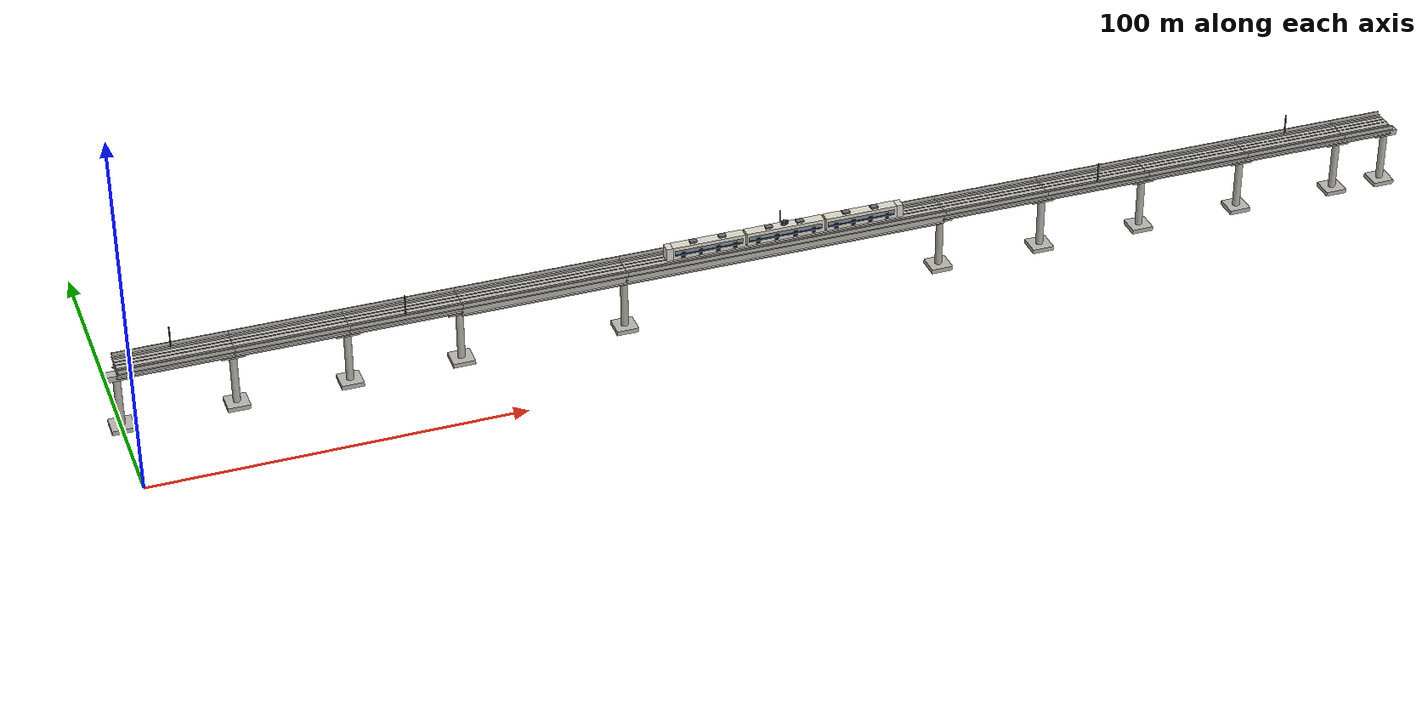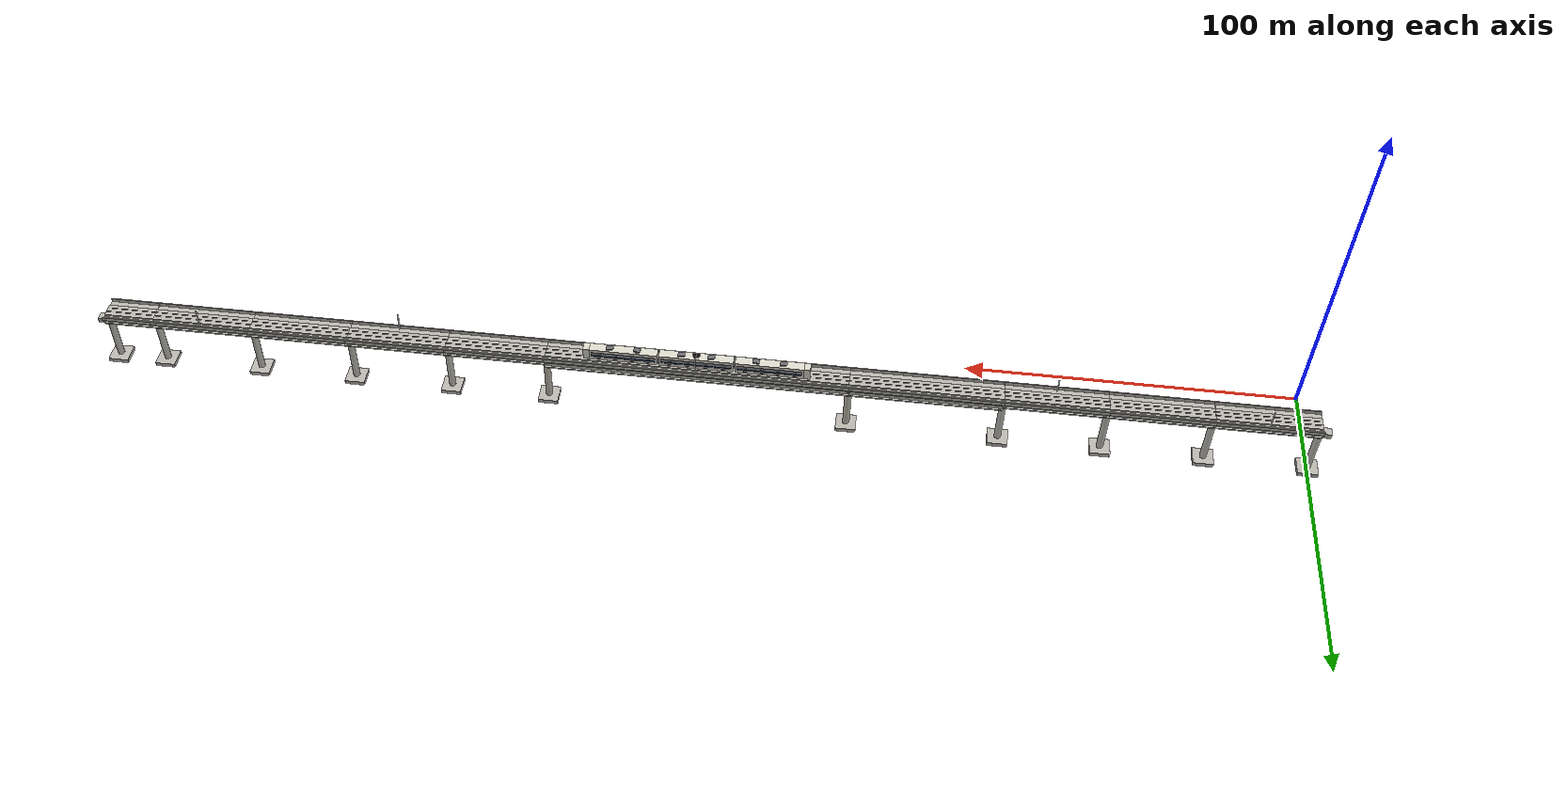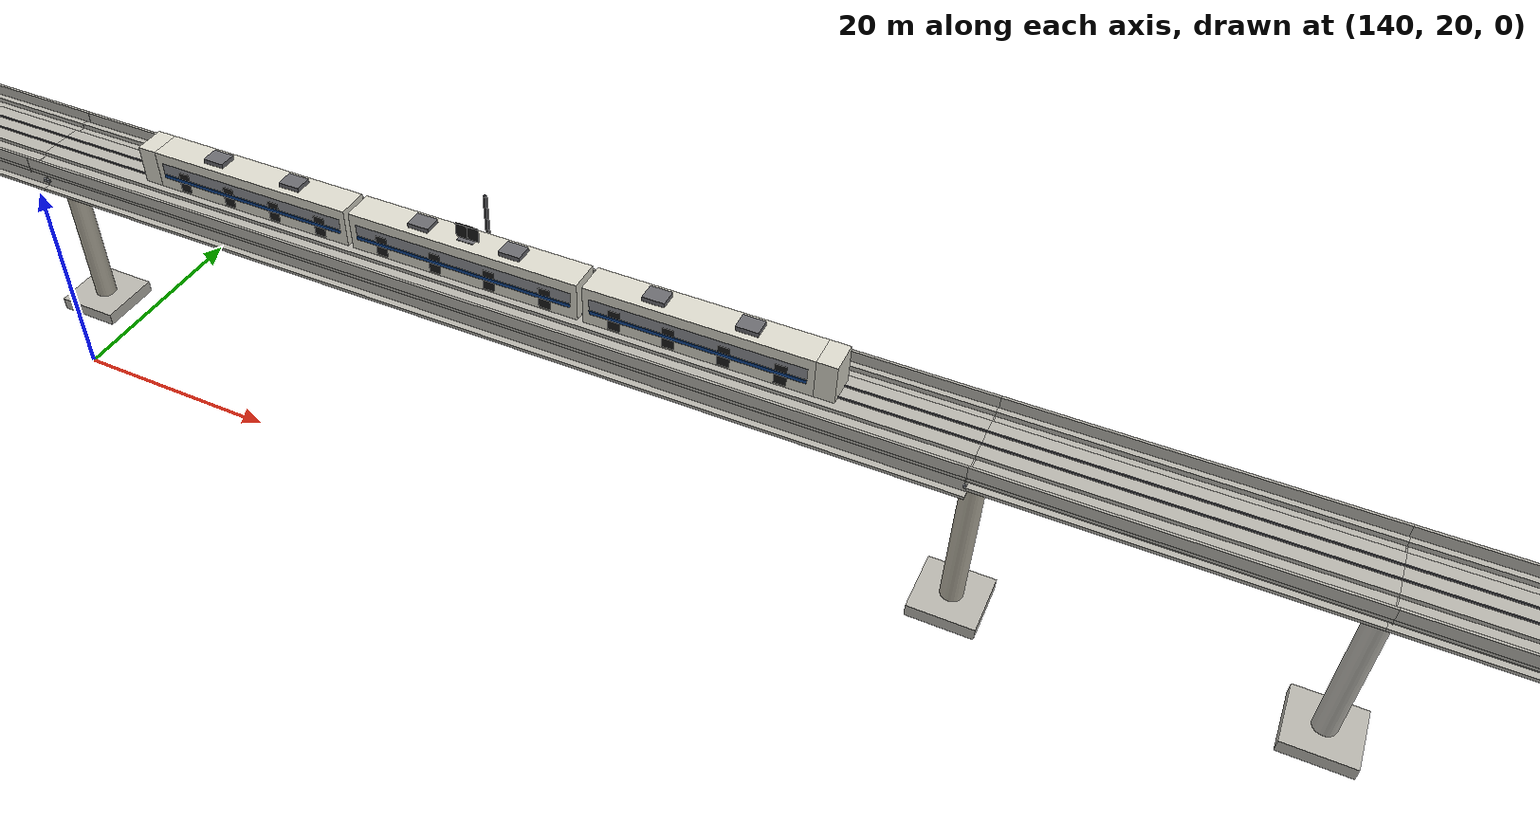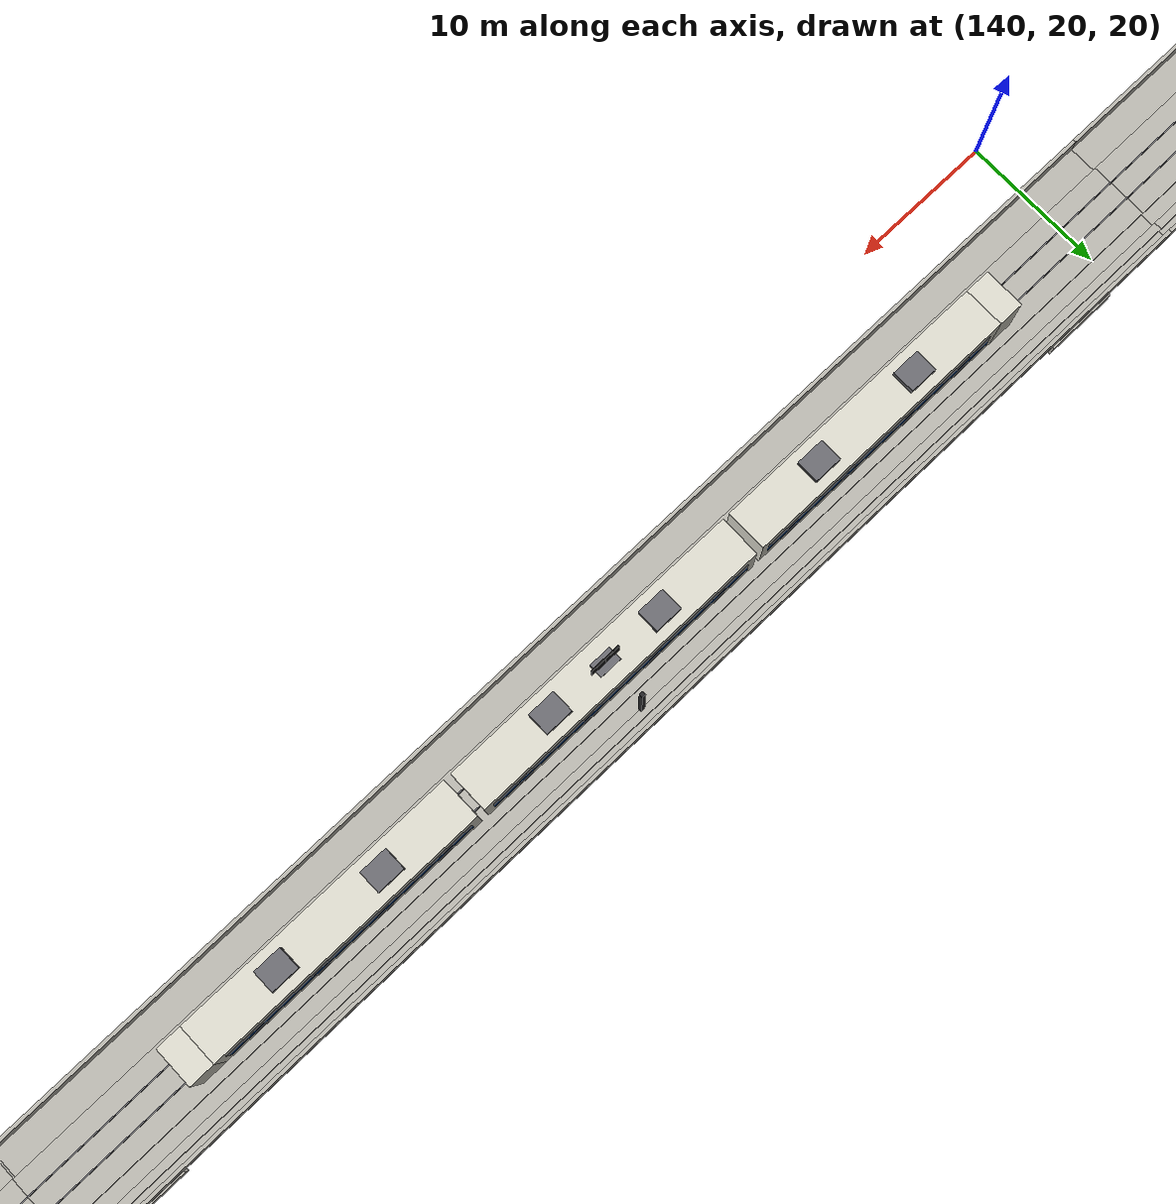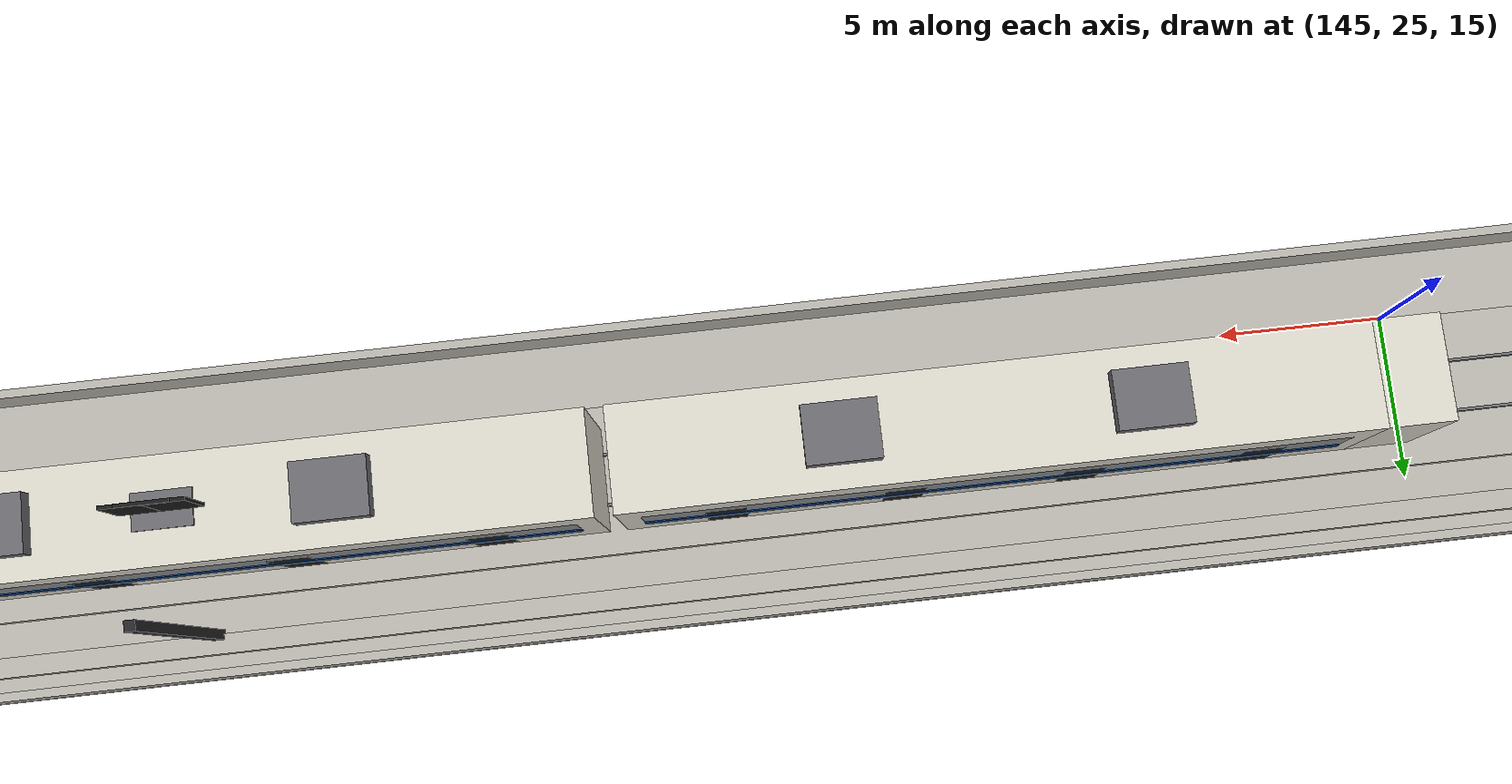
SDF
<?xml version="1.0" ?>
<sdf version="1.9">
  <model name="avian_final_metro">
    <static>true</static>
    <pose>0 0 0 0 0 0</pose>
    <link name="link">
      <collision name="MB_BEARING_001_B1_collision">
        <pose>0.000000 30.600000 16.675000 0 0 0.000000</pose>
        <geometry>
          <box>
            <size>0.700000 0.700000 0.250000</size>
          </box>
        </geometry>
      </collision>
      <visual name="MB_BEARING_001_B1_visual">
        <pose>0.000000 30.600000 16.675000 0 0 0.000000</pose>
        <geometry>
          <box>
            <size>0.700000 0.700000 0.250000</size>
          </box>
        </geometry>
        <material>
          <ambient>0.220 0.224 0.232 1</ambient>
          <diffuse>0.550 0.560 0.580 1</diffuse>
          <specular>0.1 0.1 0.1 1</specular>
        </material>
      </visual>
      <collision name="MB_BEARING_001_B2_collision">
        <pose>0.000000 25.400000 16.675000 0 0 0.000000</pose>
        <geometry>
          <box>
            <size>0.700000 0.700000 0.250000</size>
          </box>
        </geometry>
      </collision>
      <visual name="MB_BEARING_001_B2_visual">
        <pose>0.000000 25.400000 16.675000 0 0 0.000000</pose>
        <geometry>
          <box>
            <size>0.700000 0.700000 0.250000</size>
          </box>
        </geometry>
        <material>
          <ambient>0.220 0.224 0.232 1</ambient>
          <diffuse>0.550 0.560 0.580 1</diffuse>
          <specular>0.1 0.1 0.1 1</specular>
        </material>
      </visual>
      <collision name="MB_BEARING_002_B1_collision">
        <pose>30.000000 30.600000 16.675000 0 0 0.000000</pose>
        <geometry>
          <box>
            <size>0.700000 0.700000 0.250000</size>
          </box>
        </geometry>
      </collision>
      <visual name="MB_BEARING_002_B1_visual">
        <pose>30.000000 30.600000 16.675000 0 0 0.000000</pose>
        <geometry>
          <box>
            <size>0.700000 0.700000 0.250000</size>
          </box>
        </geometry>
        <material>
          <ambient>0.220 0.224 0.232 1</ambient>
          <diffuse>0.550 0.560 0.580 1</diffuse>
          <specular>0.1 0.1 0.1 1</specular>
        </material>
      </visual>
      <collision name="MB_BEARING_002_B2_collision">
        <pose>30.000000 25.400000 16.675000 0 0 0.000000</pose>
        <geometry>
          <box>
            <size>0.700000 0.700000 0.250000</size>
          </box>
        </geometry>
      </collision>
      <visual name="MB_BEARING_002_B2_visual">
        <pose>30.000000 25.400000 16.675000 0 0 0.000000</pose>
        <geometry>
          <box>
            <size>0.700000 0.700000 0.250000</size>
          </box>
        </geometry>
        <material>
          <ambient>0.220 0.224 0.232 1</ambient>
          <diffuse>0.550 0.560 0.580 1</diffuse>
          <specular>0.1 0.1 0.1 1</specular>
        </material>
      </visual>
      <collision name="MB_BEARING_003_B1_collision">
        <pose>60.000000 30.600000 16.675000 0 0 0.000000</pose>
        <geometry>
          <box>
            <size>0.700000 0.700000 0.250000</size>
          </box>
        </geometry>
      </collision>
      <visual name="MB_BEARING_003_B1_visual">
        <pose>60.000000 30.600000 16.675000 0 0 0.000000</pose>
        <geometry>
          <box>
            <size>0.700000 0.700000 0.250000</size>
          </box>
        </geometry>
        <material>
          <ambient>0.220 0.224 0.232 1</ambient>
          <diffuse>0.550 0.560 0.580 1</diffuse>
          <specular>0.1 0.1 0.1 1</specular>
        </material>
      </visual>
      <collision name="MB_BEARING_003_B2_collision">
        <pose>60.000000 25.400000 16.675000 0 0 0.000000</pose>
        <geometry>
          <box>
            <size>0.700000 0.700000 0.250000</size>
          </box>
        </geometry>
      </collision>
      <visual name="MB_BEARING_003_B2_visual">
        <pose>60.000000 25.400000 16.675000 0 0 0.000000</pose>
        <geometry>
          <box>
            <size>0.700000 0.700000 0.250000</size>
          </box>
        </geometry>
        <material>
          <ambient>0.220 0.224 0.232 1</ambient>
          <diffuse>0.550 0.560 0.580 1</diffuse>
          <specular>0.1 0.1 0.1 1</specular>
        </material>
      </visual>
      <collision name="MB_BEARING_004_B1_collision">
        <pose>90.000000 30.600000 16.675000 0 0 0.000000</pose>
        <geometry>
          <box>
            <size>0.700000 0.700000 0.250000</size>
          </box>
        </geometry>
      </collision>
      <visual name="MB_BEARING_004_B1_visual">
        <pose>90.000000 30.600000 16.675000 0 0 0.000000</pose>
        <geometry>
          <box>
            <size>0.700000 0.700000 0.250000</size>
          </box>
        </geometry>
        <material>
          <ambient>0.220 0.224 0.232 1</ambient>
          <diffuse>0.550 0.560 0.580 1</diffuse>
          <specular>0.1 0.1 0.1 1</specular>
        </material>
      </visual>
      <collision name="MB_BEARING_004_B2_collision">
        <pose>90.000000 25.400000 16.675000 0 0 0.000000</pose>
        <geometry>
          <box>
            <size>0.700000 0.700000 0.250000</size>
          </box>
        </geometry>
      </collision>
      <visual name="MB_BEARING_004_B2_visual">
        <pose>90.000000 25.400000 16.675000 0 0 0.000000</pose>
        <geometry>
          <box>
            <size>0.700000 0.700000 0.250000</size>
          </box>
        </geometry>
        <material>
          <ambient>0.220 0.224 0.232 1</ambient>
          <diffuse>0.550 0.560 0.580 1</diffuse>
          <specular>0.1 0.1 0.1 1</specular>
        </material>
      </visual>
      <collision name="MB_BEARING_005_B1_collision">
        <pose>135.000000 30.600000 16.675000 0 0 0.000000</pose>
        <geometry>
          <box>
            <size>0.700000 0.700000 0.250000</size>
          </box>
        </geometry>
      </collision>
      <visual name="MB_BEARING_005_B1_visual">
        <pose>135.000000 30.600000 16.675000 0 0 0.000000</pose>
        <geometry>
          <box>
            <size>0.700000 0.700000 0.250000</size>
          </box>
        </geometry>
        <material>
          <ambient>0.220 0.224 0.232 1</ambient>
          <diffuse>0.550 0.560 0.580 1</diffuse>
          <specular>0.1 0.1 0.1 1</specular>
        </material>
      </visual>
      <collision name="MB_BEARING_005_B2_collision">
        <pose>135.000000 25.400000 16.675000 0 0 0.000000</pose>
        <geometry>
          <box>
            <size>0.700000 0.700000 0.250000</size>
          </box>
        </geometry>
      </collision>
      <visual name="MB_BEARING_005_B2_visual">
        <pose>135.000000 25.400000 16.675000 0 0 0.000000</pose>
        <geometry>
          <box>
            <size>0.700000 0.700000 0.250000</size>
          </box>
        </geometry>
        <material>
          <ambient>0.220 0.224 0.232 1</ambient>
          <diffuse>0.550 0.560 0.580 1</diffuse>
          <specular>0.1 0.1 0.1 1</specular>
        </material>
      </visual>
      <collision name="MB_BEARING_006_B1_collision">
        <pose>225.000000 30.600000 16.675000 0 0 0.000000</pose>
        <geometry>
          <box>
            <size>0.700000 0.700000 0.250000</size>
          </box>
        </geometry>
      </collision>
      <visual name="MB_BEARING_006_B1_visual">
        <pose>225.000000 30.600000 16.675000 0 0 0.000000</pose>
        <geometry>
          <box>
            <size>0.700000 0.700000 0.250000</size>
          </box>
        </geometry>
        <material>
          <ambient>0.220 0.224 0.232 1</ambient>
          <diffuse>0.550 0.560 0.580 1</diffuse>
          <specular>0.1 0.1 0.1 1</specular>
        </material>
      </visual>
      <collision name="MB_BEARING_006_B2_collision">
        <pose>225.000000 25.400000 16.675000 0 0 0.000000</pose>
        <geometry>
          <box>
            <size>0.700000 0.700000 0.250000</size>
          </box>
        </geometry>
      </collision>
      <visual name="MB_BEARING_006_B2_visual">
        <pose>225.000000 25.400000 16.675000 0 0 0.000000</pose>
        <geometry>
          <box>
            <size>0.700000 0.700000 0.250000</size>
          </box>
        </geometry>
        <material>
          <ambient>0.220 0.224 0.232 1</ambient>
          <diffuse>0.550 0.560 0.580 1</diffuse>
          <specular>0.1 0.1 0.1 1</specular>
        </material>
      </visual>
      <collision name="MB_BEARING_007_B1_collision">
        <pose>255.000000 30.600000 16.675000 0 0 0.000000</pose>
        <geometry>
          <box>
            <size>0.700000 0.700000 0.250000</size>
          </box>
        </geometry>
      </collision>
      <visual name="MB_BEARING_007_B1_visual">
        <pose>255.000000 30.600000 16.675000 0 0 0.000000</pose>
        <geometry>
          <box>
            <size>0.700000 0.700000 0.250000</size>
          </box>
        </geometry>
        <material>
          <ambient>0.220 0.224 0.232 1</ambient>
          <diffuse>0.550 0.560 0.580 1</diffuse>
          <specular>0.1 0.1 0.1 1</specular>
        </material>
      </visual>
      <collision name="MB_BEARING_007_B2_collision">
        <pose>255.000000 25.400000 16.675000 0 0 0.000000</pose>
        <geometry>
          <box>
            <size>0.700000 0.700000 0.250000</size>
          </box>
        </geometry>
      </collision>
      <visual name="MB_BEARING_007_B2_visual">
        <pose>255.000000 25.400000 16.675000 0 0 0.000000</pose>
        <geometry>
          <box>
            <size>0.700000 0.700000 0.250000</size>
          </box>
        </geometry>
        <material>
          <ambient>0.220 0.224 0.232 1</ambient>
          <diffuse>0.550 0.560 0.580 1</diffuse>
          <specular>0.1 0.1 0.1 1</specular>
        </material>
      </visual>
      <collision name="MB_BEARING_008_B1_collision">
        <pose>285.000000 30.600000 16.675000 0 0 0.000000</pose>
        <geometry>
          <box>
            <size>0.700000 0.700000 0.250000</size>
          </box>
        </geometry>
      </collision>
      <visual name="MB_BEARING_008_B1_visual">
        <pose>285.000000 30.600000 16.675000 0 0 0.000000</pose>
        <geometry>
          <box>
            <size>0.700000 0.700000 0.250000</size>
          </box>
        </geometry>
        <material>
          <ambient>0.220 0.224 0.232 1</ambient>
          <diffuse>0.550 0.560 0.580 1</diffuse>
          <specular>0.1 0.1 0.1 1</specular>
        </material>
      </visual>
      <collision name="MB_BEARING_008_B2_collision">
        <pose>285.000000 25.400000 16.675000 0 0 0.000000</pose>
        <geometry>
          <box>
            <size>0.700000 0.700000 0.250000</size>
          </box>
        </geometry>
      </collision>
      <visual name="MB_BEARING_008_B2_visual">
        <pose>285.000000 25.400000 16.675000 0 0 0.000000</pose>
        <geometry>
          <box>
            <size>0.700000 0.700000 0.250000</size>
          </box>
        </geometry>
        <material>
          <ambient>0.220 0.224 0.232 1</ambient>
          <diffuse>0.550 0.560 0.580 1</diffuse>
          <specular>0.1 0.1 0.1 1</specular>
        </material>
      </visual>
      <collision name="MB_BEARING_009_B1_collision">
        <pose>315.000000 30.600000 16.675000 0 0 0.000000</pose>
        <geometry>
          <box>
            <size>0.700000 0.700000 0.250000</size>
          </box>
        </geometry>
      </collision>
      <visual name="MB_BEARING_009_B1_visual">
        <pose>315.000000 30.600000 16.675000 0 0 0.000000</pose>
        <geometry>
          <box>
            <size>0.700000 0.700000 0.250000</size>
          </box>
        </geometry>
        <material>
          <ambient>0.220 0.224 0.232 1</ambient>
          <diffuse>0.550 0.560 0.580 1</diffuse>
          <specular>0.1 0.1 0.1 1</specular>
        </material>
      </visual>
      <collision name="MB_BEARING_009_B2_collision">
        <pose>315.000000 25.400000 16.675000 0 0 0.000000</pose>
        <geometry>
          <box>
            <size>0.700000 0.700000 0.250000</size>
          </box>
        </geometry>
      </collision>
      <visual name="MB_BEARING_009_B2_visual">
        <pose>315.000000 25.400000 16.675000 0 0 0.000000</pose>
        <geometry>
          <box>
            <size>0.700000 0.700000 0.250000</size>
          </box>
        </geometry>
        <material>
          <ambient>0.220 0.224 0.232 1</ambient>
          <diffuse>0.550 0.560 0.580 1</diffuse>
          <specular>0.1 0.1 0.1 1</specular>
        </material>
      </visual>
      <collision name="MB_BEARING_010_B1_collision">
        <pose>345.000000 30.600000 16.675000 0 0 0.000000</pose>
        <geometry>
          <box>
            <size>0.700000 0.700000 0.250000</size>
          </box>
        </geometry>
      </collision>
      <visual name="MB_BEARING_010_B1_visual">
        <pose>345.000000 30.600000 16.675000 0 0 0.000000</pose>
        <geometry>
          <box>
            <size>0.700000 0.700000 0.250000</size>
          </box>
        </geometry>
        <material>
          <ambient>0.220 0.224 0.232 1</ambient>
          <diffuse>0.550 0.560 0.580 1</diffuse>
          <specular>0.1 0.1 0.1 1</specular>
        </material>
      </visual>
      <collision name="MB_BEARING_010_B2_collision">
        <pose>345.000000 25.400000 16.675000 0 0 0.000000</pose>
        <geometry>
          <box>
            <size>0.700000 0.700000 0.250000</size>
          </box>
        </geometry>
      </collision>
      <visual name="MB_BEARING_010_B2_visual">
        <pose>345.000000 25.400000 16.675000 0 0 0.000000</pose>
        <geometry>
          <box>
            <size>0.700000 0.700000 0.250000</size>
          </box>
        </geometry>
        <material>
          <ambient>0.220 0.224 0.232 1</ambient>
          <diffuse>0.550 0.560 0.580 1</diffuse>
          <specular>0.1 0.1 0.1 1</specular>
        </material>
      </visual>
      <collision name="MB_BEARING_011_B1_collision">
        <pose>360.000000 30.600000 16.675000 0 0 0.000000</pose>
        <geometry>
          <box>
            <size>0.700000 0.700000 0.250000</size>
          </box>
        </geometry>
      </collision>
      <visual name="MB_BEARING_011_B1_visual">
        <pose>360.000000 30.600000 16.675000 0 0 0.000000</pose>
        <geometry>
          <box>
            <size>0.700000 0.700000 0.250000</size>
          </box>
        </geometry>
        <material>
          <ambient>0.220 0.224 0.232 1</ambient>
          <diffuse>0.550 0.560 0.580 1</diffuse>
          <specular>0.1 0.1 0.1 1</specular>
        </material>
      </visual>
      <collision name="MB_BEARING_011_B2_collision">
        <pose>360.000000 25.400000 16.675000 0 0 0.000000</pose>
        <geometry>
          <box>
            <size>0.700000 0.700000 0.250000</size>
          </box>
        </geometry>
      </collision>
      <visual name="MB_BEARING_011_B2_visual">
        <pose>360.000000 25.400000 16.675000 0 0 0.000000</pose>
        <geometry>
          <box>
            <size>0.700000 0.700000 0.250000</size>
          </box>
        </geometry>
        <material>
          <ambient>0.220 0.224 0.232 1</ambient>
          <diffuse>0.550 0.560 0.580 1</diffuse>
          <specular>0.1 0.1 0.1 1</specular>
        </material>
      </visual>
      <collision name="MB_DECK_SOFFIT_001_collision">
        <pose>15.000000 28.000000 16.940000 0 0 0.000000</pose>
        <geometry>
          <box>
            <size>30.000000 6.800000 0.280000</size>
          </box>
        </geometry>
      </collision>
      <visual name="MB_DECK_SOFFIT_001_visual">
        <pose>15.000000 28.000000 16.940000 0 0 0.000000</pose>
        <geometry>
          <box>
            <size>30.000000 6.800000 0.280000</size>
          </box>
        </geometry>
        <material>
          <ambient>0.288 0.284 0.272 1</ambient>
          <diffuse>0.720 0.710 0.680 1</diffuse>
          <specular>0.1 0.1 0.1 1</specular>
        </material>
      </visual>
      <collision name="MB_DECK_SOFFIT_002_collision">
        <pose>45.000000 28.000000 16.940000 0 0 0.000000</pose>
        <geometry>
          <box>
            <size>30.000000 6.800000 0.280000</size>
          </box>
        </geometry>
      </collision>
      <visual name="MB_DECK_SOFFIT_002_visual">
        <pose>45.000000 28.000000 16.940000 0 0 0.000000</pose>
        <geometry>
          <box>
            <size>30.000000 6.800000 0.280000</size>
          </box>
        </geometry>
        <material>
          <ambient>0.288 0.284 0.272 1</ambient>
          <diffuse>0.720 0.710 0.680 1</diffuse>
          <specular>0.1 0.1 0.1 1</specular>
        </material>
      </visual>
      <collision name="MB_DECK_SOFFIT_003_collision">
        <pose>75.000000 28.000000 16.940000 0 0 0.000000</pose>
        <geometry>
          <box>
            <size>30.000000 6.800000 0.280000</size>
          </box>
        </geometry>
      </collision>
      <visual name="MB_DECK_SOFFIT_003_visual">
        <pose>75.000000 28.000000 16.940000 0 0 0.000000</pose>
        <geometry>
          <box>
            <size>30.000000 6.800000 0.280000</size>
          </box>
        </geometry>
        <material>
          <ambient>0.288 0.284 0.272 1</ambient>
          <diffuse>0.720 0.710 0.680 1</diffuse>
          <specular>0.1 0.1 0.1 1</specular>
        </material>
      </visual>
      <collision name="MB_DECK_SOFFIT_004_collision">
        <pose>112.500000 28.000000 15.940000 0 0 0.000000</pose>
        <geometry>
          <box>
            <size>45.000000 6.800000 0.280000</size>
          </box>
        </geometry>
      </collision>
      <visual name="MB_DECK_SOFFIT_004_visual">
        <pose>112.500000 28.000000 15.940000 0 0 0.000000</pose>
        <geometry>
          <box>
            <size>45.000000 6.800000 0.280000</size>
          </box>
        </geometry>
        <material>
          <ambient>0.288 0.284 0.272 1</ambient>
          <diffuse>0.720 0.710 0.680 1</diffuse>
          <specular>0.1 0.1 0.1 1</specular>
        </material>
      </visual>
      <collision name="MB_DECK_SOFFIT_005_collision">
        <pose>180.000000 28.000000 15.940000 0 0 0.000000</pose>
        <geometry>
          <box>
            <size>90.000000 6.800000 0.280000</size>
          </box>
        </geometry>
      </collision>
      <visual name="MB_DECK_SOFFIT_005_visual">
        <pose>180.000000 28.000000 15.940000 0 0 0.000000</pose>
        <geometry>
          <box>
            <size>90.000000 6.800000 0.280000</size>
          </box>
        </geometry>
        <material>
          <ambient>0.288 0.284 0.272 1</ambient>
          <diffuse>0.720 0.710 0.680 1</diffuse>
          <specular>0.1 0.1 0.1 1</specular>
        </material>
      </visual>
      <collision name="MB_DECK_SOFFIT_006_collision">
        <pose>240.000000 28.000000 16.940000 0 0 0.000000</pose>
        <geometry>
          <box>
            <size>30.000000 6.800000 0.280000</size>
          </box>
        </geometry>
      </collision>
      <visual name="MB_DECK_SOFFIT_006_visual">
        <pose>240.000000 28.000000 16.940000 0 0 0.000000</pose>
        <geometry>
          <box>
            <size>30.000000 6.800000 0.280000</size>
          </box>
        </geometry>
        <material>
          <ambient>0.288 0.284 0.272 1</ambient>
          <diffuse>0.720 0.710 0.680 1</diffuse>
          <specular>0.1 0.1 0.1 1</specular>
        </material>
      </visual>
      <collision name="MB_DECK_SOFFIT_007_collision">
        <pose>270.000000 28.000000 16.940000 0 0 0.000000</pose>
        <geometry>
          <box>
            <size>30.000000 6.800000 0.280000</size>
          </box>
        </geometry>
      </collision>
      <visual name="MB_DECK_SOFFIT_007_visual">
        <pose>270.000000 28.000000 16.940000 0 0 0.000000</pose>
        <geometry>
          <box>
            <size>30.000000 6.800000 0.280000</size>
          </box>
        </geometry>
        <material>
          <ambient>0.288 0.284 0.272 1</ambient>
          <diffuse>0.720 0.710 0.680 1</diffuse>
          <specular>0.1 0.1 0.1 1</specular>
        </material>
      </visual>
      <collision name="MB_DECK_SOFFIT_008_collision">
        <pose>300.000000 28.000000 16.940000 0 0 0.000000</pose>
        <geometry>
          <box>
            <size>30.000000 6.800000 0.280000</size>
          </box>
        </geometry>
      </collision>
      <visual name="MB_DECK_SOFFIT_008_visual">
        <pose>300.000000 28.000000 16.940000 0 0 0.000000</pose>
        <geometry>
          <box>
            <size>30.000000 6.800000 0.280000</size>
          </box>
        </geometry>
        <material>
          <ambient>0.288 0.284 0.272 1</ambient>
          <diffuse>0.720 0.710 0.680 1</diffuse>
          <specular>0.1 0.1 0.1 1</specular>
        </material>
      </visual>
      <collision name="MB_DECK_SOFFIT_009_collision">
        <pose>330.000000 28.000000 16.940000 0 0 0.000000</pose>
        <geometry>
          <box>
            <size>30.000000 6.800000 0.280000</size>
          </box>
        </geometry>
      </collision>
      <visual name="MB_DECK_SOFFIT_009_visual">
        <pose>330.000000 28.000000 16.940000 0 0 0.000000</pose>
        <geometry>
          <box>
            <size>30.000000 6.800000 0.280000</size>
          </box>
        </geometry>
        <material>
          <ambient>0.288 0.284 0.272 1</ambient>
          <diffuse>0.720 0.710 0.680 1</diffuse>
          <specular>0.1 0.1 0.1 1</specular>
        </material>
      </visual>
      <collision name="MB_DECK_SOFFIT_010_collision">
        <pose>352.500000 28.000000 16.940000 0 0 0.000000</pose>
        <geometry>
          <box>
            <size>15.000000 6.800000 0.280000</size>
          </box>
        </geometry>
      </collision>
      <visual name="MB_DECK_SOFFIT_010_visual">
        <pose>352.500000 28.000000 16.940000 0 0 0.000000</pose>
        <geometry>
          <box>
            <size>15.000000 6.800000 0.280000</size>
          </box>
        </geometry>
        <material>
          <ambient>0.288 0.284 0.272 1</ambient>
          <diffuse>0.720 0.710 0.680 1</diffuse>
          <specular>0.1 0.1 0.1 1</specular>
        </material>
      </visual>
      <collision name="MB_DECK_TOP_001_collision">
        <pose>15.000000 28.000000 18.850000 0 0 0.000000</pose>
        <geometry>
          <box>
            <size>30.000000 8.600000 0.300000</size>
          </box>
        </geometry>
      </collision>
      <visual name="MB_DECK_TOP_001_visual">
        <pose>15.000000 28.000000 18.850000 0 0 0.000000</pose>
        <geometry>
          <box>
            <size>30.000000 8.600000 0.300000</size>
          </box>
        </geometry>
        <material>
          <ambient>0.288 0.284 0.272 1</ambient>
          <diffuse>0.720 0.710 0.680 1</diffuse>
          <specular>0.1 0.1 0.1 1</specular>
        </material>
      </visual>
      <collision name="MB_DECK_TOP_002_collision">
        <pose>45.000000 28.000000 18.850000 0 0 0.000000</pose>
        <geometry>
          <box>
            <size>30.000000 8.600000 0.300000</size>
          </box>
        </geometry>
      </collision>
      <visual name="MB_DECK_TOP_002_visual">
        <pose>45.000000 28.000000 18.850000 0 0 0.000000</pose>
        <geometry>
          <box>
            <size>30.000000 8.600000 0.300000</size>
          </box>
        </geometry>
        <material>
          <ambient>0.288 0.284 0.272 1</ambient>
          <diffuse>0.720 0.710 0.680 1</diffuse>
          <specular>0.1 0.1 0.1 1</specular>
        </material>
      </visual>
      <collision name="MB_DECK_TOP_003_collision">
        <pose>75.000000 28.000000 18.850000 0 0 0.000000</pose>
        <geometry>
          <box>
            <size>30.000000 8.600000 0.300000</size>
          </box>
        </geometry>
      </collision>
      <visual name="MB_DECK_TOP_003_visual">
        <pose>75.000000 28.000000 18.850000 0 0 0.000000</pose>
        <geometry>
          <box>
            <size>30.000000 8.600000 0.300000</size>
          </box>
        </geometry>
        <material>
          <ambient>0.288 0.284 0.272 1</ambient>
          <diffuse>0.720 0.710 0.680 1</diffuse>
          <specular>0.1 0.1 0.1 1</specular>
        </material>
      </visual>
      <collision name="MB_DECK_TOP_004_collision">
        <pose>112.500000 28.000000 18.850000 0 0 0.000000</pose>
        <geometry>
          <box>
            <size>45.000000 8.600000 0.300000</size>
          </box>
        </geometry>
      </collision>
      <visual name="MB_DECK_TOP_004_visual">
        <pose>112.500000 28.000000 18.850000 0 0 0.000000</pose>
        <geometry>
          <box>
            <size>45.000000 8.600000 0.300000</size>
          </box>
        </geometry>
        <material>
          <ambient>0.288 0.284 0.272 1</ambient>
          <diffuse>0.720 0.710 0.680 1</diffuse>
          <specular>0.1 0.1 0.1 1</specular>
        </material>
      </visual>
      <collision name="MB_DECK_TOP_005_collision">
        <pose>180.000000 28.000000 18.850000 0 0 0.000000</pose>
        <geometry>
          <box>
            <size>90.000000 8.600000 0.300000</size>
          </box>
        </geometry>
      </collision>
      <visual name="MB_DECK_TOP_005_visual">
        <pose>180.000000 28.000000 18.850000 0 0 0.000000</pose>
        <geometry>
          <box>
            <size>90.000000 8.600000 0.300000</size>
          </box>
        </geometry>
        <material>
          <ambient>0.288 0.284 0.272 1</ambient>
          <diffuse>0.720 0.710 0.680 1</diffuse>
          <specular>0.1 0.1 0.1 1</specular>
        </material>
      </visual>
      <collision name="MB_DECK_TOP_006_collision">
        <pose>240.000000 28.000000 18.850000 0 0 0.000000</pose>
        <geometry>
          <box>
            <size>30.000000 8.600000 0.300000</size>
          </box>
        </geometry>
      </collision>
      <visual name="MB_DECK_TOP_006_visual">
        <pose>240.000000 28.000000 18.850000 0 0 0.000000</pose>
        <geometry>
          <box>
            <size>30.000000 8.600000 0.300000</size>
          </box>
        </geometry>
        <material>
          <ambient>0.288 0.284 0.272 1</ambient>
          <diffuse>0.720 0.710 0.680 1</diffuse>
          <specular>0.1 0.1 0.1 1</specular>
        </material>
      </visual>
      <collision name="MB_DECK_TOP_007_collision">
        <pose>270.000000 28.000000 18.850000 0 0 0.000000</pose>
        <geometry>
          <box>
            <size>30.000000 8.600000 0.300000</size>
          </box>
        </geometry>
      </collision>
      <visual name="MB_DECK_TOP_007_visual">
        <pose>270.000000 28.000000 18.850000 0 0 0.000000</pose>
        <geometry>
          <box>
            <size>30.000000 8.600000 0.300000</size>
          </box>
        </geometry>
        <material>
          <ambient>0.288 0.284 0.272 1</ambient>
          <diffuse>0.720 0.710 0.680 1</diffuse>
          <specular>0.1 0.1 0.1 1</specular>
        </material>
      </visual>
      <collision name="MB_DECK_TOP_008_collision">
        <pose>300.000000 28.000000 18.850000 0 0 0.000000</pose>
        <geometry>
          <box>
            <size>30.000000 8.600000 0.300000</size>
          </box>
        </geometry>
      </collision>
      <visual name="MB_DECK_TOP_008_visual">
        <pose>300.000000 28.000000 18.850000 0 0 0.000000</pose>
        <geometry>
          <box>
            <size>30.000000 8.600000 0.300000</size>
          </box>
        </geometry>
        <material>
          <ambient>0.288 0.284 0.272 1</ambient>
          <diffuse>0.720 0.710 0.680 1</diffuse>
          <specular>0.1 0.1 0.1 1</specular>
        </material>
      </visual>
      <collision name="MB_DECK_TOP_009_collision">
        <pose>330.000000 28.000000 18.850000 0 0 0.000000</pose>
        <geometry>
          <box>
            <size>30.000000 8.600000 0.300000</size>
          </box>
        </geometry>
      </collision>
      <visual name="MB_DECK_TOP_009_visual">
        <pose>330.000000 28.000000 18.850000 0 0 0.000000</pose>
        <geometry>
          <box>
            <size>30.000000 8.600000 0.300000</size>
          </box>
        </geometry>
        <material>
          <ambient>0.288 0.284 0.272 1</ambient>
          <diffuse>0.720 0.710 0.680 1</diffuse>
          <specular>0.1 0.1 0.1 1</specular>
        </material>
      </visual>
      <collision name="MB_DECK_TOP_010_collision">
        <pose>352.500000 28.000000 18.850000 0 0 0.000000</pose>
        <geometry>
          <box>
            <size>15.000000 8.600000 0.300000</size>
          </box>
        </geometry>
      </collision>
      <visual name="MB_DECK_TOP_010_visual">
        <pose>352.500000 28.000000 18.850000 0 0 0.000000</pose>
        <geometry>
          <box>
            <size>15.000000 8.600000 0.300000</size>
          </box>
        </geometry>
        <material>
          <ambient>0.288 0.284 0.272 1</ambient>
          <diffuse>0.720 0.710 0.680 1</diffuse>
          <specular>0.1 0.1 0.1 1</specular>
        </material>
      </visual>
      <collision name="MB_HATCH_001_collision">
        <pose>15.000000 28.000000 16.840000 0 0 0.000000</pose>
        <geometry>
          <box>
            <size>0.900000 0.700000 0.080000</size>
          </box>
        </geometry>
      </collision>
      <visual name="MB_HATCH_001_visual">
        <pose>15.000000 28.000000 16.840000 0 0 0.000000</pose>
        <geometry>
          <box>
            <size>0.900000 0.700000 0.080000</size>
          </box>
        </geometry>
        <material>
          <ambient>0.060 0.060 0.064 1</ambient>
          <diffuse>0.150 0.150 0.160 1</diffuse>
          <specular>0.1 0.1 0.1 1</specular>
        </material>
      </visual>
      <collision name="MB_HATCH_002_collision">
        <pose>45.000000 28.000000 16.840000 0 0 0.000000</pose>
        <geometry>
          <box>
            <size>0.900000 0.700000 0.080000</size>
          </box>
        </geometry>
      </collision>
      <visual name="MB_HATCH_002_visual">
        <pose>45.000000 28.000000 16.840000 0 0 0.000000</pose>
        <geometry>
          <box>
            <size>0.900000 0.700000 0.080000</size>
          </box>
        </geometry>
        <material>
          <ambient>0.060 0.060 0.064 1</ambient>
          <diffuse>0.150 0.150 0.160 1</diffuse>
          <specular>0.1 0.1 0.1 1</specular>
        </material>
      </visual>
      <collision name="MB_HATCH_003_collision">
        <pose>75.000000 28.000000 16.840000 0 0 0.000000</pose>
        <geometry>
          <box>
            <size>0.900000 0.700000 0.080000</size>
          </box>
        </geometry>
      </collision>
      <visual name="MB_HATCH_003_visual">
        <pose>75.000000 28.000000 16.840000 0 0 0.000000</pose>
        <geometry>
          <box>
            <size>0.900000 0.700000 0.080000</size>
          </box>
        </geometry>
        <material>
          <ambient>0.060 0.060 0.064 1</ambient>
          <diffuse>0.150 0.150 0.160 1</diffuse>
          <specular>0.1 0.1 0.1 1</specular>
        </material>
      </visual>
      <collision name="MB_HATCH_004_collision">
        <pose>112.500000 28.000000 15.840000 0 0 0.000000</pose>
        <geometry>
          <box>
            <size>0.900000 0.700000 0.080000</size>
          </box>
        </geometry>
      </collision>
      <visual name="MB_HATCH_004_visual">
        <pose>112.500000 28.000000 15.840000 0 0 0.000000</pose>
        <geometry>
          <box>
            <size>0.900000 0.700000 0.080000</size>
          </box>
        </geometry>
        <material>
          <ambient>0.060 0.060 0.064 1</ambient>
          <diffuse>0.150 0.150 0.160 1</diffuse>
          <specular>0.1 0.1 0.1 1</specular>
        </material>
      </visual>
      <collision name="MB_HATCH_005_collision">
        <pose>180.000000 28.000000 15.840000 0 0 0.000000</pose>
        <geometry>
          <box>
            <size>0.900000 0.700000 0.080000</size>
          </box>
        </geometry>
      </collision>
      <visual name="MB_HATCH_005_visual">
        <pose>180.000000 28.000000 15.840000 0 0 0.000000</pose>
        <geometry>
          <box>
            <size>0.900000 0.700000 0.080000</size>
          </box>
        </geometry>
        <material>
          <ambient>0.060 0.060 0.064 1</ambient>
          <diffuse>0.150 0.150 0.160 1</diffuse>
          <specular>0.1 0.1 0.1 1</specular>
        </material>
      </visual>
      <collision name="MB_HATCH_006_collision">
        <pose>240.000000 28.000000 16.840000 0 0 0.000000</pose>
        <geometry>
          <box>
            <size>0.900000 0.700000 0.080000</size>
          </box>
        </geometry>
      </collision>
      <visual name="MB_HATCH_006_visual">
        <pose>240.000000 28.000000 16.840000 0 0 0.000000</pose>
        <geometry>
          <box>
            <size>0.900000 0.700000 0.080000</size>
          </box>
        </geometry>
        <material>
          <ambient>0.060 0.060 0.064 1</ambient>
          <diffuse>0.150 0.150 0.160 1</diffuse>
          <specular>0.1 0.1 0.1 1</specular>
        </material>
      </visual>
      <collision name="MB_HATCH_007_collision">
        <pose>270.000000 28.000000 16.840000 0 0 0.000000</pose>
        <geometry>
          <box>
            <size>0.900000 0.700000 0.080000</size>
          </box>
        </geometry>
      </collision>
      <visual name="MB_HATCH_007_visual">
        <pose>270.000000 28.000000 16.840000 0 0 0.000000</pose>
        <geometry>
          <box>
            <size>0.900000 0.700000 0.080000</size>
          </box>
        </geometry>
        <material>
          <ambient>0.060 0.060 0.064 1</ambient>
          <diffuse>0.150 0.150 0.160 1</diffuse>
          <specular>0.1 0.1 0.1 1</specular>
        </material>
      </visual>
      <collision name="MB_HATCH_008_collision">
        <pose>300.000000 28.000000 16.840000 0 0 0.000000</pose>
        <geometry>
          <box>
            <size>0.900000 0.700000 0.080000</size>
          </box>
        </geometry>
      </collision>
      <visual name="MB_HATCH_008_visual">
        <pose>300.000000 28.000000 16.840000 0 0 0.000000</pose>
        <geometry>
          <box>
            <size>0.900000 0.700000 0.080000</size>
          </box>
        </geometry>
        <material>
          <ambient>0.060 0.060 0.064 1</ambient>
          <diffuse>0.150 0.150 0.160 1</diffuse>
          <specular>0.1 0.1 0.1 1</specular>
        </material>
      </visual>
      <collision name="MB_HATCH_009_collision">
        <pose>330.000000 28.000000 16.840000 0 0 0.000000</pose>
        <geometry>
          <box>
            <size>0.900000 0.700000 0.080000</size>
          </box>
        </geometry>
      </collision>
      <visual name="MB_HATCH_009_visual">
        <pose>330.000000 28.000000 16.840000 0 0 0.000000</pose>
        <geometry>
          <box>
            <size>0.900000 0.700000 0.080000</size>
          </box>
        </geometry>
        <material>
          <ambient>0.060 0.060 0.064 1</ambient>
          <diffuse>0.150 0.150 0.160 1</diffuse>
          <specular>0.1 0.1 0.1 1</specular>
        </material>
      </visual>
      <collision name="MB_HATCH_010_collision">
        <pose>352.500000 28.000000 16.840000 0 0 0.000000</pose>
        <geometry>
          <box>
            <size>0.900000 0.700000 0.080000</size>
          </box>
        </geometry>
      </collision>
      <visual name="MB_HATCH_010_visual">
        <pose>352.500000 28.000000 16.840000 0 0 0.000000</pose>
        <geometry>
          <box>
            <size>0.900000 0.700000 0.080000</size>
          </box>
        </geometry>
        <material>
          <ambient>0.060 0.060 0.064 1</ambient>
          <diffuse>0.150 0.150 0.160 1</diffuse>
          <specular>0.1 0.1 0.1 1</specular>
        </material>
      </visual>
      <collision name="MB_JOINT_001_collision">
        <pose>0.000000 28.000000 18.775000 0 0 0.000000</pose>
        <geometry>
          <box>
            <size>0.120000 8.600000 0.450000</size>
          </box>
        </geometry>
      </collision>
      <visual name="MB_JOINT_001_visual">
        <pose>0.000000 28.000000 18.775000 0 0 0.000000</pose>
        <geometry>
          <box>
            <size>0.120000 8.600000 0.450000</size>
          </box>
        </geometry>
        <material>
          <ambient>0.288 0.284 0.272 1</ambient>
          <diffuse>0.720 0.710 0.680 1</diffuse>
          <specular>0.1 0.1 0.1 1</specular>
        </material>
      </visual>
      <collision name="MB_JOINT_002_collision">
        <pose>30.000000 28.000000 18.775000 0 0 0.000000</pose>
        <geometry>
          <box>
            <size>0.120000 8.600000 0.450000</size>
          </box>
        </geometry>
      </collision>
      <visual name="MB_JOINT_002_visual">
        <pose>30.000000 28.000000 18.775000 0 0 0.000000</pose>
        <geometry>
          <box>
            <size>0.120000 8.600000 0.450000</size>
          </box>
        </geometry>
        <material>
          <ambient>0.288 0.284 0.272 1</ambient>
          <diffuse>0.720 0.710 0.680 1</diffuse>
          <specular>0.1 0.1 0.1 1</specular>
        </material>
      </visual>
      <collision name="MB_JOINT_003_collision">
        <pose>60.000000 28.000000 18.775000 0 0 0.000000</pose>
        <geometry>
          <box>
            <size>0.120000 8.600000 0.450000</size>
          </box>
        </geometry>
      </collision>
      <visual name="MB_JOINT_003_visual">
        <pose>60.000000 28.000000 18.775000 0 0 0.000000</pose>
        <geometry>
          <box>
            <size>0.120000 8.600000 0.450000</size>
          </box>
        </geometry>
        <material>
          <ambient>0.288 0.284 0.272 1</ambient>
          <diffuse>0.720 0.710 0.680 1</diffuse>
          <specular>0.1 0.1 0.1 1</specular>
        </material>
      </visual>
      <collision name="MB_JOINT_004_collision">
        <pose>90.000000 28.000000 18.775000 0 0 0.000000</pose>
        <geometry>
          <box>
            <size>0.120000 8.600000 0.450000</size>
          </box>
        </geometry>
      </collision>
      <visual name="MB_JOINT_004_visual">
        <pose>90.000000 28.000000 18.775000 0 0 0.000000</pose>
        <geometry>
          <box>
            <size>0.120000 8.600000 0.450000</size>
          </box>
        </geometry>
        <material>
          <ambient>0.288 0.284 0.272 1</ambient>
          <diffuse>0.720 0.710 0.680 1</diffuse>
          <specular>0.1 0.1 0.1 1</specular>
        </material>
      </visual>
      <collision name="MB_JOINT_005_collision">
        <pose>135.000000 28.000000 18.775000 0 0 0.000000</pose>
        <geometry>
          <box>
            <size>0.120000 8.600000 0.450000</size>
          </box>
        </geometry>
      </collision>
      <visual name="MB_JOINT_005_visual">
        <pose>135.000000 28.000000 18.775000 0 0 0.000000</pose>
        <geometry>
          <box>
            <size>0.120000 8.600000 0.450000</size>
          </box>
        </geometry>
        <material>
          <ambient>0.288 0.284 0.272 1</ambient>
          <diffuse>0.720 0.710 0.680 1</diffuse>
          <specular>0.1 0.1 0.1 1</specular>
        </material>
      </visual>
      <collision name="MB_JOINT_006_collision">
        <pose>225.000000 28.000000 18.775000 0 0 0.000000</pose>
        <geometry>
          <box>
            <size>0.120000 8.600000 0.450000</size>
          </box>
        </geometry>
      </collision>
      <visual name="MB_JOINT_006_visual">
        <pose>225.000000 28.000000 18.775000 0 0 0.000000</pose>
        <geometry>
          <box>
            <size>0.120000 8.600000 0.450000</size>
          </box>
        </geometry>
        <material>
          <ambient>0.288 0.284 0.272 1</ambient>
          <diffuse>0.720 0.710 0.680 1</diffuse>
          <specular>0.1 0.1 0.1 1</specular>
        </material>
      </visual>
      <collision name="MB_JOINT_007_collision">
        <pose>255.000000 28.000000 18.775000 0 0 0.000000</pose>
        <geometry>
          <box>
            <size>0.120000 8.600000 0.450000</size>
          </box>
        </geometry>
      </collision>
      <visual name="MB_JOINT_007_visual">
        <pose>255.000000 28.000000 18.775000 0 0 0.000000</pose>
        <geometry>
          <box>
            <size>0.120000 8.600000 0.450000</size>
          </box>
        </geometry>
        <material>
          <ambient>0.288 0.284 0.272 1</ambient>
          <diffuse>0.720 0.710 0.680 1</diffuse>
          <specular>0.1 0.1 0.1 1</specular>
        </material>
      </visual>
      <collision name="MB_JOINT_008_collision">
        <pose>285.000000 28.000000 18.775000 0 0 0.000000</pose>
        <geometry>
          <box>
            <size>0.120000 8.600000 0.450000</size>
          </box>
        </geometry>
      </collision>
      <visual name="MB_JOINT_008_visual">
        <pose>285.000000 28.000000 18.775000 0 0 0.000000</pose>
        <geometry>
          <box>
            <size>0.120000 8.600000 0.450000</size>
          </box>
        </geometry>
        <material>
          <ambient>0.288 0.284 0.272 1</ambient>
          <diffuse>0.720 0.710 0.680 1</diffuse>
          <specular>0.1 0.1 0.1 1</specular>
        </material>
      </visual>
      <collision name="MB_JOINT_009_collision">
        <pose>315.000000 28.000000 18.775000 0 0 0.000000</pose>
        <geometry>
          <box>
            <size>0.120000 8.600000 0.450000</size>
          </box>
        </geometry>
      </collision>
      <visual name="MB_JOINT_009_visual">
        <pose>315.000000 28.000000 18.775000 0 0 0.000000</pose>
        <geometry>
          <box>
            <size>0.120000 8.600000 0.450000</size>
          </box>
        </geometry>
        <material>
          <ambient>0.288 0.284 0.272 1</ambient>
          <diffuse>0.720 0.710 0.680 1</diffuse>
          <specular>0.1 0.1 0.1 1</specular>
        </material>
      </visual>
      <collision name="MB_JOINT_010_collision">
        <pose>345.000000 28.000000 18.775000 0 0 0.000000</pose>
        <geometry>
          <box>
            <size>0.120000 8.600000 0.450000</size>
          </box>
        </geometry>
      </collision>
      <visual name="MB_JOINT_010_visual">
        <pose>345.000000 28.000000 18.775000 0 0 0.000000</pose>
        <geometry>
          <box>
            <size>0.120000 8.600000 0.450000</size>
          </box>
        </geometry>
        <material>
          <ambient>0.288 0.284 0.272 1</ambient>
          <diffuse>0.720 0.710 0.680 1</diffuse>
          <specular>0.1 0.1 0.1 1</specular>
        </material>
      </visual>
      <collision name="MB_MAST_001_collision">
        <pose>15.000000 31.100000 22.350000 0 0 0.000000</pose>
        <geometry>
          <box>
            <size>0.280000 0.280000 6.000000</size>
          </box>
        </geometry>
      </collision>
      <visual name="MB_MAST_001_visual">
        <pose>15.000000 31.100000 22.350000 0 0 0.000000</pose>
        <geometry>
          <box>
            <size>0.280000 0.280000 6.000000</size>
          </box>
        </geometry>
        <material>
          <ambient>0.060 0.060 0.064 1</ambient>
          <diffuse>0.150 0.150 0.160 1</diffuse>
          <specular>0.1 0.1 0.1 1</specular>
        </material>
      </visual>
      <collision name="MB_MAST_002_collision">
        <pose>75.000000 24.900000 22.350000 0 0 0.000000</pose>
        <geometry>
          <box>
            <size>0.280000 0.280000 6.000000</size>
          </box>
        </geometry>
      </collision>
      <visual name="MB_MAST_002_visual">
        <pose>75.000000 24.900000 22.350000 0 0 0.000000</pose>
        <geometry>
          <box>
            <size>0.280000 0.280000 6.000000</size>
          </box>
        </geometry>
        <material>
          <ambient>0.060 0.060 0.064 1</ambient>
          <diffuse>0.150 0.150 0.160 1</diffuse>
          <specular>0.1 0.1 0.1 1</specular>
        </material>
      </visual>
      <collision name="MB_MAST_003_collision">
        <pose>180.000000 31.100000 22.350000 0 0 0.000000</pose>
        <geometry>
          <box>
            <size>0.280000 0.280000 6.000000</size>
          </box>
        </geometry>
      </collision>
      <visual name="MB_MAST_003_visual">
        <pose>180.000000 31.100000 22.350000 0 0 0.000000</pose>
        <geometry>
          <box>
            <size>0.280000 0.280000 6.000000</size>
          </box>
        </geometry>
        <material>
          <ambient>0.060 0.060 0.064 1</ambient>
          <diffuse>0.150 0.150 0.160 1</diffuse>
          <specular>0.1 0.1 0.1 1</specular>
        </material>
      </visual>
      <collision name="MB_MAST_004_collision">
        <pose>270.000000 24.900000 22.350000 0 0 0.000000</pose>
        <geometry>
          <box>
            <size>0.280000 0.280000 6.000000</size>
          </box>
        </geometry>
      </collision>
      <visual name="MB_MAST_004_visual">
        <pose>270.000000 24.900000 22.350000 0 0 0.000000</pose>
        <geometry>
          <box>
            <size>0.280000 0.280000 6.000000</size>
          </box>
        </geometry>
        <material>
          <ambient>0.060 0.060 0.064 1</ambient>
          <diffuse>0.150 0.150 0.160 1</diffuse>
          <specular>0.1 0.1 0.1 1</specular>
        </material>
      </visual>
      <collision name="MB_MAST_005_collision">
        <pose>330.000000 31.100000 22.350000 0 0 0.000000</pose>
        <geometry>
          <box>
            <size>0.280000 0.280000 6.000000</size>
          </box>
        </geometry>
      </collision>
      <visual name="MB_MAST_005_visual">
        <pose>330.000000 31.100000 22.350000 0 0 0.000000</pose>
        <geometry>
          <box>
            <size>0.280000 0.280000 6.000000</size>
          </box>
        </geometry>
        <material>
          <ambient>0.060 0.060 0.064 1</ambient>
          <diffuse>0.150 0.150 0.160 1</diffuse>
          <specular>0.1 0.1 0.1 1</specular>
        </material>
      </visual>
      <collision name="MB_PARAPET_001_N_collision">
        <pose>15.000000 32.180000 19.550000 0 0 0.000000</pose>
        <geometry>
          <box>
            <size>30.000000 0.240000 1.100000</size>
          </box>
        </geometry>
      </collision>
      <visual name="MB_PARAPET_001_N_visual">
        <pose>15.000000 32.180000 19.550000 0 0 0.000000</pose>
        <geometry>
          <box>
            <size>30.000000 0.240000 1.100000</size>
          </box>
        </geometry>
        <material>
          <ambient>0.288 0.284 0.272 1</ambient>
          <diffuse>0.720 0.710 0.680 1</diffuse>
          <specular>0.1 0.1 0.1 1</specular>
        </material>
      </visual>
      <collision name="MB_PARAPET_001_S_collision">
        <pose>15.000000 23.820000 19.550000 0 0 0.000000</pose>
        <geometry>
          <box>
            <size>30.000000 0.240000 1.100000</size>
          </box>
        </geometry>
      </collision>
      <visual name="MB_PARAPET_001_S_visual">
        <pose>15.000000 23.820000 19.550000 0 0 0.000000</pose>
        <geometry>
          <box>
            <size>30.000000 0.240000 1.100000</size>
          </box>
        </geometry>
        <material>
          <ambient>0.288 0.284 0.272 1</ambient>
          <diffuse>0.720 0.710 0.680 1</diffuse>
          <specular>0.1 0.1 0.1 1</specular>
        </material>
      </visual>
      <collision name="MB_PARAPET_002_N_collision">
        <pose>45.000000 32.180000 19.550000 0 0 0.000000</pose>
        <geometry>
          <box>
            <size>30.000000 0.240000 1.100000</size>
          </box>
        </geometry>
      </collision>
      <visual name="MB_PARAPET_002_N_visual">
        <pose>45.000000 32.180000 19.550000 0 0 0.000000</pose>
        <geometry>
          <box>
            <size>30.000000 0.240000 1.100000</size>
          </box>
        </geometry>
        <material>
          <ambient>0.288 0.284 0.272 1</ambient>
          <diffuse>0.720 0.710 0.680 1</diffuse>
          <specular>0.1 0.1 0.1 1</specular>
        </material>
      </visual>
      <collision name="MB_PARAPET_002_S_collision">
        <pose>45.000000 23.820000 19.550000 0 0 0.000000</pose>
        <geometry>
          <box>
            <size>30.000000 0.240000 1.100000</size>
          </box>
        </geometry>
      </collision>
      <visual name="MB_PARAPET_002_S_visual">
        <pose>45.000000 23.820000 19.550000 0 0 0.000000</pose>
        <geometry>
          <box>
            <size>30.000000 0.240000 1.100000</size>
          </box>
        </geometry>
        <material>
          <ambient>0.288 0.284 0.272 1</ambient>
          <diffuse>0.720 0.710 0.680 1</diffuse>
          <specular>0.1 0.1 0.1 1</specular>
        </material>
      </visual>
      <collision name="MB_PARAPET_003_N_collision">
        <pose>75.000000 32.180000 19.550000 0 0 0.000000</pose>
        <geometry>
          <box>
            <size>30.000000 0.240000 1.100000</size>
          </box>
        </geometry>
      </collision>
      <visual name="MB_PARAPET_003_N_visual">
        <pose>75.000000 32.180000 19.550000 0 0 0.000000</pose>
        <geometry>
          <box>
            <size>30.000000 0.240000 1.100000</size>
          </box>
        </geometry>
        <material>
          <ambient>0.288 0.284 0.272 1</ambient>
          <diffuse>0.720 0.710 0.680 1</diffuse>
          <specular>0.1 0.1 0.1 1</specular>
        </material>
      </visual>
      <collision name="MB_PARAPET_003_S_collision">
        <pose>75.000000 23.820000 19.550000 0 0 0.000000</pose>
        <geometry>
          <box>
            <size>30.000000 0.240000 1.100000</size>
          </box>
        </geometry>
      </collision>
      <visual name="MB_PARAPET_003_S_visual">
        <pose>75.000000 23.820000 19.550000 0 0 0.000000</pose>
        <geometry>
          <box>
            <size>30.000000 0.240000 1.100000</size>
          </box>
        </geometry>
        <material>
          <ambient>0.288 0.284 0.272 1</ambient>
          <diffuse>0.720 0.710 0.680 1</diffuse>
          <specular>0.1 0.1 0.1 1</specular>
        </material>
      </visual>
      <collision name="MB_PARAPET_004_N_collision">
        <pose>112.500000 32.180000 19.550000 0 0 0.000000</pose>
        <geometry>
          <box>
            <size>45.000000 0.240000 1.100000</size>
          </box>
        </geometry>
      </collision>
      <visual name="MB_PARAPET_004_N_visual">
        <pose>112.500000 32.180000 19.550000 0 0 0.000000</pose>
        <geometry>
          <box>
            <size>45.000000 0.240000 1.100000</size>
          </box>
        </geometry>
        <material>
          <ambient>0.288 0.284 0.272 1</ambient>
          <diffuse>0.720 0.710 0.680 1</diffuse>
          <specular>0.1 0.1 0.1 1</specular>
        </material>
      </visual>
      <collision name="MB_PARAPET_004_S_collision">
        <pose>112.500000 23.820000 19.550000 0 0 0.000000</pose>
        <geometry>
          <box>
            <size>45.000000 0.240000 1.100000</size>
          </box>
        </geometry>
      </collision>
      <visual name="MB_PARAPET_004_S_visual">
        <pose>112.500000 23.820000 19.550000 0 0 0.000000</pose>
        <geometry>
          <box>
            <size>45.000000 0.240000 1.100000</size>
          </box>
        </geometry>
        <material>
          <ambient>0.288 0.284 0.272 1</ambient>
          <diffuse>0.720 0.710 0.680 1</diffuse>
          <specular>0.1 0.1 0.1 1</specular>
        </material>
      </visual>
      <collision name="MB_PARAPET_005_N_collision">
        <pose>180.000000 32.180000 19.550000 0 0 0.000000</pose>
        <geometry>
          <box>
            <size>90.000000 0.240000 1.100000</size>
          </box>
        </geometry>
      </collision>
      <visual name="MB_PARAPET_005_N_visual">
        <pose>180.000000 32.180000 19.550000 0 0 0.000000</pose>
        <geometry>
          <box>
            <size>90.000000 0.240000 1.100000</size>
          </box>
        </geometry>
        <material>
          <ambient>0.288 0.284 0.272 1</ambient>
          <diffuse>0.720 0.710 0.680 1</diffuse>
          <specular>0.1 0.1 0.1 1</specular>
        </material>
      </visual>
      <collision name="MB_PARAPET_005_S_collision">
        <pose>180.000000 23.820000 19.550000 0 0 0.000000</pose>
        <geometry>
          <box>
            <size>90.000000 0.240000 1.100000</size>
          </box>
        </geometry>
      </collision>
      <visual name="MB_PARAPET_005_S_visual">
        <pose>180.000000 23.820000 19.550000 0 0 0.000000</pose>
        <geometry>
          <box>
            <size>90.000000 0.240000 1.100000</size>
          </box>
        </geometry>
        <material>
          <ambient>0.288 0.284 0.272 1</ambient>
          <diffuse>0.720 0.710 0.680 1</diffuse>
          <specular>0.1 0.1 0.1 1</specular>
        </material>
      </visual>
      <collision name="MB_PARAPET_006_N_collision">
        <pose>240.000000 32.180000 19.550000 0 0 0.000000</pose>
        <geometry>
          <box>
            <size>30.000000 0.240000 1.100000</size>
          </box>
        </geometry>
      </collision>
      <visual name="MB_PARAPET_006_N_visual">
        <pose>240.000000 32.180000 19.550000 0 0 0.000000</pose>
        <geometry>
          <box>
            <size>30.000000 0.240000 1.100000</size>
          </box>
        </geometry>
        <material>
          <ambient>0.288 0.284 0.272 1</ambient>
          <diffuse>0.720 0.710 0.680 1</diffuse>
          <specular>0.1 0.1 0.1 1</specular>
        </material>
      </visual>
      <collision name="MB_PARAPET_006_S_collision">
        <pose>240.000000 23.820000 19.550000 0 0 0.000000</pose>
        <geometry>
          <box>
            <size>30.000000 0.240000 1.100000</size>
          </box>
        </geometry>
      </collision>
      <visual name="MB_PARAPET_006_S_visual">
        <pose>240.000000 23.820000 19.550000 0 0 0.000000</pose>
        <geometry>
          <box>
            <size>30.000000 0.240000 1.100000</size>
          </box>
        </geometry>
        <material>
          <ambient>0.288 0.284 0.272 1</ambient>
          <diffuse>0.720 0.710 0.680 1</diffuse>
          <specular>0.1 0.1 0.1 1</specular>
        </material>
      </visual>
      <collision name="MB_PARAPET_007_N_collision">
        <pose>270.000000 32.180000 19.550000 0 0 0.000000</pose>
        <geometry>
          <box>
            <size>30.000000 0.240000 1.100000</size>
          </box>
        </geometry>
      </collision>
      <visual name="MB_PARAPET_007_N_visual">
        <pose>270.000000 32.180000 19.550000 0 0 0.000000</pose>
        <geometry>
          <box>
            <size>30.000000 0.240000 1.100000</size>
          </box>
        </geometry>
        <material>
          <ambient>0.288 0.284 0.272 1</ambient>
          <diffuse>0.720 0.710 0.680 1</diffuse>
          <specular>0.1 0.1 0.1 1</specular>
        </material>
      </visual>
      <collision name="MB_PARAPET_007_S_collision">
        <pose>270.000000 23.820000 19.550000 0 0 0.000000</pose>
        <geometry>
          <box>
            <size>30.000000 0.240000 1.100000</size>
          </box>
        </geometry>
      </collision>
      <visual name="MB_PARAPET_007_S_visual">
        <pose>270.000000 23.820000 19.550000 0 0 0.000000</pose>
        <geometry>
          <box>
            <size>30.000000 0.240000 1.100000</size>
          </box>
        </geometry>
        <material>
          <ambient>0.288 0.284 0.272 1</ambient>
          <diffuse>0.720 0.710 0.680 1</diffuse>
          <specular>0.1 0.1 0.1 1</specular>
        </material>
      </visual>
      <collision name="MB_PARAPET_008_N_collision">
        <pose>300.000000 32.180000 19.550000 0 0 0.000000</pose>
        <geometry>
          <box>
            <size>30.000000 0.240000 1.100000</size>
          </box>
        </geometry>
      </collision>
      <visual name="MB_PARAPET_008_N_visual">
        <pose>300.000000 32.180000 19.550000 0 0 0.000000</pose>
        <geometry>
          <box>
            <size>30.000000 0.240000 1.100000</size>
          </box>
        </geometry>
        <material>
          <ambient>0.288 0.284 0.272 1</ambient>
          <diffuse>0.720 0.710 0.680 1</diffuse>
          <specular>0.1 0.1 0.1 1</specular>
        </material>
      </visual>
      <collision name="MB_PARAPET_008_S_collision">
        <pose>300.000000 23.820000 19.550000 0 0 0.000000</pose>
        <geometry>
          <box>
            <size>30.000000 0.240000 1.100000</size>
          </box>
        </geometry>
      </collision>
      <visual name="MB_PARAPET_008_S_visual">
        <pose>300.000000 23.820000 19.550000 0 0 0.000000</pose>
        <geometry>
          <box>
            <size>30.000000 0.240000 1.100000</size>
          </box>
        </geometry>
        <material>
          <ambient>0.288 0.284 0.272 1</ambient>
          <diffuse>0.720 0.710 0.680 1</diffuse>
          <specular>0.1 0.1 0.1 1</specular>
        </material>
      </visual>
      <collision name="MB_PARAPET_009_N_collision">
        <pose>330.000000 32.180000 19.550000 0 0 0.000000</pose>
        <geometry>
          <box>
            <size>30.000000 0.240000 1.100000</size>
          </box>
        </geometry>
      </collision>
      <visual name="MB_PARAPET_009_N_visual">
        <pose>330.000000 32.180000 19.550000 0 0 0.000000</pose>
        <geometry>
          <box>
            <size>30.000000 0.240000 1.100000</size>
          </box>
        </geometry>
        <material>
          <ambient>0.288 0.284 0.272 1</ambient>
          <diffuse>0.720 0.710 0.680 1</diffuse>
          <specular>0.1 0.1 0.1 1</specular>
        </material>
      </visual>
      <collision name="MB_PARAPET_009_S_collision">
        <pose>330.000000 23.820000 19.550000 0 0 0.000000</pose>
        <geometry>
          <box>
            <size>30.000000 0.240000 1.100000</size>
          </box>
        </geometry>
      </collision>
      <visual name="MB_PARAPET_009_S_visual">
        <pose>330.000000 23.820000 19.550000 0 0 0.000000</pose>
        <geometry>
          <box>
            <size>30.000000 0.240000 1.100000</size>
          </box>
        </geometry>
        <material>
          <ambient>0.288 0.284 0.272 1</ambient>
          <diffuse>0.720 0.710 0.680 1</diffuse>
          <specular>0.1 0.1 0.1 1</specular>
        </material>
      </visual>
      <collision name="MB_PARAPET_010_N_collision">
        <pose>352.500000 32.180000 19.550000 0 0 0.000000</pose>
        <geometry>
          <box>
            <size>15.000000 0.240000 1.100000</size>
          </box>
        </geometry>
      </collision>
      <visual name="MB_PARAPET_010_N_visual">
        <pose>352.500000 32.180000 19.550000 0 0 0.000000</pose>
        <geometry>
          <box>
            <size>15.000000 0.240000 1.100000</size>
          </box>
        </geometry>
        <material>
          <ambient>0.288 0.284 0.272 1</ambient>
          <diffuse>0.720 0.710 0.680 1</diffuse>
          <specular>0.1 0.1 0.1 1</specular>
        </material>
      </visual>
      <collision name="MB_PARAPET_010_S_collision">
        <pose>352.500000 23.820000 19.550000 0 0 0.000000</pose>
        <geometry>
          <box>
            <size>15.000000 0.240000 1.100000</size>
          </box>
        </geometry>
      </collision>
      <visual name="MB_PARAPET_010_S_visual">
        <pose>352.500000 23.820000 19.550000 0 0 0.000000</pose>
        <geometry>
          <box>
            <size>15.000000 0.240000 1.100000</size>
          </box>
        </geometry>
        <material>
          <ambient>0.288 0.284 0.272 1</ambient>
          <diffuse>0.720 0.710 0.680 1</diffuse>
          <specular>0.1 0.1 0.1 1</specular>
        </material>
      </visual>
      <collision name="MB_PIER_COL_001_collision">
        <pose>0.000000 28.000000 8.036400 0 0 0.000000</pose>
        <geometry>
          <cylinder>
            <radius>1.000000</radius>
            <length>13.827200</length>
          </cylinder>
        </geometry>
      </collision>
      <visual name="MB_PIER_COL_001_visual">
        <pose>0.000000 28.000000 8.036400 0 0 0.000000</pose>
        <geometry>
          <cylinder>
            <radius>1.000000</radius>
            <length>13.827200</length>
          </cylinder>
        </geometry>
        <material>
          <ambient>0.288 0.284 0.272 1</ambient>
          <diffuse>0.720 0.710 0.680 1</diffuse>
          <specular>0.1 0.1 0.1 1</specular>
        </material>
      </visual>
      <collision name="MB_PIER_COL_002_collision">
        <pose>30.000000 28.000000 8.050600 0 0 0.000000</pose>
        <geometry>
          <cylinder>
            <radius>1.000000</radius>
            <length>13.798800</length>
          </cylinder>
        </geometry>
      </collision>
      <visual name="MB_PIER_COL_002_visual">
        <pose>30.000000 28.000000 8.050600 0 0 0.000000</pose>
        <geometry>
          <cylinder>
            <radius>1.000000</radius>
            <length>13.798800</length>
          </cylinder>
        </geometry>
        <material>
          <ambient>0.288 0.284 0.272 1</ambient>
          <diffuse>0.720 0.710 0.680 1</diffuse>
          <specular>0.1 0.1 0.1 1</specular>
        </material>
      </visual>
      <collision name="MB_PIER_COL_003_collision">
        <pose>60.000000 28.000000 8.064900 0 0 0.000000</pose>
        <geometry>
          <cylinder>
            <radius>1.000000</radius>
            <length>13.770200</length>
          </cylinder>
        </geometry>
      </collision>
      <visual name="MB_PIER_COL_003_visual">
        <pose>60.000000 28.000000 8.064900 0 0 0.000000</pose>
        <geometry>
          <cylinder>
            <radius>1.000000</radius>
            <length>13.770200</length>
          </cylinder>
        </geometry>
        <material>
          <ambient>0.288 0.284 0.272 1</ambient>
          <diffuse>0.720 0.710 0.680 1</diffuse>
          <specular>0.1 0.1 0.1 1</specular>
        </material>
      </visual>
      <collision name="MB_PIER_COL_004_collision">
        <pose>90.000000 28.000000 8.070800 0 0 0.000000</pose>
        <geometry>
          <cylinder>
            <radius>1.000000</radius>
            <length>13.758400</length>
          </cylinder>
        </geometry>
      </collision>
      <visual name="MB_PIER_COL_004_visual">
        <pose>90.000000 28.000000 8.070800 0 0 0.000000</pose>
        <geometry>
          <cylinder>
            <radius>1.000000</radius>
            <length>13.758400</length>
          </cylinder>
        </geometry>
        <material>
          <ambient>0.288 0.284 0.272 1</ambient>
          <diffuse>0.720 0.710 0.680 1</diffuse>
          <specular>0.1 0.1 0.1 1</specular>
        </material>
      </visual>
      <collision name="MB_PIER_COL_005_collision">
        <pose>135.000000 28.000000 8.077200 0 0 0.000000</pose>
        <geometry>
          <cylinder>
            <radius>1.000000</radius>
            <length>13.745600</length>
          </cylinder>
        </geometry>
      </collision>
      <visual name="MB_PIER_COL_005_visual">
        <pose>135.000000 28.000000 8.077200 0 0 0.000000</pose>
        <geometry>
          <cylinder>
            <radius>1.000000</radius>
            <length>13.745600</length>
          </cylinder>
        </geometry>
        <material>
          <ambient>0.280 0.272 0.248 1</ambient>
          <diffuse>0.700 0.680 0.620 1</diffuse>
          <specular>0.1 0.1 0.1 1</specular>
        </material>
      </visual>
      <collision name="MB_PIER_COL_006_collision">
        <pose>225.000000 28.000000 8.068600 0 0 0.000000</pose>
        <geometry>
          <cylinder>
            <radius>1.000000</radius>
            <length>13.762800</length>
          </cylinder>
        </geometry>
      </collision>
      <visual name="MB_PIER_COL_006_visual">
        <pose>225.000000 28.000000 8.068600 0 0 0.000000</pose>
        <geometry>
          <cylinder>
            <radius>1.000000</radius>
            <length>13.762800</length>
          </cylinder>
        </geometry>
        <material>
          <ambient>0.280 0.272 0.248 1</ambient>
          <diffuse>0.700 0.680 0.620 1</diffuse>
          <specular>0.1 0.1 0.1 1</specular>
        </material>
      </visual>
      <collision name="MB_PIER_COL_007_collision">
        <pose>255.000000 28.000000 8.068900 0 0 0.000000</pose>
        <geometry>
          <cylinder>
            <radius>1.000000</radius>
            <length>13.762200</length>
          </cylinder>
        </geometry>
      </collision>
      <visual name="MB_PIER_COL_007_visual">
        <pose>255.000000 28.000000 8.068900 0 0 0.000000</pose>
        <geometry>
          <cylinder>
            <radius>1.000000</radius>
            <length>13.762200</length>
          </cylinder>
        </geometry>
        <material>
          <ambient>0.288 0.284 0.272 1</ambient>
          <diffuse>0.720 0.710 0.680 1</diffuse>
          <specular>0.1 0.1 0.1 1</specular>
        </material>
      </visual>
      <collision name="MB_PIER_COL_008_collision">
        <pose>285.000000 28.000000 8.079300 0 0 0.000000</pose>
        <geometry>
          <cylinder>
            <radius>1.000000</radius>
            <length>13.741400</length>
          </cylinder>
        </geometry>
      </collision>
      <visual name="MB_PIER_COL_008_visual">
        <pose>285.000000 28.000000 8.079300 0 0 0.000000</pose>
        <geometry>
          <cylinder>
            <radius>1.000000</radius>
            <length>13.741400</length>
          </cylinder>
        </geometry>
        <material>
          <ambient>0.288 0.284 0.272 1</ambient>
          <diffuse>0.720 0.710 0.680 1</diffuse>
          <specular>0.1 0.1 0.1 1</specular>
        </material>
      </visual>
      <collision name="MB_PIER_COL_009_collision">
        <pose>315.000000 28.000000 8.070000 0 0 0.000000</pose>
        <geometry>
          <cylinder>
            <radius>1.000000</radius>
            <length>13.760000</length>
          </cylinder>
        </geometry>
      </collision>
      <visual name="MB_PIER_COL_009_visual">
        <pose>315.000000 28.000000 8.070000 0 0 0.000000</pose>
        <geometry>
          <cylinder>
            <radius>1.000000</radius>
            <length>13.760000</length>
          </cylinder>
        </geometry>
        <material>
          <ambient>0.288 0.284 0.272 1</ambient>
          <diffuse>0.720 0.710 0.680 1</diffuse>
          <specular>0.1 0.1 0.1 1</specular>
        </material>
      </visual>
      <collision name="MB_PIER_COL_010_collision">
        <pose>345.000000 28.000000 8.018500 0 0 0.000000</pose>
        <geometry>
          <cylinder>
            <radius>1.000000</radius>
            <length>13.863000</length>
          </cylinder>
        </geometry>
      </collision>
      <visual name="MB_PIER_COL_010_visual">
        <pose>345.000000 28.000000 8.018500 0 0 0.000000</pose>
        <geometry>
          <cylinder>
            <radius>1.000000</radius>
            <length>13.863000</length>
          </cylinder>
        </geometry>
        <material>
          <ambient>0.288 0.284 0.272 1</ambient>
          <diffuse>0.720 0.710 0.680 1</diffuse>
          <specular>0.1 0.1 0.1 1</specular>
        </material>
      </visual>
      <collision name="MB_PIER_COL_011_collision">
        <pose>360.000000 28.000000 8.006700 0 0 0.000000</pose>
        <geometry>
          <cylinder>
            <radius>1.000000</radius>
            <length>13.886600</length>
          </cylinder>
        </geometry>
      </collision>
      <visual name="MB_PIER_COL_011_visual">
        <pose>360.000000 28.000000 8.006700 0 0 0.000000</pose>
        <geometry>
          <cylinder>
            <radius>1.000000</radius>
            <length>13.886600</length>
          </cylinder>
        </geometry>
        <material>
          <ambient>0.288 0.284 0.272 1</ambient>
          <diffuse>0.720 0.710 0.680 1</diffuse>
          <specular>0.1 0.1 0.1 1</specular>
        </material>
      </visual>
      <collision name="MB_PIER_FOOTING_001_collision">
        <pose>0.000000 28.000000 0.522700 0 0 0.000000</pose>
        <geometry>
          <box>
            <size>6.000000 6.000000 1.200000</size>
          </box>
        </geometry>
      </collision>
      <visual name="MB_PIER_FOOTING_001_visual">
        <pose>0.000000 28.000000 0.522700 0 0 0.000000</pose>
        <geometry>
          <box>
            <size>6.000000 6.000000 1.200000</size>
          </box>
        </geometry>
        <material>
          <ambient>0.288 0.284 0.272 1</ambient>
          <diffuse>0.720 0.710 0.680 1</diffuse>
          <specular>0.1 0.1 0.1 1</specular>
        </material>
      </visual>
      <collision name="MB_PIER_FOOTING_002_collision">
        <pose>30.000000 28.000000 0.551200 0 0 0.000000</pose>
        <geometry>
          <box>
            <size>6.000000 6.000000 1.200000</size>
          </box>
        </geometry>
      </collision>
      <visual name="MB_PIER_FOOTING_002_visual">
        <pose>30.000000 28.000000 0.551200 0 0 0.000000</pose>
        <geometry>
          <box>
            <size>6.000000 6.000000 1.200000</size>
          </box>
        </geometry>
        <material>
          <ambient>0.288 0.284 0.272 1</ambient>
          <diffuse>0.720 0.710 0.680 1</diffuse>
          <specular>0.1 0.1 0.1 1</specular>
        </material>
      </visual>
      <collision name="MB_PIER_FOOTING_003_collision">
        <pose>60.000000 28.000000 0.579700 0 0 0.000000</pose>
        <geometry>
          <box>
            <size>6.000000 6.000000 1.200000</size>
          </box>
        </geometry>
      </collision>
      <visual name="MB_PIER_FOOTING_003_visual">
        <pose>60.000000 28.000000 0.579700 0 0 0.000000</pose>
        <geometry>
          <box>
            <size>6.000000 6.000000 1.200000</size>
          </box>
        </geometry>
        <material>
          <ambient>0.288 0.284 0.272 1</ambient>
          <diffuse>0.720 0.710 0.680 1</diffuse>
          <specular>0.1 0.1 0.1 1</specular>
        </material>
      </visual>
      <collision name="MB_PIER_FOOTING_004_collision">
        <pose>90.000000 28.000000 0.591500 0 0 0.000000</pose>
        <geometry>
          <box>
            <size>6.000000 6.000000 1.200000</size>
          </box>
        </geometry>
      </collision>
      <visual name="MB_PIER_FOOTING_004_visual">
        <pose>90.000000 28.000000 0.591500 0 0 0.000000</pose>
        <geometry>
          <box>
            <size>6.000000 6.000000 1.200000</size>
          </box>
        </geometry>
        <material>
          <ambient>0.288 0.284 0.272 1</ambient>
          <diffuse>0.720 0.710 0.680 1</diffuse>
          <specular>0.1 0.1 0.1 1</specular>
        </material>
      </visual>
      <collision name="MB_PIER_FOOTING_005_collision">
        <pose>135.000000 28.000000 0.604300 0 0 0.000000</pose>
        <geometry>
          <box>
            <size>6.000000 6.000000 1.200000</size>
          </box>
        </geometry>
      </collision>
      <visual name="MB_PIER_FOOTING_005_visual">
        <pose>135.000000 28.000000 0.604300 0 0 0.000000</pose>
        <geometry>
          <box>
            <size>6.000000 6.000000 1.200000</size>
          </box>
        </geometry>
        <material>
          <ambient>0.288 0.284 0.272 1</ambient>
          <diffuse>0.720 0.710 0.680 1</diffuse>
          <specular>0.1 0.1 0.1 1</specular>
        </material>
      </visual>
      <collision name="MB_PIER_FOOTING_006_collision">
        <pose>225.000000 28.000000 0.587200 0 0 0.000000</pose>
        <geometry>
          <box>
            <size>6.000000 6.000000 1.200000</size>
          </box>
        </geometry>
      </collision>
      <visual name="MB_PIER_FOOTING_006_visual">
        <pose>225.000000 28.000000 0.587200 0 0 0.000000</pose>
        <geometry>
          <box>
            <size>6.000000 6.000000 1.200000</size>
          </box>
        </geometry>
        <material>
          <ambient>0.288 0.284 0.272 1</ambient>
          <diffuse>0.720 0.710 0.680 1</diffuse>
          <specular>0.1 0.1 0.1 1</specular>
        </material>
      </visual>
      <collision name="MB_PIER_FOOTING_007_collision">
        <pose>255.000000 28.000000 0.587800 0 0 0.000000</pose>
        <geometry>
          <box>
            <size>6.000000 6.000000 1.200000</size>
          </box>
        </geometry>
      </collision>
      <visual name="MB_PIER_FOOTING_007_visual">
        <pose>255.000000 28.000000 0.587800 0 0 0.000000</pose>
        <geometry>
          <box>
            <size>6.000000 6.000000 1.200000</size>
          </box>
        </geometry>
        <material>
          <ambient>0.288 0.284 0.272 1</ambient>
          <diffuse>0.720 0.710 0.680 1</diffuse>
          <specular>0.1 0.1 0.1 1</specular>
        </material>
      </visual>
      <collision name="MB_PIER_FOOTING_008_collision">
        <pose>285.000000 28.000000 0.608700 0 0 0.000000</pose>
        <geometry>
          <box>
            <size>6.000000 6.000000 1.200000</size>
          </box>
        </geometry>
      </collision>
      <visual name="MB_PIER_FOOTING_008_visual">
        <pose>285.000000 28.000000 0.608700 0 0 0.000000</pose>
        <geometry>
          <box>
            <size>6.000000 6.000000 1.200000</size>
          </box>
        </geometry>
        <material>
          <ambient>0.288 0.284 0.272 1</ambient>
          <diffuse>0.720 0.710 0.680 1</diffuse>
          <specular>0.1 0.1 0.1 1</specular>
        </material>
      </visual>
      <collision name="MB_PIER_FOOTING_009_collision">
        <pose>315.000000 28.000000 0.590000 0 0 0.000000</pose>
        <geometry>
          <box>
            <size>6.000000 6.000000 1.200000</size>
          </box>
        </geometry>
      </collision>
      <visual name="MB_PIER_FOOTING_009_visual">
        <pose>315.000000 28.000000 0.590000 0 0 0.000000</pose>
        <geometry>
          <box>
            <size>6.000000 6.000000 1.200000</size>
          </box>
        </geometry>
        <material>
          <ambient>0.288 0.284 0.272 1</ambient>
          <diffuse>0.720 0.710 0.680 1</diffuse>
          <specular>0.1 0.1 0.1 1</specular>
        </material>
      </visual>
      <collision name="MB_PIER_FOOTING_010_collision">
        <pose>345.000000 28.000000 0.486900 0 0 0.000000</pose>
        <geometry>
          <box>
            <size>6.000000 6.000000 1.200000</size>
          </box>
        </geometry>
      </collision>
      <visual name="MB_PIER_FOOTING_010_visual">
        <pose>345.000000 28.000000 0.486900 0 0 0.000000</pose>
        <geometry>
          <box>
            <size>6.000000 6.000000 1.200000</size>
          </box>
        </geometry>
        <material>
          <ambient>0.288 0.284 0.272 1</ambient>
          <diffuse>0.720 0.710 0.680 1</diffuse>
          <specular>0.1 0.1 0.1 1</specular>
        </material>
      </visual>
      <collision name="MB_PIER_FOOTING_011_collision">
        <pose>360.000000 28.000000 0.463500 0 0 0.000000</pose>
        <geometry>
          <box>
            <size>6.000000 6.000000 1.200000</size>
          </box>
        </geometry>
      </collision>
      <visual name="MB_PIER_FOOTING_011_visual">
        <pose>360.000000 28.000000 0.463500 0 0 0.000000</pose>
        <geometry>
          <box>
            <size>6.000000 6.000000 1.200000</size>
          </box>
        </geometry>
        <material>
          <ambient>0.288 0.284 0.272 1</ambient>
          <diffuse>0.720 0.710 0.680 1</diffuse>
          <specular>0.1 0.1 0.1 1</specular>
        </material>
      </visual>
      <collision name="MB_PIER_HEAD_001_collision">
        <pose>0.000000 28.000000 15.750000 0 0 0.000000</pose>
        <geometry>
          <box>
            <size>6.400000 2.600000 1.600000</size>
          </box>
        </geometry>
      </collision>
      <visual name="MB_PIER_HEAD_001_visual">
        <pose>0.000000 28.000000 15.750000 0 0 0.000000</pose>
        <geometry>
          <box>
            <size>6.400000 2.600000 1.600000</size>
          </box>
        </geometry>
        <material>
          <ambient>0.288 0.284 0.272 1</ambient>
          <diffuse>0.720 0.710 0.680 1</diffuse>
          <specular>0.1 0.1 0.1 1</specular>
        </material>
      </visual>
      <collision name="MB_PIER_HEAD_002_collision">
        <pose>30.000000 28.000000 15.750000 0 0 0.000000</pose>
        <geometry>
          <box>
            <size>6.400000 2.600000 1.600000</size>
          </box>
        </geometry>
      </collision>
      <visual name="MB_PIER_HEAD_002_visual">
        <pose>30.000000 28.000000 15.750000 0 0 0.000000</pose>
        <geometry>
          <box>
            <size>6.400000 2.600000 1.600000</size>
          </box>
        </geometry>
        <material>
          <ambient>0.288 0.284 0.272 1</ambient>
          <diffuse>0.720 0.710 0.680 1</diffuse>
          <specular>0.1 0.1 0.1 1</specular>
        </material>
      </visual>
      <collision name="MB_PIER_HEAD_003_collision">
        <pose>60.000000 28.000000 15.750000 0 0 0.000000</pose>
        <geometry>
          <box>
            <size>6.400000 2.600000 1.600000</size>
          </box>
        </geometry>
      </collision>
      <visual name="MB_PIER_HEAD_003_visual">
        <pose>60.000000 28.000000 15.750000 0 0 0.000000</pose>
        <geometry>
          <box>
            <size>6.400000 2.600000 1.600000</size>
          </box>
        </geometry>
        <material>
          <ambient>0.288 0.284 0.272 1</ambient>
          <diffuse>0.720 0.710 0.680 1</diffuse>
          <specular>0.1 0.1 0.1 1</specular>
        </material>
      </visual>
      <collision name="MB_PIER_HEAD_004_collision">
        <pose>90.000000 28.000000 15.750000 0 0 0.000000</pose>
        <geometry>
          <box>
            <size>6.400000 2.600000 1.600000</size>
          </box>
        </geometry>
      </collision>
      <visual name="MB_PIER_HEAD_004_visual">
        <pose>90.000000 28.000000 15.750000 0 0 0.000000</pose>
        <geometry>
          <box>
            <size>6.400000 2.600000 1.600000</size>
          </box>
        </geometry>
        <material>
          <ambient>0.288 0.284 0.272 1</ambient>
          <diffuse>0.720 0.710 0.680 1</diffuse>
          <specular>0.1 0.1 0.1 1</specular>
        </material>
      </visual>
      <collision name="MB_PIER_HEAD_005_collision">
        <pose>135.000000 28.000000 15.750000 0 0 0.000000</pose>
        <geometry>
          <box>
            <size>6.400000 2.600000 1.600000</size>
          </box>
        </geometry>
      </collision>
      <visual name="MB_PIER_HEAD_005_visual">
        <pose>135.000000 28.000000 15.750000 0 0 0.000000</pose>
        <geometry>
          <box>
            <size>6.400000 2.600000 1.600000</size>
          </box>
        </geometry>
        <material>
          <ambient>0.288 0.284 0.272 1</ambient>
          <diffuse>0.720 0.710 0.680 1</diffuse>
          <specular>0.1 0.1 0.1 1</specular>
        </material>
      </visual>
      <collision name="MB_PIER_HEAD_006_collision">
        <pose>225.000000 28.000000 15.750000 0 0 0.000000</pose>
        <geometry>
          <box>
            <size>6.400000 2.600000 1.600000</size>
          </box>
        </geometry>
      </collision>
      <visual name="MB_PIER_HEAD_006_visual">
        <pose>225.000000 28.000000 15.750000 0 0 0.000000</pose>
        <geometry>
          <box>
            <size>6.400000 2.600000 1.600000</size>
          </box>
        </geometry>
        <material>
          <ambient>0.288 0.284 0.272 1</ambient>
          <diffuse>0.720 0.710 0.680 1</diffuse>
          <specular>0.1 0.1 0.1 1</specular>
        </material>
      </visual>
      <collision name="MB_PIER_HEAD_007_collision">
        <pose>255.000000 28.000000 15.750000 0 0 0.000000</pose>
        <geometry>
          <box>
            <size>6.400000 2.600000 1.600000</size>
          </box>
        </geometry>
      </collision>
      <visual name="MB_PIER_HEAD_007_visual">
        <pose>255.000000 28.000000 15.750000 0 0 0.000000</pose>
        <geometry>
          <box>
            <size>6.400000 2.600000 1.600000</size>
          </box>
        </geometry>
        <material>
          <ambient>0.288 0.284 0.272 1</ambient>
          <diffuse>0.720 0.710 0.680 1</diffuse>
          <specular>0.1 0.1 0.1 1</specular>
        </material>
      </visual>
      <collision name="MB_PIER_HEAD_008_collision">
        <pose>285.000000 28.000000 15.750000 0 0 0.000000</pose>
        <geometry>
          <box>
            <size>6.400000 2.600000 1.600000</size>
          </box>
        </geometry>
      </collision>
      <visual name="MB_PIER_HEAD_008_visual">
        <pose>285.000000 28.000000 15.750000 0 0 0.000000</pose>
        <geometry>
          <box>
            <size>6.400000 2.600000 1.600000</size>
          </box>
        </geometry>
        <material>
          <ambient>0.288 0.284 0.272 1</ambient>
          <diffuse>0.720 0.710 0.680 1</diffuse>
          <specular>0.1 0.1 0.1 1</specular>
        </material>
      </visual>
      <collision name="MB_PIER_HEAD_009_collision">
        <pose>315.000000 28.000000 15.750000 0 0 0.000000</pose>
        <geometry>
          <box>
            <size>6.400000 2.600000 1.600000</size>
          </box>
        </geometry>
      </collision>
      <visual name="MB_PIER_HEAD_009_visual">
        <pose>315.000000 28.000000 15.750000 0 0 0.000000</pose>
        <geometry>
          <box>
            <size>6.400000 2.600000 1.600000</size>
          </box>
        </geometry>
        <material>
          <ambient>0.288 0.284 0.272 1</ambient>
          <diffuse>0.720 0.710 0.680 1</diffuse>
          <specular>0.1 0.1 0.1 1</specular>
        </material>
      </visual>
      <collision name="MB_PIER_HEAD_010_collision">
        <pose>345.000000 28.000000 15.750000 0 0 0.000000</pose>
        <geometry>
          <box>
            <size>6.400000 2.600000 1.600000</size>
          </box>
        </geometry>
      </collision>
      <visual name="MB_PIER_HEAD_010_visual">
        <pose>345.000000 28.000000 15.750000 0 0 0.000000</pose>
        <geometry>
          <box>
            <size>6.400000 2.600000 1.600000</size>
          </box>
        </geometry>
        <material>
          <ambient>0.288 0.284 0.272 1</ambient>
          <diffuse>0.720 0.710 0.680 1</diffuse>
          <specular>0.1 0.1 0.1 1</specular>
        </material>
      </visual>
      <collision name="MB_PIER_HEAD_011_collision">
        <pose>360.000000 28.000000 15.750000 0 0 0.000000</pose>
        <geometry>
          <box>
            <size>6.400000 2.600000 1.600000</size>
          </box>
        </geometry>
      </collision>
      <visual name="MB_PIER_HEAD_011_visual">
        <pose>360.000000 28.000000 15.750000 0 0 0.000000</pose>
        <geometry>
          <box>
            <size>6.400000 2.600000 1.600000</size>
          </box>
        </geometry>
        <material>
          <ambient>0.288 0.284 0.272 1</ambient>
          <diffuse>0.720 0.710 0.680 1</diffuse>
          <specular>0.1 0.1 0.1 1</specular>
        </material>
      </visual>
      <collision name="MB_RAIL_001_R1_collision">
        <pose>15.000000 28.717500 19.430000 0 0 0.000000</pose>
        <geometry>
          <box>
            <size>30.000000 0.075000 0.160000</size>
          </box>
        </geometry>
      </collision>
      <visual name="MB_RAIL_001_R1_visual">
        <pose>15.000000 28.717500 19.430000 0 0 0.000000</pose>
        <geometry>
          <box>
            <size>30.000000 0.075000 0.160000</size>
          </box>
        </geometry>
        <material>
          <ambient>0.176 0.176 0.184 1</ambient>
          <diffuse>0.440 0.440 0.460 1</diffuse>
          <specular>0.1 0.1 0.1 1</specular>
        </material>
      </visual>
      <collision name="MB_RAIL_001_R2_collision">
        <pose>15.000000 27.282500 19.430000 0 0 0.000000</pose>
        <geometry>
          <box>
            <size>30.000000 0.075000 0.160000</size>
          </box>
        </geometry>
      </collision>
      <visual name="MB_RAIL_001_R2_visual">
        <pose>15.000000 27.282500 19.430000 0 0 0.000000</pose>
        <geometry>
          <box>
            <size>30.000000 0.075000 0.160000</size>
          </box>
        </geometry>
        <material>
          <ambient>0.176 0.176 0.184 1</ambient>
          <diffuse>0.440 0.440 0.460 1</diffuse>
          <specular>0.1 0.1 0.1 1</specular>
        </material>
      </visual>
      <collision name="MB_RAIL_002_R1_collision">
        <pose>45.000000 28.717500 19.430000 0 0 0.000000</pose>
        <geometry>
          <box>
            <size>30.000000 0.075000 0.160000</size>
          </box>
        </geometry>
      </collision>
      <visual name="MB_RAIL_002_R1_visual">
        <pose>45.000000 28.717500 19.430000 0 0 0.000000</pose>
        <geometry>
          <box>
            <size>30.000000 0.075000 0.160000</size>
          </box>
        </geometry>
        <material>
          <ambient>0.176 0.176 0.184 1</ambient>
          <diffuse>0.440 0.440 0.460 1</diffuse>
          <specular>0.1 0.1 0.1 1</specular>
        </material>
      </visual>
      <collision name="MB_RAIL_002_R2_collision">
        <pose>45.000000 27.282500 19.430000 0 0 0.000000</pose>
        <geometry>
          <box>
            <size>30.000000 0.075000 0.160000</size>
          </box>
        </geometry>
      </collision>
      <visual name="MB_RAIL_002_R2_visual">
        <pose>45.000000 27.282500 19.430000 0 0 0.000000</pose>
        <geometry>
          <box>
            <size>30.000000 0.075000 0.160000</size>
          </box>
        </geometry>
        <material>
          <ambient>0.176 0.176 0.184 1</ambient>
          <diffuse>0.440 0.440 0.460 1</diffuse>
          <specular>0.1 0.1 0.1 1</specular>
        </material>
      </visual>
      <collision name="MB_RAIL_003_R1_collision">
        <pose>75.000000 28.717500 19.430000 0 0 0.000000</pose>
        <geometry>
          <box>
            <size>30.000000 0.075000 0.160000</size>
          </box>
        </geometry>
      </collision>
      <visual name="MB_RAIL_003_R1_visual">
        <pose>75.000000 28.717500 19.430000 0 0 0.000000</pose>
        <geometry>
          <box>
            <size>30.000000 0.075000 0.160000</size>
          </box>
        </geometry>
        <material>
          <ambient>0.176 0.176 0.184 1</ambient>
          <diffuse>0.440 0.440 0.460 1</diffuse>
          <specular>0.1 0.1 0.1 1</specular>
        </material>
      </visual>
      <collision name="MB_RAIL_003_R2_collision">
        <pose>75.000000 27.282500 19.430000 0 0 0.000000</pose>
        <geometry>
          <box>
            <size>30.000000 0.075000 0.160000</size>
          </box>
        </geometry>
      </collision>
      <visual name="MB_RAIL_003_R2_visual">
        <pose>75.000000 27.282500 19.430000 0 0 0.000000</pose>
        <geometry>
          <box>
            <size>30.000000 0.075000 0.160000</size>
          </box>
        </geometry>
        <material>
          <ambient>0.176 0.176 0.184 1</ambient>
          <diffuse>0.440 0.440 0.460 1</diffuse>
          <specular>0.1 0.1 0.1 1</specular>
        </material>
      </visual>
      <collision name="MB_RAIL_004_R1_collision">
        <pose>112.500000 28.717500 19.430000 0 0 0.000000</pose>
        <geometry>
          <box>
            <size>45.000000 0.075000 0.160000</size>
          </box>
        </geometry>
      </collision>
      <visual name="MB_RAIL_004_R1_visual">
        <pose>112.500000 28.717500 19.430000 0 0 0.000000</pose>
        <geometry>
          <box>
            <size>45.000000 0.075000 0.160000</size>
          </box>
        </geometry>
        <material>
          <ambient>0.176 0.176 0.184 1</ambient>
          <diffuse>0.440 0.440 0.460 1</diffuse>
          <specular>0.1 0.1 0.1 1</specular>
        </material>
      </visual>
      <collision name="MB_RAIL_004_R2_collision">
        <pose>112.500000 27.282500 19.430000 0 0 0.000000</pose>
        <geometry>
          <box>
            <size>45.000000 0.075000 0.160000</size>
          </box>
        </geometry>
      </collision>
      <visual name="MB_RAIL_004_R2_visual">
        <pose>112.500000 27.282500 19.430000 0 0 0.000000</pose>
        <geometry>
          <box>
            <size>45.000000 0.075000 0.160000</size>
          </box>
        </geometry>
        <material>
          <ambient>0.176 0.176 0.184 1</ambient>
          <diffuse>0.440 0.440 0.460 1</diffuse>
          <specular>0.1 0.1 0.1 1</specular>
        </material>
      </visual>
      <collision name="MB_RAIL_005_R1_collision">
        <pose>180.000000 28.717500 19.430000 0 0 0.000000</pose>
        <geometry>
          <box>
            <size>90.000000 0.075000 0.160000</size>
          </box>
        </geometry>
      </collision>
      <visual name="MB_RAIL_005_R1_visual">
        <pose>180.000000 28.717500 19.430000 0 0 0.000000</pose>
        <geometry>
          <box>
            <size>90.000000 0.075000 0.160000</size>
          </box>
        </geometry>
        <material>
          <ambient>0.176 0.176 0.184 1</ambient>
          <diffuse>0.440 0.440 0.460 1</diffuse>
          <specular>0.1 0.1 0.1 1</specular>
        </material>
      </visual>
      <collision name="MB_RAIL_005_R2_collision">
        <pose>180.000000 27.282500 19.430000 0 0 0.000000</pose>
        <geometry>
          <box>
            <size>90.000000 0.075000 0.160000</size>
          </box>
        </geometry>
      </collision>
      <visual name="MB_RAIL_005_R2_visual">
        <pose>180.000000 27.282500 19.430000 0 0 0.000000</pose>
        <geometry>
          <box>
            <size>90.000000 0.075000 0.160000</size>
          </box>
        </geometry>
        <material>
          <ambient>0.176 0.176 0.184 1</ambient>
          <diffuse>0.440 0.440 0.460 1</diffuse>
          <specular>0.1 0.1 0.1 1</specular>
        </material>
      </visual>
      <collision name="MB_RAIL_006_R1_collision">
        <pose>240.000000 28.717500 19.430000 0 0 0.000000</pose>
        <geometry>
          <box>
            <size>30.000000 0.075000 0.160000</size>
          </box>
        </geometry>
      </collision>
      <visual name="MB_RAIL_006_R1_visual">
        <pose>240.000000 28.717500 19.430000 0 0 0.000000</pose>
        <geometry>
          <box>
            <size>30.000000 0.075000 0.160000</size>
          </box>
        </geometry>
        <material>
          <ambient>0.176 0.176 0.184 1</ambient>
          <diffuse>0.440 0.440 0.460 1</diffuse>
          <specular>0.1 0.1 0.1 1</specular>
        </material>
      </visual>
      <collision name="MB_RAIL_006_R2_collision">
        <pose>240.000000 27.282500 19.430000 0 0 0.000000</pose>
        <geometry>
          <box>
            <size>30.000000 0.075000 0.160000</size>
          </box>
        </geometry>
      </collision>
      <visual name="MB_RAIL_006_R2_visual">
        <pose>240.000000 27.282500 19.430000 0 0 0.000000</pose>
        <geometry>
          <box>
            <size>30.000000 0.075000 0.160000</size>
          </box>
        </geometry>
        <material>
          <ambient>0.176 0.176 0.184 1</ambient>
          <diffuse>0.440 0.440 0.460 1</diffuse>
          <specular>0.1 0.1 0.1 1</specular>
        </material>
      </visual>
      <collision name="MB_RAIL_007_R1_collision">
        <pose>270.000000 28.717500 19.430000 0 0 0.000000</pose>
        <geometry>
          <box>
            <size>30.000000 0.075000 0.160000</size>
          </box>
        </geometry>
      </collision>
      <visual name="MB_RAIL_007_R1_visual">
        <pose>270.000000 28.717500 19.430000 0 0 0.000000</pose>
        <geometry>
          <box>
            <size>30.000000 0.075000 0.160000</size>
          </box>
        </geometry>
        <material>
          <ambient>0.176 0.176 0.184 1</ambient>
          <diffuse>0.440 0.440 0.460 1</diffuse>
          <specular>0.1 0.1 0.1 1</specular>
        </material>
      </visual>
      <collision name="MB_RAIL_007_R2_collision">
        <pose>270.000000 27.282500 19.430000 0 0 0.000000</pose>
        <geometry>
          <box>
            <size>30.000000 0.075000 0.160000</size>
          </box>
        </geometry>
      </collision>
      <visual name="MB_RAIL_007_R2_visual">
        <pose>270.000000 27.282500 19.430000 0 0 0.000000</pose>
        <geometry>
          <box>
            <size>30.000000 0.075000 0.160000</size>
          </box>
        </geometry>
        <material>
          <ambient>0.176 0.176 0.184 1</ambient>
          <diffuse>0.440 0.440 0.460 1</diffuse>
          <specular>0.1 0.1 0.1 1</specular>
        </material>
      </visual>
      <collision name="MB_RAIL_008_R1_collision">
        <pose>300.000000 28.717500 19.430000 0 0 0.000000</pose>
        <geometry>
          <box>
            <size>30.000000 0.075000 0.160000</size>
          </box>
        </geometry>
      </collision>
      <visual name="MB_RAIL_008_R1_visual">
        <pose>300.000000 28.717500 19.430000 0 0 0.000000</pose>
        <geometry>
          <box>
            <size>30.000000 0.075000 0.160000</size>
          </box>
        </geometry>
        <material>
          <ambient>0.176 0.176 0.184 1</ambient>
          <diffuse>0.440 0.440 0.460 1</diffuse>
          <specular>0.1 0.1 0.1 1</specular>
        </material>
      </visual>
      <collision name="MB_RAIL_008_R2_collision">
        <pose>300.000000 27.282500 19.430000 0 0 0.000000</pose>
        <geometry>
          <box>
            <size>30.000000 0.075000 0.160000</size>
          </box>
        </geometry>
      </collision>
      <visual name="MB_RAIL_008_R2_visual">
        <pose>300.000000 27.282500 19.430000 0 0 0.000000</pose>
        <geometry>
          <box>
            <size>30.000000 0.075000 0.160000</size>
          </box>
        </geometry>
        <material>
          <ambient>0.176 0.176 0.184 1</ambient>
          <diffuse>0.440 0.440 0.460 1</diffuse>
          <specular>0.1 0.1 0.1 1</specular>
        </material>
      </visual>
      <collision name="MB_RAIL_009_R1_collision">
        <pose>330.000000 28.717500 19.430000 0 0 0.000000</pose>
        <geometry>
          <box>
            <size>30.000000 0.075000 0.160000</size>
          </box>
        </geometry>
      </collision>
      <visual name="MB_RAIL_009_R1_visual">
        <pose>330.000000 28.717500 19.430000 0 0 0.000000</pose>
        <geometry>
          <box>
            <size>30.000000 0.075000 0.160000</size>
          </box>
        </geometry>
        <material>
          <ambient>0.176 0.176 0.184 1</ambient>
          <diffuse>0.440 0.440 0.460 1</diffuse>
          <specular>0.1 0.1 0.1 1</specular>
        </material>
      </visual>
      <collision name="MB_RAIL_009_R2_collision">
        <pose>330.000000 27.282500 19.430000 0 0 0.000000</pose>
        <geometry>
          <box>
            <size>30.000000 0.075000 0.160000</size>
          </box>
        </geometry>
      </collision>
      <visual name="MB_RAIL_009_R2_visual">
        <pose>330.000000 27.282500 19.430000 0 0 0.000000</pose>
        <geometry>
          <box>
            <size>30.000000 0.075000 0.160000</size>
          </box>
        </geometry>
        <material>
          <ambient>0.176 0.176 0.184 1</ambient>
          <diffuse>0.440 0.440 0.460 1</diffuse>
          <specular>0.1 0.1 0.1 1</specular>
        </material>
      </visual>
      <collision name="MB_RAIL_010_R1_collision">
        <pose>352.500000 28.717500 19.430000 0 0 0.000000</pose>
        <geometry>
          <box>
            <size>15.000000 0.075000 0.160000</size>
          </box>
        </geometry>
      </collision>
      <visual name="MB_RAIL_010_R1_visual">
        <pose>352.500000 28.717500 19.430000 0 0 0.000000</pose>
        <geometry>
          <box>
            <size>15.000000 0.075000 0.160000</size>
          </box>
        </geometry>
        <material>
          <ambient>0.176 0.176 0.184 1</ambient>
          <diffuse>0.440 0.440 0.460 1</diffuse>
          <specular>0.1 0.1 0.1 1</specular>
        </material>
      </visual>
      <collision name="MB_RAIL_010_R2_collision">
        <pose>352.500000 27.282500 19.430000 0 0 0.000000</pose>
        <geometry>
          <box>
            <size>15.000000 0.075000 0.160000</size>
          </box>
        </geometry>
      </collision>
      <visual name="MB_RAIL_010_R2_visual">
        <pose>352.500000 27.282500 19.430000 0 0 0.000000</pose>
        <geometry>
          <box>
            <size>15.000000 0.075000 0.160000</size>
          </box>
        </geometry>
        <material>
          <ambient>0.176 0.176 0.184 1</ambient>
          <diffuse>0.440 0.440 0.460 1</diffuse>
          <specular>0.1 0.1 0.1 1</specular>
        </material>
      </visual>
      <collision name="MB_TRACKSLAB_001_collision">
        <pose>15.000000 28.000000 19.175000 0 0 0.000000</pose>
        <geometry>
          <box>
            <size>30.000000 4.200000 0.350000</size>
          </box>
        </geometry>
      </collision>
      <visual name="MB_TRACKSLAB_001_visual">
        <pose>15.000000 28.000000 19.175000 0 0 0.000000</pose>
        <geometry>
          <box>
            <size>30.000000 4.200000 0.350000</size>
          </box>
        </geometry>
        <material>
          <ambient>0.288 0.284 0.272 1</ambient>
          <diffuse>0.720 0.710 0.680 1</diffuse>
          <specular>0.1 0.1 0.1 1</specular>
        </material>
      </visual>
      <collision name="MB_TRACKSLAB_002_collision">
        <pose>45.000000 28.000000 19.175000 0 0 0.000000</pose>
        <geometry>
          <box>
            <size>30.000000 4.200000 0.350000</size>
          </box>
        </geometry>
      </collision>
      <visual name="MB_TRACKSLAB_002_visual">
        <pose>45.000000 28.000000 19.175000 0 0 0.000000</pose>
        <geometry>
          <box>
            <size>30.000000 4.200000 0.350000</size>
          </box>
        </geometry>
        <material>
          <ambient>0.288 0.284 0.272 1</ambient>
          <diffuse>0.720 0.710 0.680 1</diffuse>
          <specular>0.1 0.1 0.1 1</specular>
        </material>
      </visual>
      <collision name="MB_TRACKSLAB_003_collision">
        <pose>75.000000 28.000000 19.175000 0 0 0.000000</pose>
        <geometry>
          <box>
            <size>30.000000 4.200000 0.350000</size>
          </box>
        </geometry>
      </collision>
      <visual name="MB_TRACKSLAB_003_visual">
        <pose>75.000000 28.000000 19.175000 0 0 0.000000</pose>
        <geometry>
          <box>
            <size>30.000000 4.200000 0.350000</size>
          </box>
        </geometry>
        <material>
          <ambient>0.288 0.284 0.272 1</ambient>
          <diffuse>0.720 0.710 0.680 1</diffuse>
          <specular>0.1 0.1 0.1 1</specular>
        </material>
      </visual>
      <collision name="MB_TRACKSLAB_004_collision">
        <pose>112.500000 28.000000 19.175000 0 0 0.000000</pose>
        <geometry>
          <box>
            <size>45.000000 4.200000 0.350000</size>
          </box>
        </geometry>
      </collision>
      <visual name="MB_TRACKSLAB_004_visual">
        <pose>112.500000 28.000000 19.175000 0 0 0.000000</pose>
        <geometry>
          <box>
            <size>45.000000 4.200000 0.350000</size>
          </box>
        </geometry>
        <material>
          <ambient>0.288 0.284 0.272 1</ambient>
          <diffuse>0.720 0.710 0.680 1</diffuse>
          <specular>0.1 0.1 0.1 1</specular>
        </material>
      </visual>
      <collision name="MB_TRACKSLAB_005_collision">
        <pose>180.000000 28.000000 19.175000 0 0 0.000000</pose>
        <geometry>
          <box>
            <size>90.000000 4.200000 0.350000</size>
          </box>
        </geometry>
      </collision>
      <visual name="MB_TRACKSLAB_005_visual">
        <pose>180.000000 28.000000 19.175000 0 0 0.000000</pose>
        <geometry>
          <box>
            <size>90.000000 4.200000 0.350000</size>
          </box>
        </geometry>
        <material>
          <ambient>0.288 0.284 0.272 1</ambient>
          <diffuse>0.720 0.710 0.680 1</diffuse>
          <specular>0.1 0.1 0.1 1</specular>
        </material>
      </visual>
      <collision name="MB_TRACKSLAB_006_collision">
        <pose>240.000000 28.000000 19.175000 0 0 0.000000</pose>
        <geometry>
          <box>
            <size>30.000000 4.200000 0.350000</size>
          </box>
        </geometry>
      </collision>
      <visual name="MB_TRACKSLAB_006_visual">
        <pose>240.000000 28.000000 19.175000 0 0 0.000000</pose>
        <geometry>
          <box>
            <size>30.000000 4.200000 0.350000</size>
          </box>
        </geometry>
        <material>
          <ambient>0.288 0.284 0.272 1</ambient>
          <diffuse>0.720 0.710 0.680 1</diffuse>
          <specular>0.1 0.1 0.1 1</specular>
        </material>
      </visual>
      <collision name="MB_TRACKSLAB_007_collision">
        <pose>270.000000 28.000000 19.175000 0 0 0.000000</pose>
        <geometry>
          <box>
            <size>30.000000 4.200000 0.350000</size>
          </box>
        </geometry>
      </collision>
      <visual name="MB_TRACKSLAB_007_visual">
        <pose>270.000000 28.000000 19.175000 0 0 0.000000</pose>
        <geometry>
          <box>
            <size>30.000000 4.200000 0.350000</size>
          </box>
        </geometry>
        <material>
          <ambient>0.288 0.284 0.272 1</ambient>
          <diffuse>0.720 0.710 0.680 1</diffuse>
          <specular>0.1 0.1 0.1 1</specular>
        </material>
      </visual>
      <collision name="MB_TRACKSLAB_008_collision">
        <pose>300.000000 28.000000 19.175000 0 0 0.000000</pose>
        <geometry>
          <box>
            <size>30.000000 4.200000 0.350000</size>
          </box>
        </geometry>
      </collision>
      <visual name="MB_TRACKSLAB_008_visual">
        <pose>300.000000 28.000000 19.175000 0 0 0.000000</pose>
        <geometry>
          <box>
            <size>30.000000 4.200000 0.350000</size>
          </box>
        </geometry>
        <material>
          <ambient>0.288 0.284 0.272 1</ambient>
          <diffuse>0.720 0.710 0.680 1</diffuse>
          <specular>0.1 0.1 0.1 1</specular>
        </material>
      </visual>
      <collision name="MB_TRACKSLAB_009_collision">
        <pose>330.000000 28.000000 19.175000 0 0 0.000000</pose>
        <geometry>
          <box>
            <size>30.000000 4.200000 0.350000</size>
          </box>
        </geometry>
      </collision>
      <visual name="MB_TRACKSLAB_009_visual">
        <pose>330.000000 28.000000 19.175000 0 0 0.000000</pose>
        <geometry>
          <box>
            <size>30.000000 4.200000 0.350000</size>
          </box>
        </geometry>
        <material>
          <ambient>0.288 0.284 0.272 1</ambient>
          <diffuse>0.720 0.710 0.680 1</diffuse>
          <specular>0.1 0.1 0.1 1</specular>
        </material>
      </visual>
      <collision name="MB_TRACKSLAB_010_collision">
        <pose>352.500000 28.000000 19.175000 0 0 0.000000</pose>
        <geometry>
          <box>
            <size>15.000000 4.200000 0.350000</size>
          </box>
        </geometry>
      </collision>
      <visual name="MB_TRACKSLAB_010_visual">
        <pose>352.500000 28.000000 19.175000 0 0 0.000000</pose>
        <geometry>
          <box>
            <size>15.000000 4.200000 0.350000</size>
          </box>
        </geometry>
        <material>
          <ambient>0.288 0.284 0.272 1</ambient>
          <diffuse>0.720 0.710 0.680 1</diffuse>
          <specular>0.1 0.1 0.1 1</specular>
        </material>
      </visual>
      <collision name="MB_TRAIN_001_ACUNIT_03_collision">
        <pose>154.360000 28.000000 23.160000 0 0 0.000000</pose>
        <geometry>
          <box>
            <size>2.000000 1.600000 0.420000</size>
          </box>
        </geometry>
      </collision>
      <visual name="MB_TRAIN_001_ACUNIT_03_visual">
        <pose>154.360000 28.000000 23.160000 0 0 0.000000</pose>
        <geometry>
          <box>
            <size>2.000000 1.600000 0.420000</size>
          </box>
        </geometry>
        <material>
          <ambient>0.168 0.168 0.176 1</ambient>
          <diffuse>0.420 0.420 0.440 1</diffuse>
          <specular>0.1 0.1 0.1 1</specular>
        </material>
      </visual>
      <collision name="MB_TRAIN_001_ACUNIT_07_collision">
        <pose>162.440000 28.000000 23.160000 0 0 0.000000</pose>
        <geometry>
          <box>
            <size>2.000000 1.600000 0.420000</size>
          </box>
        </geometry>
      </collision>
      <visual name="MB_TRAIN_001_ACUNIT_07_visual">
        <pose>162.440000 28.000000 23.160000 0 0 0.000000</pose>
        <geometry>
          <box>
            <size>2.000000 1.600000 0.420000</size>
          </box>
        </geometry>
        <material>
          <ambient>0.168 0.168 0.176 1</ambient>
          <diffuse>0.420 0.420 0.440 1</diffuse>
          <specular>0.1 0.1 0.1 1</specular>
        </material>
      </visual>
      <collision name="MB_TRAIN_001_BODY_collision">
        <pose>158.400000 28.000000 21.150000 0 0 0.000000</pose>
        <geometry>
          <box>
            <size>20.200000 2.900000 3.600000</size>
          </box>
        </geometry>
      </collision>
      <visual name="MB_TRAIN_001_BODY_visual">
        <pose>158.400000 28.000000 21.150000 0 0 0.000000</pose>
        <geometry>
          <box>
            <size>20.200000 2.900000 3.600000</size>
          </box>
        </geometry>
        <material>
          <ambient>0.344 0.340 0.320 1</ambient>
          <diffuse>0.860 0.850 0.800 1</diffuse>
          <specular>0.1 0.1 0.1 1</specular>
        </material>
      </visual>
      <collision name="MB_TRAIN_001_BOGIE_F_collision">
        <pose>151.340000 28.000000 19.900000 0 0 0.000000</pose>
        <geometry>
          <box>
            <size>2.400000 2.200000 0.550000</size>
          </box>
        </geometry>
      </collision>
      <visual name="MB_TRAIN_001_BOGIE_F_visual">
        <pose>151.340000 28.000000 19.900000 0 0 0.000000</pose>
        <geometry>
          <box>
            <size>2.400000 2.200000 0.550000</size>
          </box>
        </geometry>
        <material>
          <ambient>0.040 0.040 0.040 1</ambient>
          <diffuse>0.100 0.100 0.100 1</diffuse>
          <specular>0.1 0.1 0.1 1</specular>
        </material>
      </visual>
      <collision name="MB_TRAIN_001_BOGIE_R_collision">
        <pose>163.660000 28.000000 19.900000 0 0 0.000000</pose>
        <geometry>
          <box>
            <size>2.400000 2.200000 0.550000</size>
          </box>
        </geometry>
      </collision>
      <visual name="MB_TRAIN_001_BOGIE_R_visual">
        <pose>163.660000 28.000000 19.900000 0 0 0.000000</pose>
        <geometry>
          <box>
            <size>2.400000 2.200000 0.550000</size>
          </box>
        </geometry>
        <material>
          <ambient>0.040 0.040 0.040 1</ambient>
          <diffuse>0.100 0.100 0.100 1</diffuse>
          <specular>0.1 0.1 0.1 1</specular>
        </material>
      </visual>
      <collision name="MB_TRAIN_001_DOOR_N1_collision">
        <pose>151.128000 29.465000 20.500000 0 0 0.000000</pose>
        <geometry>
          <box>
            <size>1.100000 0.000200 2.000000</size>
          </box>
        </geometry>
      </collision>
      <visual name="MB_TRAIN_001_DOOR_N1_visual">
        <pose>151.128000 29.465000 20.500000 0 0 0.000000</pose>
        <geometry>
          <box>
            <size>1.100000 0.000200 2.000000</size>
          </box>
        </geometry>
        <material>
          <ambient>0.040 0.040 0.040 1</ambient>
          <diffuse>0.100 0.100 0.100 1</diffuse>
          <specular>0.1 0.1 0.1 1</specular>
        </material>
      </visual>
      <collision name="MB_TRAIN_001_DOOR_N2_collision">
        <pose>155.976000 29.465000 20.500000 0 0 0.000000</pose>
        <geometry>
          <box>
            <size>1.100000 0.000200 2.000000</size>
          </box>
        </geometry>
      </collision>
      <visual name="MB_TRAIN_001_DOOR_N2_visual">
        <pose>155.976000 29.465000 20.500000 0 0 0.000000</pose>
        <geometry>
          <box>
            <size>1.100000 0.000200 2.000000</size>
          </box>
        </geometry>
        <material>
          <ambient>0.040 0.040 0.040 1</ambient>
          <diffuse>0.100 0.100 0.100 1</diffuse>
          <specular>0.1 0.1 0.1 1</specular>
        </material>
      </visual>
      <collision name="MB_TRAIN_001_DOOR_N3_collision">
        <pose>160.824000 29.465000 20.500000 0 0 0.000000</pose>
        <geometry>
          <box>
            <size>1.100000 0.000200 2.000000</size>
          </box>
        </geometry>
      </collision>
      <visual name="MB_TRAIN_001_DOOR_N3_visual">
        <pose>160.824000 29.465000 20.500000 0 0 0.000000</pose>
        <geometry>
          <box>
            <size>1.100000 0.000200 2.000000</size>
          </box>
        </geometry>
        <material>
          <ambient>0.040 0.040 0.040 1</ambient>
          <diffuse>0.100 0.100 0.100 1</diffuse>
          <specular>0.1 0.1 0.1 1</specular>
        </material>
      </visual>
      <collision name="MB_TRAIN_001_DOOR_N4_collision">
        <pose>165.672000 29.465000 20.500000 0 0 0.000000</pose>
        <geometry>
          <box>
            <size>1.100000 0.000200 2.000000</size>
          </box>
        </geometry>
      </collision>
      <visual name="MB_TRAIN_001_DOOR_N4_visual">
        <pose>165.672000 29.465000 20.500000 0 0 0.000000</pose>
        <geometry>
          <box>
            <size>1.100000 0.000200 2.000000</size>
          </box>
        </geometry>
        <material>
          <ambient>0.040 0.040 0.040 1</ambient>
          <diffuse>0.100 0.100 0.100 1</diffuse>
          <specular>0.1 0.1 0.1 1</specular>
        </material>
      </visual>
      <collision name="MB_TRAIN_001_DOOR_S1_collision">
        <pose>151.128000 26.535000 20.500000 0 0 0.000000</pose>
        <geometry>
          <box>
            <size>1.100000 0.000200 2.000000</size>
          </box>
        </geometry>
      </collision>
      <visual name="MB_TRAIN_001_DOOR_S1_visual">
        <pose>151.128000 26.535000 20.500000 0 0 0.000000</pose>
        <geometry>
          <box>
            <size>1.100000 0.000200 2.000000</size>
          </box>
        </geometry>
        <material>
          <ambient>0.040 0.040 0.040 1</ambient>
          <diffuse>0.100 0.100 0.100 1</diffuse>
          <specular>0.1 0.1 0.1 1</specular>
        </material>
      </visual>
      <collision name="MB_TRAIN_001_DOOR_S2_collision">
        <pose>155.976000 26.535000 20.500000 0 0 0.000000</pose>
        <geometry>
          <box>
            <size>1.100000 0.000200 2.000000</size>
          </box>
        </geometry>
      </collision>
      <visual name="MB_TRAIN_001_DOOR_S2_visual">
        <pose>155.976000 26.535000 20.500000 0 0 0.000000</pose>
        <geometry>
          <box>
            <size>1.100000 0.000200 2.000000</size>
          </box>
        </geometry>
        <material>
          <ambient>0.040 0.040 0.040 1</ambient>
          <diffuse>0.100 0.100 0.100 1</diffuse>
          <specular>0.1 0.1 0.1 1</specular>
        </material>
      </visual>
      <collision name="MB_TRAIN_001_DOOR_S3_collision">
        <pose>160.824000 26.535000 20.500000 0 0 0.000000</pose>
        <geometry>
          <box>
            <size>1.100000 0.000200 2.000000</size>
          </box>
        </geometry>
      </collision>
      <visual name="MB_TRAIN_001_DOOR_S3_visual">
        <pose>160.824000 26.535000 20.500000 0 0 0.000000</pose>
        <geometry>
          <box>
            <size>1.100000 0.000200 2.000000</size>
          </box>
        </geometry>
        <material>
          <ambient>0.040 0.040 0.040 1</ambient>
          <diffuse>0.100 0.100 0.100 1</diffuse>
          <specular>0.1 0.1 0.1 1</specular>
        </material>
      </visual>
      <collision name="MB_TRAIN_001_DOOR_S4_collision">
        <pose>165.672000 26.535000 20.500000 0 0 0.000000</pose>
        <geometry>
          <box>
            <size>1.100000 0.000200 2.000000</size>
          </box>
        </geometry>
      </collision>
      <visual name="MB_TRAIN_001_DOOR_S4_visual">
        <pose>165.672000 26.535000 20.500000 0 0 0.000000</pose>
        <geometry>
          <box>
            <size>1.100000 0.000200 2.000000</size>
          </box>
        </geometry>
        <material>
          <ambient>0.040 0.040 0.040 1</ambient>
          <diffuse>0.100 0.100 0.100 1</diffuse>
          <specular>0.1 0.1 0.1 1</specular>
        </material>
      </visual>
      <collision name="MB_TRAIN_001_NOSE_F_collision">
        <pose>147.400000 28.000000 21.150000 0 0 0.000000</pose>
        <geometry>
          <box>
            <size>1.800000 2.900000 3.600000</size>
          </box>
        </geometry>
      </collision>
      <visual name="MB_TRAIN_001_NOSE_F_visual">
        <pose>147.400000 28.000000 21.150000 0 0 0.000000</pose>
        <geometry>
          <box>
            <size>1.800000 2.900000 3.600000</size>
          </box>
        </geometry>
        <material>
          <ambient>0.344 0.340 0.320 1</ambient>
          <diffuse>0.860 0.850 0.800 1</diffuse>
          <specular>0.1 0.1 0.1 1</specular>
        </material>
      </visual>
      <collision name="MB_TRAIN_001_STRIPE_N_collision">
        <pose>158.400000 29.470000 20.612000 0 0 0.000000</pose>
        <geometry>
          <box>
            <size>19.000000 0.030000 0.350000</size>
          </box>
        </geometry>
      </collision>
      <visual name="MB_TRAIN_001_STRIPE_N_visual">
        <pose>158.400000 29.470000 20.612000 0 0 0.000000</pose>
        <geometry>
          <box>
            <size>19.000000 0.030000 0.350000</size>
          </box>
        </geometry>
        <material>
          <ambient>0.024 0.112 0.232 1</ambient>
          <diffuse>0.060 0.280 0.580 1</diffuse>
          <specular>0.1 0.1 0.1 1</specular>
        </material>
      </visual>
      <collision name="MB_TRAIN_001_STRIPE_S_collision">
        <pose>158.400000 26.530000 20.612000 0 0 0.000000</pose>
        <geometry>
          <box>
            <size>19.000000 0.030000 0.350000</size>
          </box>
        </geometry>
      </collision>
      <visual name="MB_TRAIN_001_STRIPE_S_visual">
        <pose>158.400000 26.530000 20.612000 0 0 0.000000</pose>
        <geometry>
          <box>
            <size>19.000000 0.030000 0.350000</size>
          </box>
        </geometry>
        <material>
          <ambient>0.024 0.112 0.232 1</ambient>
          <diffuse>0.060 0.280 0.580 1</diffuse>
          <specular>0.1 0.1 0.1 1</specular>
        </material>
      </visual>
      <collision name="MB_TRAIN_001_WHEEL_F_1_collision">
        <pose>152.190000 29.150000 19.770000 0 0 0.000000</pose>
        <geometry>
          <box>
            <size>0.840000 0.150000 0.840000</size>
          </box>
        </geometry>
      </collision>
      <visual name="MB_TRAIN_001_WHEEL_F_1_visual">
        <pose>152.190000 29.150000 19.770000 0 0 0.000000</pose>
        <geometry>
          <box>
            <size>0.840000 0.150000 0.840000</size>
          </box>
        </geometry>
        <material>
          <ambient>0.040 0.040 0.040 1</ambient>
          <diffuse>0.100 0.100 0.100 1</diffuse>
          <specular>0.1 0.1 0.1 1</specular>
        </material>
      </visual>
      <collision name="MB_TRAIN_001_WHEEL_F_2_collision">
        <pose>152.190000 26.850000 19.770000 0 0 0.000000</pose>
        <geometry>
          <box>
            <size>0.840000 0.150000 0.840000</size>
          </box>
        </geometry>
      </collision>
      <visual name="MB_TRAIN_001_WHEEL_F_2_visual">
        <pose>152.190000 26.850000 19.770000 0 0 0.000000</pose>
        <geometry>
          <box>
            <size>0.840000 0.150000 0.840000</size>
          </box>
        </geometry>
        <material>
          <ambient>0.040 0.040 0.040 1</ambient>
          <diffuse>0.100 0.100 0.100 1</diffuse>
          <specular>0.1 0.1 0.1 1</specular>
        </material>
      </visual>
      <collision name="MB_TRAIN_001_WHEEL_F_3_collision">
        <pose>150.490000 29.150000 19.770000 0 0 0.000000</pose>
        <geometry>
          <box>
            <size>0.840000 0.150000 0.840000</size>
          </box>
        </geometry>
      </collision>
      <visual name="MB_TRAIN_001_WHEEL_F_3_visual">
        <pose>150.490000 29.150000 19.770000 0 0 0.000000</pose>
        <geometry>
          <box>
            <size>0.840000 0.150000 0.840000</size>
          </box>
        </geometry>
        <material>
          <ambient>0.040 0.040 0.040 1</ambient>
          <diffuse>0.100 0.100 0.100 1</diffuse>
          <specular>0.1 0.1 0.1 1</specular>
        </material>
      </visual>
      <collision name="MB_TRAIN_001_WHEEL_F_4_collision">
        <pose>150.490000 26.850000 19.770000 0 0 0.000000</pose>
        <geometry>
          <box>
            <size>0.840000 0.150000 0.840000</size>
          </box>
        </geometry>
      </collision>
      <visual name="MB_TRAIN_001_WHEEL_F_4_visual">
        <pose>150.490000 26.850000 19.770000 0 0 0.000000</pose>
        <geometry>
          <box>
            <size>0.840000 0.150000 0.840000</size>
          </box>
        </geometry>
        <material>
          <ambient>0.040 0.040 0.040 1</ambient>
          <diffuse>0.100 0.100 0.100 1</diffuse>
          <specular>0.1 0.1 0.1 1</specular>
        </material>
      </visual>
      <collision name="MB_TRAIN_001_WHEEL_R_1_collision">
        <pose>164.510000 29.150000 19.770000 0 0 0.000000</pose>
        <geometry>
          <box>
            <size>0.840000 0.150000 0.840000</size>
          </box>
        </geometry>
      </collision>
      <visual name="MB_TRAIN_001_WHEEL_R_1_visual">
        <pose>164.510000 29.150000 19.770000 0 0 0.000000</pose>
        <geometry>
          <box>
            <size>0.840000 0.150000 0.840000</size>
          </box>
        </geometry>
        <material>
          <ambient>0.040 0.040 0.040 1</ambient>
          <diffuse>0.100 0.100 0.100 1</diffuse>
          <specular>0.1 0.1 0.1 1</specular>
        </material>
      </visual>
      <collision name="MB_TRAIN_001_WHEEL_R_2_collision">
        <pose>164.510000 26.850000 19.770000 0 0 0.000000</pose>
        <geometry>
          <box>
            <size>0.840000 0.150000 0.840000</size>
          </box>
        </geometry>
      </collision>
      <visual name="MB_TRAIN_001_WHEEL_R_2_visual">
        <pose>164.510000 26.850000 19.770000 0 0 0.000000</pose>
        <geometry>
          <box>
            <size>0.840000 0.150000 0.840000</size>
          </box>
        </geometry>
        <material>
          <ambient>0.040 0.040 0.040 1</ambient>
          <diffuse>0.100 0.100 0.100 1</diffuse>
          <specular>0.1 0.1 0.1 1</specular>
        </material>
      </visual>
      <collision name="MB_TRAIN_001_WHEEL_R_3_collision">
        <pose>162.810000 29.150000 19.770000 0 0 0.000000</pose>
        <geometry>
          <box>
            <size>0.840000 0.150000 0.840000</size>
          </box>
        </geometry>
      </collision>
      <visual name="MB_TRAIN_001_WHEEL_R_3_visual">
        <pose>162.810000 29.150000 19.770000 0 0 0.000000</pose>
        <geometry>
          <box>
            <size>0.840000 0.150000 0.840000</size>
          </box>
        </geometry>
        <material>
          <ambient>0.040 0.040 0.040 1</ambient>
          <diffuse>0.100 0.100 0.100 1</diffuse>
          <specular>0.1 0.1 0.1 1</specular>
        </material>
      </visual>
      <collision name="MB_TRAIN_001_WHEEL_R_4_collision">
        <pose>162.810000 26.850000 19.770000 0 0 0.000000</pose>
        <geometry>
          <box>
            <size>0.840000 0.150000 0.840000</size>
          </box>
        </geometry>
      </collision>
      <visual name="MB_TRAIN_001_WHEEL_R_4_visual">
        <pose>162.810000 26.850000 19.770000 0 0 0.000000</pose>
        <geometry>
          <box>
            <size>0.840000 0.150000 0.840000</size>
          </box>
        </geometry>
        <material>
          <ambient>0.040 0.040 0.040 1</ambient>
          <diffuse>0.100 0.100 0.100 1</diffuse>
          <specular>0.1 0.1 0.1 1</specular>
        </material>
      </visual>
      <collision name="MB_TRAIN_001_WINDOW_N_collision">
        <pose>158.400000 29.460000 21.412000 0 0 0.000000</pose>
        <geometry>
          <box>
            <size>19.000000 0.000200 1.100000</size>
          </box>
        </geometry>
      </collision>
      <visual name="MB_TRAIN_001_WINDOW_N_visual">
        <pose>158.400000 29.460000 21.412000 0 0 0.000000</pose>
        <geometry>
          <box>
            <size>19.000000 0.000200 1.100000</size>
          </box>
        </geometry>
        <material>
          <ambient>0.220 0.224 0.232 1</ambient>
          <diffuse>0.550 0.560 0.580 1</diffuse>
          <specular>0.1 0.1 0.1 1</specular>
        </material>
      </visual>
      <collision name="MB_TRAIN_001_WINDOW_S_collision">
        <pose>158.400000 26.540000 21.412000 0 0 0.000000</pose>
        <geometry>
          <box>
            <size>19.000000 0.000200 1.100000</size>
          </box>
        </geometry>
      </collision>
      <visual name="MB_TRAIN_001_WINDOW_S_visual">
        <pose>158.400000 26.540000 21.412000 0 0 0.000000</pose>
        <geometry>
          <box>
            <size>19.000000 0.000200 1.100000</size>
          </box>
        </geometry>
        <material>
          <ambient>0.220 0.224 0.232 1</ambient>
          <diffuse>0.550 0.560 0.580 1</diffuse>
          <specular>0.1 0.1 0.1 1</specular>
        </material>
      </visual>
      <collision name="MB_TRAIN_001_WINDSCREEN_F_collision">
        <pose>147.550000 28.000000 21.870000 0 0 0.000000</pose>
        <geometry>
          <box>
            <size>1.500000 1.740000 1.080000</size>
          </box>
        </geometry>
      </collision>
      <visual name="MB_TRAIN_001_WINDSCREEN_F_visual">
        <pose>147.550000 28.000000 21.870000 0 0 0.000000</pose>
        <geometry>
          <box>
            <size>1.500000 1.740000 1.080000</size>
          </box>
        </geometry>
        <material>
          <ambient>0.220 0.224 0.232 1</ambient>
          <diffuse>0.550 0.560 0.580 1</diffuse>
          <specular>0.1 0.1 0.1 1</specular>
        </material>
      </visual>
      <collision name="MB_TRAIN_002_ACUNIT_03_collision">
        <pose>175.600000 28.000000 23.160000 0 0 0.000000</pose>
        <geometry>
          <box>
            <size>2.000000 1.600000 0.420000</size>
          </box>
        </geometry>
      </collision>
      <visual name="MB_TRAIN_002_ACUNIT_03_visual">
        <pose>175.600000 28.000000 23.160000 0 0 0.000000</pose>
        <geometry>
          <box>
            <size>2.000000 1.600000 0.420000</size>
          </box>
        </geometry>
        <material>
          <ambient>0.168 0.168 0.176 1</ambient>
          <diffuse>0.420 0.420 0.440 1</diffuse>
          <specular>0.1 0.1 0.1 1</specular>
        </material>
      </visual>
      <collision name="MB_TRAIN_002_ACUNIT_07_collision">
        <pose>184.400000 28.000000 23.160000 0 0 0.000000</pose>
        <geometry>
          <box>
            <size>2.000000 1.600000 0.420000</size>
          </box>
        </geometry>
      </collision>
      <visual name="MB_TRAIN_002_ACUNIT_07_visual">
        <pose>184.400000 28.000000 23.160000 0 0 0.000000</pose>
        <geometry>
          <box>
            <size>2.000000 1.600000 0.420000</size>
          </box>
        </geometry>
        <material>
          <ambient>0.168 0.168 0.176 1</ambient>
          <diffuse>0.420 0.420 0.440 1</diffuse>
          <specular>0.1 0.1 0.1 1</specular>
        </material>
      </visual>
      <collision name="MB_TRAIN_002_BODY_collision">
        <pose>180.000000 28.000000 21.150000 0 0 0.000000</pose>
        <geometry>
          <box>
            <size>22.000000 2.900000 3.600000</size>
          </box>
        </geometry>
      </collision>
      <visual name="MB_TRAIN_002_BODY_visual">
        <pose>180.000000 28.000000 21.150000 0 0 0.000000</pose>
        <geometry>
          <box>
            <size>22.000000 2.900000 3.600000</size>
          </box>
        </geometry>
        <material>
          <ambient>0.344 0.340 0.320 1</ambient>
          <diffuse>0.860 0.850 0.800 1</diffuse>
          <specular>0.1 0.1 0.1 1</specular>
        </material>
      </visual>
      <collision name="MB_TRAIN_002_BOGIE_F_collision">
        <pose>173.840000 28.000000 19.900000 0 0 0.000000</pose>
        <geometry>
          <box>
            <size>2.400000 2.200000 0.550000</size>
          </box>
        </geometry>
      </collision>
      <visual name="MB_TRAIN_002_BOGIE_F_visual">
        <pose>173.840000 28.000000 19.900000 0 0 0.000000</pose>
        <geometry>
          <box>
            <size>2.400000 2.200000 0.550000</size>
          </box>
        </geometry>
        <material>
          <ambient>0.040 0.040 0.040 1</ambient>
          <diffuse>0.100 0.100 0.100 1</diffuse>
          <specular>0.1 0.1 0.1 1</specular>
        </material>
      </visual>
      <collision name="MB_TRAIN_002_BOGIE_R_collision">
        <pose>186.160000 28.000000 19.900000 0 0 0.000000</pose>
        <geometry>
          <box>
            <size>2.400000 2.200000 0.550000</size>
          </box>
        </geometry>
      </collision>
      <visual name="MB_TRAIN_002_BOGIE_R_visual">
        <pose>186.160000 28.000000 19.900000 0 0 0.000000</pose>
        <geometry>
          <box>
            <size>2.400000 2.200000 0.550000</size>
          </box>
        </geometry>
        <material>
          <ambient>0.040 0.040 0.040 1</ambient>
          <diffuse>0.100 0.100 0.100 1</diffuse>
          <specular>0.1 0.1 0.1 1</specular>
        </material>
      </visual>
      <collision name="MB_TRAIN_002_DOOR_N1_collision">
        <pose>172.080000 29.465000 20.500000 0 0 0.000000</pose>
        <geometry>
          <box>
            <size>1.100000 0.000200 2.000000</size>
          </box>
        </geometry>
      </collision>
      <visual name="MB_TRAIN_002_DOOR_N1_visual">
        <pose>172.080000 29.465000 20.500000 0 0 0.000000</pose>
        <geometry>
          <box>
            <size>1.100000 0.000200 2.000000</size>
          </box>
        </geometry>
        <material>
          <ambient>0.040 0.040 0.040 1</ambient>
          <diffuse>0.100 0.100 0.100 1</diffuse>
          <specular>0.1 0.1 0.1 1</specular>
        </material>
      </visual>
      <collision name="MB_TRAIN_002_DOOR_N2_collision">
        <pose>177.360000 29.465000 20.500000 0 0 0.000000</pose>
        <geometry>
          <box>
            <size>1.100000 0.000200 2.000000</size>
          </box>
        </geometry>
      </collision>
      <visual name="MB_TRAIN_002_DOOR_N2_visual">
        <pose>177.360000 29.465000 20.500000 0 0 0.000000</pose>
        <geometry>
          <box>
            <size>1.100000 0.000200 2.000000</size>
          </box>
        </geometry>
        <material>
          <ambient>0.040 0.040 0.040 1</ambient>
          <diffuse>0.100 0.100 0.100 1</diffuse>
          <specular>0.1 0.1 0.1 1</specular>
        </material>
      </visual>
      <collision name="MB_TRAIN_002_DOOR_N3_collision">
        <pose>182.640000 29.465000 20.500000 0 0 0.000000</pose>
        <geometry>
          <box>
            <size>1.100000 0.000200 2.000000</size>
          </box>
        </geometry>
      </collision>
      <visual name="MB_TRAIN_002_DOOR_N3_visual">
        <pose>182.640000 29.465000 20.500000 0 0 0.000000</pose>
        <geometry>
          <box>
            <size>1.100000 0.000200 2.000000</size>
          </box>
        </geometry>
        <material>
          <ambient>0.040 0.040 0.040 1</ambient>
          <diffuse>0.100 0.100 0.100 1</diffuse>
          <specular>0.1 0.1 0.1 1</specular>
        </material>
      </visual>
      <collision name="MB_TRAIN_002_DOOR_N4_collision">
        <pose>187.920000 29.465000 20.500000 0 0 0.000000</pose>
        <geometry>
          <box>
            <size>1.100000 0.000200 2.000000</size>
          </box>
        </geometry>
      </collision>
      <visual name="MB_TRAIN_002_DOOR_N4_visual">
        <pose>187.920000 29.465000 20.500000 0 0 0.000000</pose>
        <geometry>
          <box>
            <size>1.100000 0.000200 2.000000</size>
          </box>
        </geometry>
        <material>
          <ambient>0.040 0.040 0.040 1</ambient>
          <diffuse>0.100 0.100 0.100 1</diffuse>
          <specular>0.1 0.1 0.1 1</specular>
        </material>
      </visual>
      <collision name="MB_TRAIN_002_DOOR_S1_collision">
        <pose>172.080000 26.535000 20.500000 0 0 0.000000</pose>
        <geometry>
          <box>
            <size>1.100000 0.000200 2.000000</size>
          </box>
        </geometry>
      </collision>
      <visual name="MB_TRAIN_002_DOOR_S1_visual">
        <pose>172.080000 26.535000 20.500000 0 0 0.000000</pose>
        <geometry>
          <box>
            <size>1.100000 0.000200 2.000000</size>
          </box>
        </geometry>
        <material>
          <ambient>0.040 0.040 0.040 1</ambient>
          <diffuse>0.100 0.100 0.100 1</diffuse>
          <specular>0.1 0.1 0.1 1</specular>
        </material>
      </visual>
      <collision name="MB_TRAIN_002_DOOR_S2_collision">
        <pose>177.360000 26.535000 20.500000 0 0 0.000000</pose>
        <geometry>
          <box>
            <size>1.100000 0.000200 2.000000</size>
          </box>
        </geometry>
      </collision>
      <visual name="MB_TRAIN_002_DOOR_S2_visual">
        <pose>177.360000 26.535000 20.500000 0 0 0.000000</pose>
        <geometry>
          <box>
            <size>1.100000 0.000200 2.000000</size>
          </box>
        </geometry>
        <material>
          <ambient>0.040 0.040 0.040 1</ambient>
          <diffuse>0.100 0.100 0.100 1</diffuse>
          <specular>0.1 0.1 0.1 1</specular>
        </material>
      </visual>
      <collision name="MB_TRAIN_002_DOOR_S3_collision">
        <pose>182.640000 26.535000 20.500000 0 0 0.000000</pose>
        <geometry>
          <box>
            <size>1.100000 0.000200 2.000000</size>
          </box>
        </geometry>
      </collision>
      <visual name="MB_TRAIN_002_DOOR_S3_visual">
        <pose>182.640000 26.535000 20.500000 0 0 0.000000</pose>
        <geometry>
          <box>
            <size>1.100000 0.000200 2.000000</size>
          </box>
        </geometry>
        <material>
          <ambient>0.040 0.040 0.040 1</ambient>
          <diffuse>0.100 0.100 0.100 1</diffuse>
          <specular>0.1 0.1 0.1 1</specular>
        </material>
      </visual>
      <collision name="MB_TRAIN_002_DOOR_S4_collision">
        <pose>187.920000 26.535000 20.500000 0 0 0.000000</pose>
        <geometry>
          <box>
            <size>1.100000 0.000200 2.000000</size>
          </box>
        </geometry>
      </collision>
      <visual name="MB_TRAIN_002_DOOR_S4_visual">
        <pose>187.920000 26.535000 20.500000 0 0 0.000000</pose>
        <geometry>
          <box>
            <size>1.100000 0.000200 2.000000</size>
          </box>
        </geometry>
        <material>
          <ambient>0.040 0.040 0.040 1</ambient>
          <diffuse>0.100 0.100 0.100 1</diffuse>
          <specular>0.1 0.1 0.1 1</specular>
        </material>
      </visual>
      <collision name="MB_TRAIN_002_STRIPE_N_collision">
        <pose>180.000000 29.470000 20.612000 0 0 0.000000</pose>
        <geometry>
          <box>
            <size>20.800000 0.030000 0.350000</size>
          </box>
        </geometry>
      </collision>
      <visual name="MB_TRAIN_002_STRIPE_N_visual">
        <pose>180.000000 29.470000 20.612000 0 0 0.000000</pose>
        <geometry>
          <box>
            <size>20.800000 0.030000 0.350000</size>
          </box>
        </geometry>
        <material>
          <ambient>0.024 0.112 0.232 1</ambient>
          <diffuse>0.060 0.280 0.580 1</diffuse>
          <specular>0.1 0.1 0.1 1</specular>
        </material>
      </visual>
      <collision name="MB_TRAIN_002_STRIPE_S_collision">
        <pose>180.000000 26.530000 20.612000 0 0 0.000000</pose>
        <geometry>
          <box>
            <size>20.800000 0.030000 0.350000</size>
          </box>
        </geometry>
      </collision>
      <visual name="MB_TRAIN_002_STRIPE_S_visual">
        <pose>180.000000 26.530000 20.612000 0 0 0.000000</pose>
        <geometry>
          <box>
            <size>20.800000 0.030000 0.350000</size>
          </box>
        </geometry>
        <material>
          <ambient>0.024 0.112 0.232 1</ambient>
          <diffuse>0.060 0.280 0.580 1</diffuse>
          <specular>0.1 0.1 0.1 1</specular>
        </material>
      </visual>
      <collision name="MB_TRAIN_002_WHEEL_F_1_collision">
        <pose>174.690000 29.150000 19.770000 0 0 0.000000</pose>
        <geometry>
          <box>
            <size>0.840000 0.150000 0.840000</size>
          </box>
        </geometry>
      </collision>
      <visual name="MB_TRAIN_002_WHEEL_F_1_visual">
        <pose>174.690000 29.150000 19.770000 0 0 0.000000</pose>
        <geometry>
          <box>
            <size>0.840000 0.150000 0.840000</size>
          </box>
        </geometry>
        <material>
          <ambient>0.040 0.040 0.040 1</ambient>
          <diffuse>0.100 0.100 0.100 1</diffuse>
          <specular>0.1 0.1 0.1 1</specular>
        </material>
      </visual>
      <collision name="MB_TRAIN_002_WHEEL_F_2_collision">
        <pose>174.690000 26.850000 19.770000 0 0 0.000000</pose>
        <geometry>
          <box>
            <size>0.840000 0.150000 0.840000</size>
          </box>
        </geometry>
      </collision>
      <visual name="MB_TRAIN_002_WHEEL_F_2_visual">
        <pose>174.690000 26.850000 19.770000 0 0 0.000000</pose>
        <geometry>
          <box>
            <size>0.840000 0.150000 0.840000</size>
          </box>
        </geometry>
        <material>
          <ambient>0.040 0.040 0.040 1</ambient>
          <diffuse>0.100 0.100 0.100 1</diffuse>
          <specular>0.1 0.1 0.1 1</specular>
        </material>
      </visual>
      <collision name="MB_TRAIN_002_WHEEL_F_3_collision">
        <pose>172.990000 29.150000 19.770000 0 0 0.000000</pose>
        <geometry>
          <box>
            <size>0.840000 0.150000 0.840000</size>
          </box>
        </geometry>
      </collision>
      <visual name="MB_TRAIN_002_WHEEL_F_3_visual">
        <pose>172.990000 29.150000 19.770000 0 0 0.000000</pose>
        <geometry>
          <box>
            <size>0.840000 0.150000 0.840000</size>
          </box>
        </geometry>
        <material>
          <ambient>0.040 0.040 0.040 1</ambient>
          <diffuse>0.100 0.100 0.100 1</diffuse>
          <specular>0.1 0.1 0.1 1</specular>
        </material>
      </visual>
      <collision name="MB_TRAIN_002_WHEEL_F_4_collision">
        <pose>172.990000 26.850000 19.770000 0 0 0.000000</pose>
        <geometry>
          <box>
            <size>0.840000 0.150000 0.840000</size>
          </box>
        </geometry>
      </collision>
      <visual name="MB_TRAIN_002_WHEEL_F_4_visual">
        <pose>172.990000 26.850000 19.770000 0 0 0.000000</pose>
        <geometry>
          <box>
            <size>0.840000 0.150000 0.840000</size>
          </box>
        </geometry>
        <material>
          <ambient>0.040 0.040 0.040 1</ambient>
          <diffuse>0.100 0.100 0.100 1</diffuse>
          <specular>0.1 0.1 0.1 1</specular>
        </material>
      </visual>
      <collision name="MB_TRAIN_002_WHEEL_R_1_collision">
        <pose>187.010000 29.150000 19.770000 0 0 0.000000</pose>
        <geometry>
          <box>
            <size>0.840000 0.150000 0.840000</size>
          </box>
        </geometry>
      </collision>
      <visual name="MB_TRAIN_002_WHEEL_R_1_visual">
        <pose>187.010000 29.150000 19.770000 0 0 0.000000</pose>
        <geometry>
          <box>
            <size>0.840000 0.150000 0.840000</size>
          </box>
        </geometry>
        <material>
          <ambient>0.040 0.040 0.040 1</ambient>
          <diffuse>0.100 0.100 0.100 1</diffuse>
          <specular>0.1 0.1 0.1 1</specular>
        </material>
      </visual>
      <collision name="MB_TRAIN_002_WHEEL_R_2_collision">
        <pose>187.010000 26.850000 19.770000 0 0 0.000000</pose>
        <geometry>
          <box>
            <size>0.840000 0.150000 0.840000</size>
          </box>
        </geometry>
      </collision>
      <visual name="MB_TRAIN_002_WHEEL_R_2_visual">
        <pose>187.010000 26.850000 19.770000 0 0 0.000000</pose>
        <geometry>
          <box>
            <size>0.840000 0.150000 0.840000</size>
          </box>
        </geometry>
        <material>
          <ambient>0.040 0.040 0.040 1</ambient>
          <diffuse>0.100 0.100 0.100 1</diffuse>
          <specular>0.1 0.1 0.1 1</specular>
        </material>
      </visual>
      <collision name="MB_TRAIN_002_WHEEL_R_3_collision">
        <pose>185.310000 29.150000 19.770000 0 0 0.000000</pose>
        <geometry>
          <box>
            <size>0.840000 0.150000 0.840000</size>
          </box>
        </geometry>
      </collision>
      <visual name="MB_TRAIN_002_WHEEL_R_3_visual">
        <pose>185.310000 29.150000 19.770000 0 0 0.000000</pose>
        <geometry>
          <box>
            <size>0.840000 0.150000 0.840000</size>
          </box>
        </geometry>
        <material>
          <ambient>0.040 0.040 0.040 1</ambient>
          <diffuse>0.100 0.100 0.100 1</diffuse>
          <specular>0.1 0.1 0.1 1</specular>
        </material>
      </visual>
      <collision name="MB_TRAIN_002_WHEEL_R_4_collision">
        <pose>185.310000 26.850000 19.770000 0 0 0.000000</pose>
        <geometry>
          <box>
            <size>0.840000 0.150000 0.840000</size>
          </box>
        </geometry>
      </collision>
      <visual name="MB_TRAIN_002_WHEEL_R_4_visual">
        <pose>185.310000 26.850000 19.770000 0 0 0.000000</pose>
        <geometry>
          <box>
            <size>0.840000 0.150000 0.840000</size>
          </box>
        </geometry>
        <material>
          <ambient>0.040 0.040 0.040 1</ambient>
          <diffuse>0.100 0.100 0.100 1</diffuse>
          <specular>0.1 0.1 0.1 1</specular>
        </material>
      </visual>
      <collision name="MB_TRAIN_002_WINDOW_N_collision">
        <pose>180.000000 29.460000 21.412000 0 0 0.000000</pose>
        <geometry>
          <box>
            <size>20.800000 0.000200 1.100000</size>
          </box>
        </geometry>
      </collision>
      <visual name="MB_TRAIN_002_WINDOW_N_visual">
        <pose>180.000000 29.460000 21.412000 0 0 0.000000</pose>
        <geometry>
          <box>
            <size>20.800000 0.000200 1.100000</size>
          </box>
        </geometry>
        <material>
          <ambient>0.220 0.224 0.232 1</ambient>
          <diffuse>0.550 0.560 0.580 1</diffuse>
          <specular>0.1 0.1 0.1 1</specular>
        </material>
      </visual>
      <collision name="MB_TRAIN_002_WINDOW_S_collision">
        <pose>180.000000 26.540000 21.412000 0 0 0.000000</pose>
        <geometry>
          <box>
            <size>20.800000 0.000200 1.100000</size>
          </box>
        </geometry>
      </collision>
      <visual name="MB_TRAIN_002_WINDOW_S_visual">
        <pose>180.000000 26.540000 21.412000 0 0 0.000000</pose>
        <geometry>
          <box>
            <size>20.800000 0.000200 1.100000</size>
          </box>
        </geometry>
        <material>
          <ambient>0.220 0.224 0.232 1</ambient>
          <diffuse>0.550 0.560 0.580 1</diffuse>
          <specular>0.1 0.1 0.1 1</specular>
        </material>
      </visual>
      <collision name="MB_TRAIN_003_ACUNIT_03_collision">
        <pose>197.560000 28.000000 23.160000 0 0 0.000000</pose>
        <geometry>
          <box>
            <size>2.000000 1.600000 0.420000</size>
          </box>
        </geometry>
      </collision>
      <visual name="MB_TRAIN_003_ACUNIT_03_visual">
        <pose>197.560000 28.000000 23.160000 0 0 0.000000</pose>
        <geometry>
          <box>
            <size>2.000000 1.600000 0.420000</size>
          </box>
        </geometry>
        <material>
          <ambient>0.168 0.168 0.176 1</ambient>
          <diffuse>0.420 0.420 0.440 1</diffuse>
          <specular>0.1 0.1 0.1 1</specular>
        </material>
      </visual>
      <collision name="MB_TRAIN_003_ACUNIT_07_collision">
        <pose>205.640000 28.000000 23.160000 0 0 0.000000</pose>
        <geometry>
          <box>
            <size>2.000000 1.600000 0.420000</size>
          </box>
        </geometry>
      </collision>
      <visual name="MB_TRAIN_003_ACUNIT_07_visual">
        <pose>205.640000 28.000000 23.160000 0 0 0.000000</pose>
        <geometry>
          <box>
            <size>2.000000 1.600000 0.420000</size>
          </box>
        </geometry>
        <material>
          <ambient>0.168 0.168 0.176 1</ambient>
          <diffuse>0.420 0.420 0.440 1</diffuse>
          <specular>0.1 0.1 0.1 1</specular>
        </material>
      </visual>
      <collision name="MB_TRAIN_003_BODY_collision">
        <pose>201.600000 28.000000 21.150000 0 0 0.000000</pose>
        <geometry>
          <box>
            <size>20.200000 2.900000 3.600000</size>
          </box>
        </geometry>
      </collision>
      <visual name="MB_TRAIN_003_BODY_visual">
        <pose>201.600000 28.000000 21.150000 0 0 0.000000</pose>
        <geometry>
          <box>
            <size>20.200000 2.900000 3.600000</size>
          </box>
        </geometry>
        <material>
          <ambient>0.344 0.340 0.320 1</ambient>
          <diffuse>0.860 0.850 0.800 1</diffuse>
          <specular>0.1 0.1 0.1 1</specular>
        </material>
      </visual>
      <collision name="MB_TRAIN_003_BOGIE_F_collision">
        <pose>196.340000 28.000000 19.900000 0 0 0.000000</pose>
        <geometry>
          <box>
            <size>2.400000 2.200000 0.550000</size>
          </box>
        </geometry>
      </collision>
      <visual name="MB_TRAIN_003_BOGIE_F_visual">
        <pose>196.340000 28.000000 19.900000 0 0 0.000000</pose>
        <geometry>
          <box>
            <size>2.400000 2.200000 0.550000</size>
          </box>
        </geometry>
        <material>
          <ambient>0.040 0.040 0.040 1</ambient>
          <diffuse>0.100 0.100 0.100 1</diffuse>
          <specular>0.1 0.1 0.1 1</specular>
        </material>
      </visual>
      <collision name="MB_TRAIN_003_BOGIE_R_collision">
        <pose>208.660000 28.000000 19.900000 0 0 0.000000</pose>
        <geometry>
          <box>
            <size>2.400000 2.200000 0.550000</size>
          </box>
        </geometry>
      </collision>
      <visual name="MB_TRAIN_003_BOGIE_R_visual">
        <pose>208.660000 28.000000 19.900000 0 0 0.000000</pose>
        <geometry>
          <box>
            <size>2.400000 2.200000 0.550000</size>
          </box>
        </geometry>
        <material>
          <ambient>0.040 0.040 0.040 1</ambient>
          <diffuse>0.100 0.100 0.100 1</diffuse>
          <specular>0.1 0.1 0.1 1</specular>
        </material>
      </visual>
      <collision name="MB_TRAIN_003_DOOR_N1_collision">
        <pose>194.328000 29.465000 20.500000 0 0 0.000000</pose>
        <geometry>
          <box>
            <size>1.100000 0.000200 2.000000</size>
          </box>
        </geometry>
      </collision>
      <visual name="MB_TRAIN_003_DOOR_N1_visual">
        <pose>194.328000 29.465000 20.500000 0 0 0.000000</pose>
        <geometry>
          <box>
            <size>1.100000 0.000200 2.000000</size>
          </box>
        </geometry>
        <material>
          <ambient>0.040 0.040 0.040 1</ambient>
          <diffuse>0.100 0.100 0.100 1</diffuse>
          <specular>0.1 0.1 0.1 1</specular>
        </material>
      </visual>
      <collision name="MB_TRAIN_003_DOOR_N2_collision">
        <pose>199.176000 29.465000 20.500000 0 0 0.000000</pose>
        <geometry>
          <box>
            <size>1.100000 0.000200 2.000000</size>
          </box>
        </geometry>
      </collision>
      <visual name="MB_TRAIN_003_DOOR_N2_visual">
        <pose>199.176000 29.465000 20.500000 0 0 0.000000</pose>
        <geometry>
          <box>
            <size>1.100000 0.000200 2.000000</size>
          </box>
        </geometry>
        <material>
          <ambient>0.040 0.040 0.040 1</ambient>
          <diffuse>0.100 0.100 0.100 1</diffuse>
          <specular>0.1 0.1 0.1 1</specular>
        </material>
      </visual>
      <collision name="MB_TRAIN_003_DOOR_N3_collision">
        <pose>204.024000 29.465000 20.500000 0 0 0.000000</pose>
        <geometry>
          <box>
            <size>1.100000 0.000200 2.000000</size>
          </box>
        </geometry>
      </collision>
      <visual name="MB_TRAIN_003_DOOR_N3_visual">
        <pose>204.024000 29.465000 20.500000 0 0 0.000000</pose>
        <geometry>
          <box>
            <size>1.100000 0.000200 2.000000</size>
          </box>
        </geometry>
        <material>
          <ambient>0.040 0.040 0.040 1</ambient>
          <diffuse>0.100 0.100 0.100 1</diffuse>
          <specular>0.1 0.1 0.1 1</specular>
        </material>
      </visual>
      <collision name="MB_TRAIN_003_DOOR_N4_collision">
        <pose>208.872000 29.465000 20.500000 0 0 0.000000</pose>
        <geometry>
          <box>
            <size>1.100000 0.000200 2.000000</size>
          </box>
        </geometry>
      </collision>
      <visual name="MB_TRAIN_003_DOOR_N4_visual">
        <pose>208.872000 29.465000 20.500000 0 0 0.000000</pose>
        <geometry>
          <box>
            <size>1.100000 0.000200 2.000000</size>
          </box>
        </geometry>
        <material>
          <ambient>0.040 0.040 0.040 1</ambient>
          <diffuse>0.100 0.100 0.100 1</diffuse>
          <specular>0.1 0.1 0.1 1</specular>
        </material>
      </visual>
      <collision name="MB_TRAIN_003_DOOR_S1_collision">
        <pose>194.328000 26.535000 20.500000 0 0 0.000000</pose>
        <geometry>
          <box>
            <size>1.100000 0.000200 2.000000</size>
          </box>
        </geometry>
      </collision>
      <visual name="MB_TRAIN_003_DOOR_S1_visual">
        <pose>194.328000 26.535000 20.500000 0 0 0.000000</pose>
        <geometry>
          <box>
            <size>1.100000 0.000200 2.000000</size>
          </box>
        </geometry>
        <material>
          <ambient>0.040 0.040 0.040 1</ambient>
          <diffuse>0.100 0.100 0.100 1</diffuse>
          <specular>0.1 0.1 0.1 1</specular>
        </material>
      </visual>
      <collision name="MB_TRAIN_003_DOOR_S2_collision">
        <pose>199.176000 26.535000 20.500000 0 0 0.000000</pose>
        <geometry>
          <box>
            <size>1.100000 0.000200 2.000000</size>
          </box>
        </geometry>
      </collision>
      <visual name="MB_TRAIN_003_DOOR_S2_visual">
        <pose>199.176000 26.535000 20.500000 0 0 0.000000</pose>
        <geometry>
          <box>
            <size>1.100000 0.000200 2.000000</size>
          </box>
        </geometry>
        <material>
          <ambient>0.040 0.040 0.040 1</ambient>
          <diffuse>0.100 0.100 0.100 1</diffuse>
          <specular>0.1 0.1 0.1 1</specular>
        </material>
      </visual>
      <collision name="MB_TRAIN_003_DOOR_S3_collision">
        <pose>204.024000 26.535000 20.500000 0 0 0.000000</pose>
        <geometry>
          <box>
            <size>1.100000 0.000200 2.000000</size>
          </box>
        </geometry>
      </collision>
      <visual name="MB_TRAIN_003_DOOR_S3_visual">
        <pose>204.024000 26.535000 20.500000 0 0 0.000000</pose>
        <geometry>
          <box>
            <size>1.100000 0.000200 2.000000</size>
          </box>
        </geometry>
        <material>
          <ambient>0.040 0.040 0.040 1</ambient>
          <diffuse>0.100 0.100 0.100 1</diffuse>
          <specular>0.1 0.1 0.1 1</specular>
        </material>
      </visual>
      <collision name="MB_TRAIN_003_DOOR_S4_collision">
        <pose>208.872000 26.535000 20.500000 0 0 0.000000</pose>
        <geometry>
          <box>
            <size>1.100000 0.000200 2.000000</size>
          </box>
        </geometry>
      </collision>
      <visual name="MB_TRAIN_003_DOOR_S4_visual">
        <pose>208.872000 26.535000 20.500000 0 0 0.000000</pose>
        <geometry>
          <box>
            <size>1.100000 0.000200 2.000000</size>
          </box>
        </geometry>
        <material>
          <ambient>0.040 0.040 0.040 1</ambient>
          <diffuse>0.100 0.100 0.100 1</diffuse>
          <specular>0.1 0.1 0.1 1</specular>
        </material>
      </visual>
      <collision name="MB_TRAIN_003_NOSE_R_collision">
        <pose>212.600000 28.000000 21.150000 0 0 0.000000</pose>
        <geometry>
          <box>
            <size>1.800000 2.900000 3.600000</size>
          </box>
        </geometry>
      </collision>
      <visual name="MB_TRAIN_003_NOSE_R_visual">
        <pose>212.600000 28.000000 21.150000 0 0 0.000000</pose>
        <geometry>
          <box>
            <size>1.800000 2.900000 3.600000</size>
          </box>
        </geometry>
        <material>
          <ambient>0.344 0.340 0.320 1</ambient>
          <diffuse>0.860 0.850 0.800 1</diffuse>
          <specular>0.1 0.1 0.1 1</specular>
        </material>
      </visual>
      <collision name="MB_TRAIN_003_STRIPE_N_collision">
        <pose>201.600000 29.470000 20.612000 0 0 0.000000</pose>
        <geometry>
          <box>
            <size>19.000000 0.030000 0.350000</size>
          </box>
        </geometry>
      </collision>
      <visual name="MB_TRAIN_003_STRIPE_N_visual">
        <pose>201.600000 29.470000 20.612000 0 0 0.000000</pose>
        <geometry>
          <box>
            <size>19.000000 0.030000 0.350000</size>
          </box>
        </geometry>
        <material>
          <ambient>0.024 0.112 0.232 1</ambient>
          <diffuse>0.060 0.280 0.580 1</diffuse>
          <specular>0.1 0.1 0.1 1</specular>
        </material>
      </visual>
      <collision name="MB_TRAIN_003_STRIPE_S_collision">
        <pose>201.600000 26.530000 20.612000 0 0 0.000000</pose>
        <geometry>
          <box>
            <size>19.000000 0.030000 0.350000</size>
          </box>
        </geometry>
      </collision>
      <visual name="MB_TRAIN_003_STRIPE_S_visual">
        <pose>201.600000 26.530000 20.612000 0 0 0.000000</pose>
        <geometry>
          <box>
            <size>19.000000 0.030000 0.350000</size>
          </box>
        </geometry>
        <material>
          <ambient>0.024 0.112 0.232 1</ambient>
          <diffuse>0.060 0.280 0.580 1</diffuse>
          <specular>0.1 0.1 0.1 1</specular>
        </material>
      </visual>
      <collision name="MB_TRAIN_003_WHEEL_F_1_collision">
        <pose>197.190000 29.150000 19.770000 0 0 0.000000</pose>
        <geometry>
          <box>
            <size>0.840000 0.150000 0.840000</size>
          </box>
        </geometry>
      </collision>
      <visual name="MB_TRAIN_003_WHEEL_F_1_visual">
        <pose>197.190000 29.150000 19.770000 0 0 0.000000</pose>
        <geometry>
          <box>
            <size>0.840000 0.150000 0.840000</size>
          </box>
        </geometry>
        <material>
          <ambient>0.040 0.040 0.040 1</ambient>
          <diffuse>0.100 0.100 0.100 1</diffuse>
          <specular>0.1 0.1 0.1 1</specular>
        </material>
      </visual>
      <collision name="MB_TRAIN_003_WHEEL_F_2_collision">
        <pose>197.190000 26.850000 19.770000 0 0 0.000000</pose>
        <geometry>
          <box>
            <size>0.840000 0.150000 0.840000</size>
          </box>
        </geometry>
      </collision>
      <visual name="MB_TRAIN_003_WHEEL_F_2_visual">
        <pose>197.190000 26.850000 19.770000 0 0 0.000000</pose>
        <geometry>
          <box>
            <size>0.840000 0.150000 0.840000</size>
          </box>
        </geometry>
        <material>
          <ambient>0.040 0.040 0.040 1</ambient>
          <diffuse>0.100 0.100 0.100 1</diffuse>
          <specular>0.1 0.1 0.1 1</specular>
        </material>
      </visual>
      <collision name="MB_TRAIN_003_WHEEL_F_3_collision">
        <pose>195.490000 29.150000 19.770000 0 0 0.000000</pose>
        <geometry>
          <box>
            <size>0.840000 0.150000 0.840000</size>
          </box>
        </geometry>
      </collision>
      <visual name="MB_TRAIN_003_WHEEL_F_3_visual">
        <pose>195.490000 29.150000 19.770000 0 0 0.000000</pose>
        <geometry>
          <box>
            <size>0.840000 0.150000 0.840000</size>
          </box>
        </geometry>
        <material>
          <ambient>0.040 0.040 0.040 1</ambient>
          <diffuse>0.100 0.100 0.100 1</diffuse>
          <specular>0.1 0.1 0.1 1</specular>
        </material>
      </visual>
      <collision name="MB_TRAIN_003_WHEEL_F_4_collision">
        <pose>195.490000 26.850000 19.770000 0 0 0.000000</pose>
        <geometry>
          <box>
            <size>0.840000 0.150000 0.840000</size>
          </box>
        </geometry>
      </collision>
      <visual name="MB_TRAIN_003_WHEEL_F_4_visual">
        <pose>195.490000 26.850000 19.770000 0 0 0.000000</pose>
        <geometry>
          <box>
            <size>0.840000 0.150000 0.840000</size>
          </box>
        </geometry>
        <material>
          <ambient>0.040 0.040 0.040 1</ambient>
          <diffuse>0.100 0.100 0.100 1</diffuse>
          <specular>0.1 0.1 0.1 1</specular>
        </material>
      </visual>
      <collision name="MB_TRAIN_003_WHEEL_R_1_collision">
        <pose>209.510000 29.150000 19.770000 0 0 0.000000</pose>
        <geometry>
          <box>
            <size>0.840000 0.150000 0.840000</size>
          </box>
        </geometry>
      </collision>
      <visual name="MB_TRAIN_003_WHEEL_R_1_visual">
        <pose>209.510000 29.150000 19.770000 0 0 0.000000</pose>
        <geometry>
          <box>
            <size>0.840000 0.150000 0.840000</size>
          </box>
        </geometry>
        <material>
          <ambient>0.040 0.040 0.040 1</ambient>
          <diffuse>0.100 0.100 0.100 1</diffuse>
          <specular>0.1 0.1 0.1 1</specular>
        </material>
      </visual>
      <collision name="MB_TRAIN_003_WHEEL_R_2_collision">
        <pose>209.510000 26.850000 19.770000 0 0 0.000000</pose>
        <geometry>
          <box>
            <size>0.840000 0.150000 0.840000</size>
          </box>
        </geometry>
      </collision>
      <visual name="MB_TRAIN_003_WHEEL_R_2_visual">
        <pose>209.510000 26.850000 19.770000 0 0 0.000000</pose>
        <geometry>
          <box>
            <size>0.840000 0.150000 0.840000</size>
          </box>
        </geometry>
        <material>
          <ambient>0.040 0.040 0.040 1</ambient>
          <diffuse>0.100 0.100 0.100 1</diffuse>
          <specular>0.1 0.1 0.1 1</specular>
        </material>
      </visual>
      <collision name="MB_TRAIN_003_WHEEL_R_3_collision">
        <pose>207.810000 29.150000 19.770000 0 0 0.000000</pose>
        <geometry>
          <box>
            <size>0.840000 0.150000 0.840000</size>
          </box>
        </geometry>
      </collision>
      <visual name="MB_TRAIN_003_WHEEL_R_3_visual">
        <pose>207.810000 29.150000 19.770000 0 0 0.000000</pose>
        <geometry>
          <box>
            <size>0.840000 0.150000 0.840000</size>
          </box>
        </geometry>
        <material>
          <ambient>0.040 0.040 0.040 1</ambient>
          <diffuse>0.100 0.100 0.100 1</diffuse>
          <specular>0.1 0.1 0.1 1</specular>
        </material>
      </visual>
      <collision name="MB_TRAIN_003_WHEEL_R_4_collision">
        <pose>207.810000 26.850000 19.770000 0 0 0.000000</pose>
        <geometry>
          <box>
            <size>0.840000 0.150000 0.840000</size>
          </box>
        </geometry>
      </collision>
      <visual name="MB_TRAIN_003_WHEEL_R_4_visual">
        <pose>207.810000 26.850000 19.770000 0 0 0.000000</pose>
        <geometry>
          <box>
            <size>0.840000 0.150000 0.840000</size>
          </box>
        </geometry>
        <material>
          <ambient>0.040 0.040 0.040 1</ambient>
          <diffuse>0.100 0.100 0.100 1</diffuse>
          <specular>0.1 0.1 0.1 1</specular>
        </material>
      </visual>
      <collision name="MB_TRAIN_003_WINDOW_N_collision">
        <pose>201.600000 29.460000 21.412000 0 0 0.000000</pose>
        <geometry>
          <box>
            <size>19.000000 0.000200 1.100000</size>
          </box>
        </geometry>
      </collision>
      <visual name="MB_TRAIN_003_WINDOW_N_visual">
        <pose>201.600000 29.460000 21.412000 0 0 0.000000</pose>
        <geometry>
          <box>
            <size>19.000000 0.000200 1.100000</size>
          </box>
        </geometry>
        <material>
          <ambient>0.220 0.224 0.232 1</ambient>
          <diffuse>0.550 0.560 0.580 1</diffuse>
          <specular>0.1 0.1 0.1 1</specular>
        </material>
      </visual>
      <collision name="MB_TRAIN_003_WINDOW_S_collision">
        <pose>201.600000 26.540000 21.412000 0 0 0.000000</pose>
        <geometry>
          <box>
            <size>19.000000 0.000200 1.100000</size>
          </box>
        </geometry>
      </collision>
      <visual name="MB_TRAIN_003_WINDOW_S_visual">
        <pose>201.600000 26.540000 21.412000 0 0 0.000000</pose>
        <geometry>
          <box>
            <size>19.000000 0.000200 1.100000</size>
          </box>
        </geometry>
        <material>
          <ambient>0.220 0.224 0.232 1</ambient>
          <diffuse>0.550 0.560 0.580 1</diffuse>
          <specular>0.1 0.1 0.1 1</specular>
        </material>
      </visual>
      <collision name="MB_TRAIN_003_WINDSCREEN_R_collision">
        <pose>212.450000 28.000000 21.870000 0 0 0.000000</pose>
        <geometry>
          <box>
            <size>1.500000 1.740000 1.080000</size>
          </box>
        </geometry>
      </collision>
      <visual name="MB_TRAIN_003_WINDSCREEN_R_visual">
        <pose>212.450000 28.000000 21.870000 0 0 0.000000</pose>
        <geometry>
          <box>
            <size>1.500000 1.740000 1.080000</size>
          </box>
        </geometry>
        <material>
          <ambient>0.220 0.224 0.232 1</ambient>
          <diffuse>0.550 0.560 0.580 1</diffuse>
          <specular>0.1 0.1 0.1 1</specular>
        </material>
      </visual>
      <collision name="MB_TRAIN_PANTO_ARM_A_collision">
        <pose>180.550000 28.000000 23.650000 0 0 0.000000</pose>
        <geometry>
          <box>
            <size>1.100000 0.100000 1.300000</size>
          </box>
        </geometry>
      </collision>
      <visual name="MB_TRAIN_PANTO_ARM_A_visual">
        <pose>180.550000 28.000000 23.650000 0 0 0.000000</pose>
        <geometry>
          <box>
            <size>1.100000 0.100000 1.300000</size>
          </box>
        </geometry>
        <material>
          <ambient>0.040 0.040 0.040 1</ambient>
          <diffuse>0.100 0.100 0.100 1</diffuse>
          <specular>0.1 0.1 0.1 1</specular>
        </material>
      </visual>
      <collision name="MB_TRAIN_PANTO_ARM_B_collision">
        <pose>179.450000 28.000000 23.650000 0 0 0.000000</pose>
        <geometry>
          <box>
            <size>1.100000 0.100000 1.300000</size>
          </box>
        </geometry>
      </collision>
      <visual name="MB_TRAIN_PANTO_ARM_B_visual">
        <pose>179.450000 28.000000 23.650000 0 0 0.000000</pose>
        <geometry>
          <box>
            <size>1.100000 0.100000 1.300000</size>
          </box>
        </geometry>
        <material>
          <ambient>0.040 0.040 0.040 1</ambient>
          <diffuse>0.100 0.100 0.100 1</diffuse>
          <specular>0.1 0.1 0.1 1</specular>
        </material>
      </visual>
      <collision name="MB_TRAIN_PANTO_BASE_collision">
        <pose>180.000000 28.000000 22.950000 0 0 0.000000</pose>
        <geometry>
          <box>
            <size>1.600000 1.000000 0.100000</size>
          </box>
        </geometry>
      </collision>
      <visual name="MB_TRAIN_PANTO_BASE_visual">
        <pose>180.000000 28.000000 22.950000 0 0 0.000000</pose>
        <geometry>
          <box>
            <size>1.600000 1.000000 0.100000</size>
          </box>
        </geometry>
        <material>
          <ambient>0.168 0.168 0.176 1</ambient>
          <diffuse>0.420 0.420 0.440 1</diffuse>
          <specular>0.1 0.1 0.1 1</specular>
        </material>
      </visual>
      <collision name="MB_TRAIN_PANTO_SHOE_collision">
        <pose>180.000000 28.000000 24.300000 0 0 0.000000</pose>
        <geometry>
          <box>
            <size>1.400000 0.100000 0.060000</size>
          </box>
        </geometry>
      </collision>
      <visual name="MB_TRAIN_PANTO_SHOE_visual">
        <pose>180.000000 28.000000 24.300000 0 0 0.000000</pose>
        <geometry>
          <box>
            <size>1.400000 0.100000 0.060000</size>
          </box>
        </geometry>
        <material>
          <ambient>0.040 0.040 0.040 1</ambient>
          <diffuse>0.100 0.100 0.100 1</diffuse>
          <specular>0.1 0.1 0.1 1</specular>
        </material>
      </visual>
      <collision name="MB_TROUGH_001_collision">
        <pose>15.000000 31.350000 19.225000 0 0 0.000000</pose>
        <geometry>
          <box>
            <size>30.000000 0.550000 0.450000</size>
          </box>
        </geometry>
      </collision>
      <visual name="MB_TROUGH_001_visual">
        <pose>15.000000 31.350000 19.225000 0 0 0.000000</pose>
        <geometry>
          <box>
            <size>30.000000 0.550000 0.450000</size>
          </box>
        </geometry>
        <material>
          <ambient>0.288 0.284 0.272 1</ambient>
          <diffuse>0.720 0.710 0.680 1</diffuse>
          <specular>0.1 0.1 0.1 1</specular>
        </material>
      </visual>
      <collision name="MB_TROUGH_002_collision">
        <pose>45.000000 31.350000 19.225000 0 0 0.000000</pose>
        <geometry>
          <box>
            <size>30.000000 0.550000 0.450000</size>
          </box>
        </geometry>
      </collision>
      <visual name="MB_TROUGH_002_visual">
        <pose>45.000000 31.350000 19.225000 0 0 0.000000</pose>
        <geometry>
          <box>
            <size>30.000000 0.550000 0.450000</size>
          </box>
        </geometry>
        <material>
          <ambient>0.288 0.284 0.272 1</ambient>
          <diffuse>0.720 0.710 0.680 1</diffuse>
          <specular>0.1 0.1 0.1 1</specular>
        </material>
      </visual>
      <collision name="MB_TROUGH_003_collision">
        <pose>75.000000 31.350000 19.225000 0 0 0.000000</pose>
        <geometry>
          <box>
            <size>30.000000 0.550000 0.450000</size>
          </box>
        </geometry>
      </collision>
      <visual name="MB_TROUGH_003_visual">
        <pose>75.000000 31.350000 19.225000 0 0 0.000000</pose>
        <geometry>
          <box>
            <size>30.000000 0.550000 0.450000</size>
          </box>
        </geometry>
        <material>
          <ambient>0.288 0.284 0.272 1</ambient>
          <diffuse>0.720 0.710 0.680 1</diffuse>
          <specular>0.1 0.1 0.1 1</specular>
        </material>
      </visual>
      <collision name="MB_TROUGH_004_collision">
        <pose>112.500000 31.350000 19.225000 0 0 0.000000</pose>
        <geometry>
          <box>
            <size>45.000000 0.550000 0.450000</size>
          </box>
        </geometry>
      </collision>
      <visual name="MB_TROUGH_004_visual">
        <pose>112.500000 31.350000 19.225000 0 0 0.000000</pose>
        <geometry>
          <box>
            <size>45.000000 0.550000 0.450000</size>
          </box>
        </geometry>
        <material>
          <ambient>0.288 0.284 0.272 1</ambient>
          <diffuse>0.720 0.710 0.680 1</diffuse>
          <specular>0.1 0.1 0.1 1</specular>
        </material>
      </visual>
      <collision name="MB_TROUGH_005_collision">
        <pose>180.000000 31.350000 19.225000 0 0 0.000000</pose>
        <geometry>
          <box>
            <size>90.000000 0.550000 0.450000</size>
          </box>
        </geometry>
      </collision>
      <visual name="MB_TROUGH_005_visual">
        <pose>180.000000 31.350000 19.225000 0 0 0.000000</pose>
        <geometry>
          <box>
            <size>90.000000 0.550000 0.450000</size>
          </box>
        </geometry>
        <material>
          <ambient>0.288 0.284 0.272 1</ambient>
          <diffuse>0.720 0.710 0.680 1</diffuse>
          <specular>0.1 0.1 0.1 1</specular>
        </material>
      </visual>
      <collision name="MB_TROUGH_006_collision">
        <pose>240.000000 31.350000 19.225000 0 0 0.000000</pose>
        <geometry>
          <box>
            <size>30.000000 0.550000 0.450000</size>
          </box>
        </geometry>
      </collision>
      <visual name="MB_TROUGH_006_visual">
        <pose>240.000000 31.350000 19.225000 0 0 0.000000</pose>
        <geometry>
          <box>
            <size>30.000000 0.550000 0.450000</size>
          </box>
        </geometry>
        <material>
          <ambient>0.288 0.284 0.272 1</ambient>
          <diffuse>0.720 0.710 0.680 1</diffuse>
          <specular>0.1 0.1 0.1 1</specular>
        </material>
      </visual>
      <collision name="MB_TROUGH_007_collision">
        <pose>270.000000 31.350000 19.225000 0 0 0.000000</pose>
        <geometry>
          <box>
            <size>30.000000 0.550000 0.450000</size>
          </box>
        </geometry>
      </collision>
      <visual name="MB_TROUGH_007_visual">
        <pose>270.000000 31.350000 19.225000 0 0 0.000000</pose>
        <geometry>
          <box>
            <size>30.000000 0.550000 0.450000</size>
          </box>
        </geometry>
        <material>
          <ambient>0.288 0.284 0.272 1</ambient>
          <diffuse>0.720 0.710 0.680 1</diffuse>
          <specular>0.1 0.1 0.1 1</specular>
        </material>
      </visual>
      <collision name="MB_TROUGH_008_collision">
        <pose>300.000000 31.350000 19.225000 0 0 0.000000</pose>
        <geometry>
          <box>
            <size>30.000000 0.550000 0.450000</size>
          </box>
        </geometry>
      </collision>
      <visual name="MB_TROUGH_008_visual">
        <pose>300.000000 31.350000 19.225000 0 0 0.000000</pose>
        <geometry>
          <box>
            <size>30.000000 0.550000 0.450000</size>
          </box>
        </geometry>
        <material>
          <ambient>0.288 0.284 0.272 1</ambient>
          <diffuse>0.720 0.710 0.680 1</diffuse>
          <specular>0.1 0.1 0.1 1</specular>
        </material>
      </visual>
      <collision name="MB_TROUGH_009_collision">
        <pose>330.000000 31.350000 19.225000 0 0 0.000000</pose>
        <geometry>
          <box>
            <size>30.000000 0.550000 0.450000</size>
          </box>
        </geometry>
      </collision>
      <visual name="MB_TROUGH_009_visual">
        <pose>330.000000 31.350000 19.225000 0 0 0.000000</pose>
        <geometry>
          <box>
            <size>30.000000 0.550000 0.450000</size>
          </box>
        </geometry>
        <material>
          <ambient>0.288 0.284 0.272 1</ambient>
          <diffuse>0.720 0.710 0.680 1</diffuse>
          <specular>0.1 0.1 0.1 1</specular>
        </material>
      </visual>
      <collision name="MB_TROUGH_010_collision">
        <pose>352.500000 31.350000 19.225000 0 0 0.000000</pose>
        <geometry>
          <box>
            <size>15.000000 0.550000 0.450000</size>
          </box>
        </geometry>
      </collision>
      <visual name="MB_TROUGH_010_visual">
        <pose>352.500000 31.350000 19.225000 0 0 0.000000</pose>
        <geometry>
          <box>
            <size>15.000000 0.550000 0.450000</size>
          </box>
        </geometry>
        <material>
          <ambient>0.288 0.284 0.272 1</ambient>
          <diffuse>0.720 0.710 0.680 1</diffuse>
          <specular>0.1 0.1 0.1 1</specular>
        </material>
      </visual>
      <collision name="MB_WEB_001_W1_collision">
        <pose>15.000000 30.600000 17.890000 0 0 0.000000</pose>
        <geometry>
          <box>
            <size>30.000000 0.350000 1.620000</size>
          </box>
        </geometry>
      </collision>
      <visual name="MB_WEB_001_W1_visual">
        <pose>15.000000 30.600000 17.890000 0 0 0.000000</pose>
        <geometry>
          <box>
            <size>30.000000 0.350000 1.620000</size>
          </box>
        </geometry>
        <material>
          <ambient>0.288 0.284 0.272 1</ambient>
          <diffuse>0.720 0.710 0.680 1</diffuse>
          <specular>0.1 0.1 0.1 1</specular>
        </material>
      </visual>
      <collision name="MB_WEB_001_W2_collision">
        <pose>15.000000 25.400000 17.890000 0 0 0.000000</pose>
        <geometry>
          <box>
            <size>30.000000 0.350000 1.620000</size>
          </box>
        </geometry>
      </collision>
      <visual name="MB_WEB_001_W2_visual">
        <pose>15.000000 25.400000 17.890000 0 0 0.000000</pose>
        <geometry>
          <box>
            <size>30.000000 0.350000 1.620000</size>
          </box>
        </geometry>
        <material>
          <ambient>0.288 0.284 0.272 1</ambient>
          <diffuse>0.720 0.710 0.680 1</diffuse>
          <specular>0.1 0.1 0.1 1</specular>
        </material>
      </visual>
      <collision name="MB_WEB_002_W1_collision">
        <pose>45.000000 30.600000 17.890000 0 0 0.000000</pose>
        <geometry>
          <box>
            <size>30.000000 0.350000 1.620000</size>
          </box>
        </geometry>
      </collision>
      <visual name="MB_WEB_002_W1_visual">
        <pose>45.000000 30.600000 17.890000 0 0 0.000000</pose>
        <geometry>
          <box>
            <size>30.000000 0.350000 1.620000</size>
          </box>
        </geometry>
        <material>
          <ambient>0.288 0.284 0.272 1</ambient>
          <diffuse>0.720 0.710 0.680 1</diffuse>
          <specular>0.1 0.1 0.1 1</specular>
        </material>
      </visual>
      <collision name="MB_WEB_002_W2_collision">
        <pose>45.000000 25.400000 17.890000 0 0 0.000000</pose>
        <geometry>
          <box>
            <size>30.000000 0.350000 1.620000</size>
          </box>
        </geometry>
      </collision>
      <visual name="MB_WEB_002_W2_visual">
        <pose>45.000000 25.400000 17.890000 0 0 0.000000</pose>
        <geometry>
          <box>
            <size>30.000000 0.350000 1.620000</size>
          </box>
        </geometry>
        <material>
          <ambient>0.288 0.284 0.272 1</ambient>
          <diffuse>0.720 0.710 0.680 1</diffuse>
          <specular>0.1 0.1 0.1 1</specular>
        </material>
      </visual>
      <collision name="MB_WEB_003_W1_collision">
        <pose>75.000000 30.600000 17.890000 0 0 0.000000</pose>
        <geometry>
          <box>
            <size>30.000000 0.350000 1.620000</size>
          </box>
        </geometry>
      </collision>
      <visual name="MB_WEB_003_W1_visual">
        <pose>75.000000 30.600000 17.890000 0 0 0.000000</pose>
        <geometry>
          <box>
            <size>30.000000 0.350000 1.620000</size>
          </box>
        </geometry>
        <material>
          <ambient>0.288 0.284 0.272 1</ambient>
          <diffuse>0.720 0.710 0.680 1</diffuse>
          <specular>0.1 0.1 0.1 1</specular>
        </material>
      </visual>
      <collision name="MB_WEB_003_W2_collision">
        <pose>75.000000 25.400000 17.890000 0 0 0.000000</pose>
        <geometry>
          <box>
            <size>30.000000 0.350000 1.620000</size>
          </box>
        </geometry>
      </collision>
      <visual name="MB_WEB_003_W2_visual">
        <pose>75.000000 25.400000 17.890000 0 0 0.000000</pose>
        <geometry>
          <box>
            <size>30.000000 0.350000 1.620000</size>
          </box>
        </geometry>
        <material>
          <ambient>0.288 0.284 0.272 1</ambient>
          <diffuse>0.720 0.710 0.680 1</diffuse>
          <specular>0.1 0.1 0.1 1</specular>
        </material>
      </visual>
      <collision name="MB_WEB_004_W1_collision">
        <pose>112.500000 30.600000 17.390000 0 0 0.000000</pose>
        <geometry>
          <box>
            <size>45.000000 0.350000 2.620000</size>
          </box>
        </geometry>
      </collision>
      <visual name="MB_WEB_004_W1_visual">
        <pose>112.500000 30.600000 17.390000 0 0 0.000000</pose>
        <geometry>
          <box>
            <size>45.000000 0.350000 2.620000</size>
          </box>
        </geometry>
        <material>
          <ambient>0.288 0.284 0.272 1</ambient>
          <diffuse>0.720 0.710 0.680 1</diffuse>
          <specular>0.1 0.1 0.1 1</specular>
        </material>
      </visual>
      <collision name="MB_WEB_004_W2_collision">
        <pose>112.500000 25.400000 17.390000 0 0 0.000000</pose>
        <geometry>
          <box>
            <size>45.000000 0.350000 2.620000</size>
          </box>
        </geometry>
      </collision>
      <visual name="MB_WEB_004_W2_visual">
        <pose>112.500000 25.400000 17.390000 0 0 0.000000</pose>
        <geometry>
          <box>
            <size>45.000000 0.350000 2.620000</size>
          </box>
        </geometry>
        <material>
          <ambient>0.288 0.284 0.272 1</ambient>
          <diffuse>0.720 0.710 0.680 1</diffuse>
          <specular>0.1 0.1 0.1 1</specular>
        </material>
      </visual>
      <collision name="MB_WEB_005_W1_collision">
        <pose>180.000000 30.600000 17.390000 0 0 0.000000</pose>
        <geometry>
          <box>
            <size>90.000000 0.350000 2.620000</size>
          </box>
        </geometry>
      </collision>
      <visual name="MB_WEB_005_W1_visual">
        <pose>180.000000 30.600000 17.390000 0 0 0.000000</pose>
        <geometry>
          <box>
            <size>90.000000 0.350000 2.620000</size>
          </box>
        </geometry>
        <material>
          <ambient>0.288 0.284 0.272 1</ambient>
          <diffuse>0.720 0.710 0.680 1</diffuse>
          <specular>0.1 0.1 0.1 1</specular>
        </material>
      </visual>
      <collision name="MB_WEB_005_W2_collision">
        <pose>180.000000 25.400000 17.390000 0 0 0.000000</pose>
        <geometry>
          <box>
            <size>90.000000 0.350000 2.620000</size>
          </box>
        </geometry>
      </collision>
      <visual name="MB_WEB_005_W2_visual">
        <pose>180.000000 25.400000 17.390000 0 0 0.000000</pose>
        <geometry>
          <box>
            <size>90.000000 0.350000 2.620000</size>
          </box>
        </geometry>
        <material>
          <ambient>0.288 0.284 0.272 1</ambient>
          <diffuse>0.720 0.710 0.680 1</diffuse>
          <specular>0.1 0.1 0.1 1</specular>
        </material>
      </visual>
      <collision name="MB_WEB_006_W1_collision">
        <pose>240.000000 30.600000 17.890000 0 0 0.000000</pose>
        <geometry>
          <box>
            <size>30.000000 0.350000 1.620000</size>
          </box>
        </geometry>
      </collision>
      <visual name="MB_WEB_006_W1_visual">
        <pose>240.000000 30.600000 17.890000 0 0 0.000000</pose>
        <geometry>
          <box>
            <size>30.000000 0.350000 1.620000</size>
          </box>
        </geometry>
        <material>
          <ambient>0.288 0.284 0.272 1</ambient>
          <diffuse>0.720 0.710 0.680 1</diffuse>
          <specular>0.1 0.1 0.1 1</specular>
        </material>
      </visual>
      <collision name="MB_WEB_006_W2_collision">
        <pose>240.000000 25.400000 17.890000 0 0 0.000000</pose>
        <geometry>
          <box>
            <size>30.000000 0.350000 1.620000</size>
          </box>
        </geometry>
      </collision>
      <visual name="MB_WEB_006_W2_visual">
        <pose>240.000000 25.400000 17.890000 0 0 0.000000</pose>
        <geometry>
          <box>
            <size>30.000000 0.350000 1.620000</size>
          </box>
        </geometry>
        <material>
          <ambient>0.288 0.284 0.272 1</ambient>
          <diffuse>0.720 0.710 0.680 1</diffuse>
          <specular>0.1 0.1 0.1 1</specular>
        </material>
      </visual>
      <collision name="MB_WEB_007_W1_collision">
        <pose>270.000000 30.600000 17.890000 0 0 0.000000</pose>
        <geometry>
          <box>
            <size>30.000000 0.350000 1.620000</size>
          </box>
        </geometry>
      </collision>
      <visual name="MB_WEB_007_W1_visual">
        <pose>270.000000 30.600000 17.890000 0 0 0.000000</pose>
        <geometry>
          <box>
            <size>30.000000 0.350000 1.620000</size>
          </box>
        </geometry>
        <material>
          <ambient>0.288 0.284 0.272 1</ambient>
          <diffuse>0.720 0.710 0.680 1</diffuse>
          <specular>0.1 0.1 0.1 1</specular>
        </material>
      </visual>
      <collision name="MB_WEB_007_W2_collision">
        <pose>270.000000 25.400000 17.890000 0 0 0.000000</pose>
        <geometry>
          <box>
            <size>30.000000 0.350000 1.620000</size>
          </box>
        </geometry>
      </collision>
      <visual name="MB_WEB_007_W2_visual">
        <pose>270.000000 25.400000 17.890000 0 0 0.000000</pose>
        <geometry>
          <box>
            <size>30.000000 0.350000 1.620000</size>
          </box>
        </geometry>
        <material>
          <ambient>0.288 0.284 0.272 1</ambient>
          <diffuse>0.720 0.710 0.680 1</diffuse>
          <specular>0.1 0.1 0.1 1</specular>
        </material>
      </visual>
      <collision name="MB_WEB_008_W1_collision">
        <pose>300.000000 30.600000 17.890000 0 0 0.000000</pose>
        <geometry>
          <box>
            <size>30.000000 0.350000 1.620000</size>
          </box>
        </geometry>
      </collision>
      <visual name="MB_WEB_008_W1_visual">
        <pose>300.000000 30.600000 17.890000 0 0 0.000000</pose>
        <geometry>
          <box>
            <size>30.000000 0.350000 1.620000</size>
          </box>
        </geometry>
        <material>
          <ambient>0.288 0.284 0.272 1</ambient>
          <diffuse>0.720 0.710 0.680 1</diffuse>
          <specular>0.1 0.1 0.1 1</specular>
        </material>
      </visual>
      <collision name="MB_WEB_008_W2_collision">
        <pose>300.000000 25.400000 17.890000 0 0 0.000000</pose>
        <geometry>
          <box>
            <size>30.000000 0.350000 1.620000</size>
          </box>
        </geometry>
      </collision>
      <visual name="MB_WEB_008_W2_visual">
        <pose>300.000000 25.400000 17.890000 0 0 0.000000</pose>
        <geometry>
          <box>
            <size>30.000000 0.350000 1.620000</size>
          </box>
        </geometry>
        <material>
          <ambient>0.288 0.284 0.272 1</ambient>
          <diffuse>0.720 0.710 0.680 1</diffuse>
          <specular>0.1 0.1 0.1 1</specular>
        </material>
      </visual>
      <collision name="MB_WEB_009_W1_collision">
        <pose>330.000000 30.600000 17.890000 0 0 0.000000</pose>
        <geometry>
          <box>
            <size>30.000000 0.350000 1.620000</size>
          </box>
        </geometry>
      </collision>
      <visual name="MB_WEB_009_W1_visual">
        <pose>330.000000 30.600000 17.890000 0 0 0.000000</pose>
        <geometry>
          <box>
            <size>30.000000 0.350000 1.620000</size>
          </box>
        </geometry>
        <material>
          <ambient>0.288 0.284 0.272 1</ambient>
          <diffuse>0.720 0.710 0.680 1</diffuse>
          <specular>0.1 0.1 0.1 1</specular>
        </material>
      </visual>
      <collision name="MB_WEB_009_W2_collision">
        <pose>330.000000 25.400000 17.890000 0 0 0.000000</pose>
        <geometry>
          <box>
            <size>30.000000 0.350000 1.620000</size>
          </box>
        </geometry>
      </collision>
      <visual name="MB_WEB_009_W2_visual">
        <pose>330.000000 25.400000 17.890000 0 0 0.000000</pose>
        <geometry>
          <box>
            <size>30.000000 0.350000 1.620000</size>
          </box>
        </geometry>
        <material>
          <ambient>0.288 0.284 0.272 1</ambient>
          <diffuse>0.720 0.710 0.680 1</diffuse>
          <specular>0.1 0.1 0.1 1</specular>
        </material>
      </visual>
      <collision name="MB_WEB_010_W1_collision">
        <pose>352.500000 30.600000 17.890000 0 0 0.000000</pose>
        <geometry>
          <box>
            <size>15.000000 0.350000 1.620000</size>
          </box>
        </geometry>
      </collision>
      <visual name="MB_WEB_010_W1_visual">
        <pose>352.500000 30.600000 17.890000 0 0 0.000000</pose>
        <geometry>
          <box>
            <size>15.000000 0.350000 1.620000</size>
          </box>
        </geometry>
        <material>
          <ambient>0.288 0.284 0.272 1</ambient>
          <diffuse>0.720 0.710 0.680 1</diffuse>
          <specular>0.1 0.1 0.1 1</specular>
        </material>
      </visual>
      <collision name="MB_WEB_010_W2_collision">
        <pose>352.500000 25.400000 17.890000 0 0 0.000000</pose>
        <geometry>
          <box>
            <size>15.000000 0.350000 1.620000</size>
          </box>
        </geometry>
      </collision>
      <visual name="MB_WEB_010_W2_visual">
        <pose>352.500000 25.400000 17.890000 0 0 0.000000</pose>
        <geometry>
          <box>
            <size>15.000000 0.350000 1.620000</size>
          </box>
        </geometry>
        <material>
          <ambient>0.288 0.284 0.272 1</ambient>
          <diffuse>0.720 0.710 0.680 1</diffuse>
          <specular>0.1 0.1 0.1 1</specular>
        </material>
      </visual>
    </link>
  </model>
</sdf>
